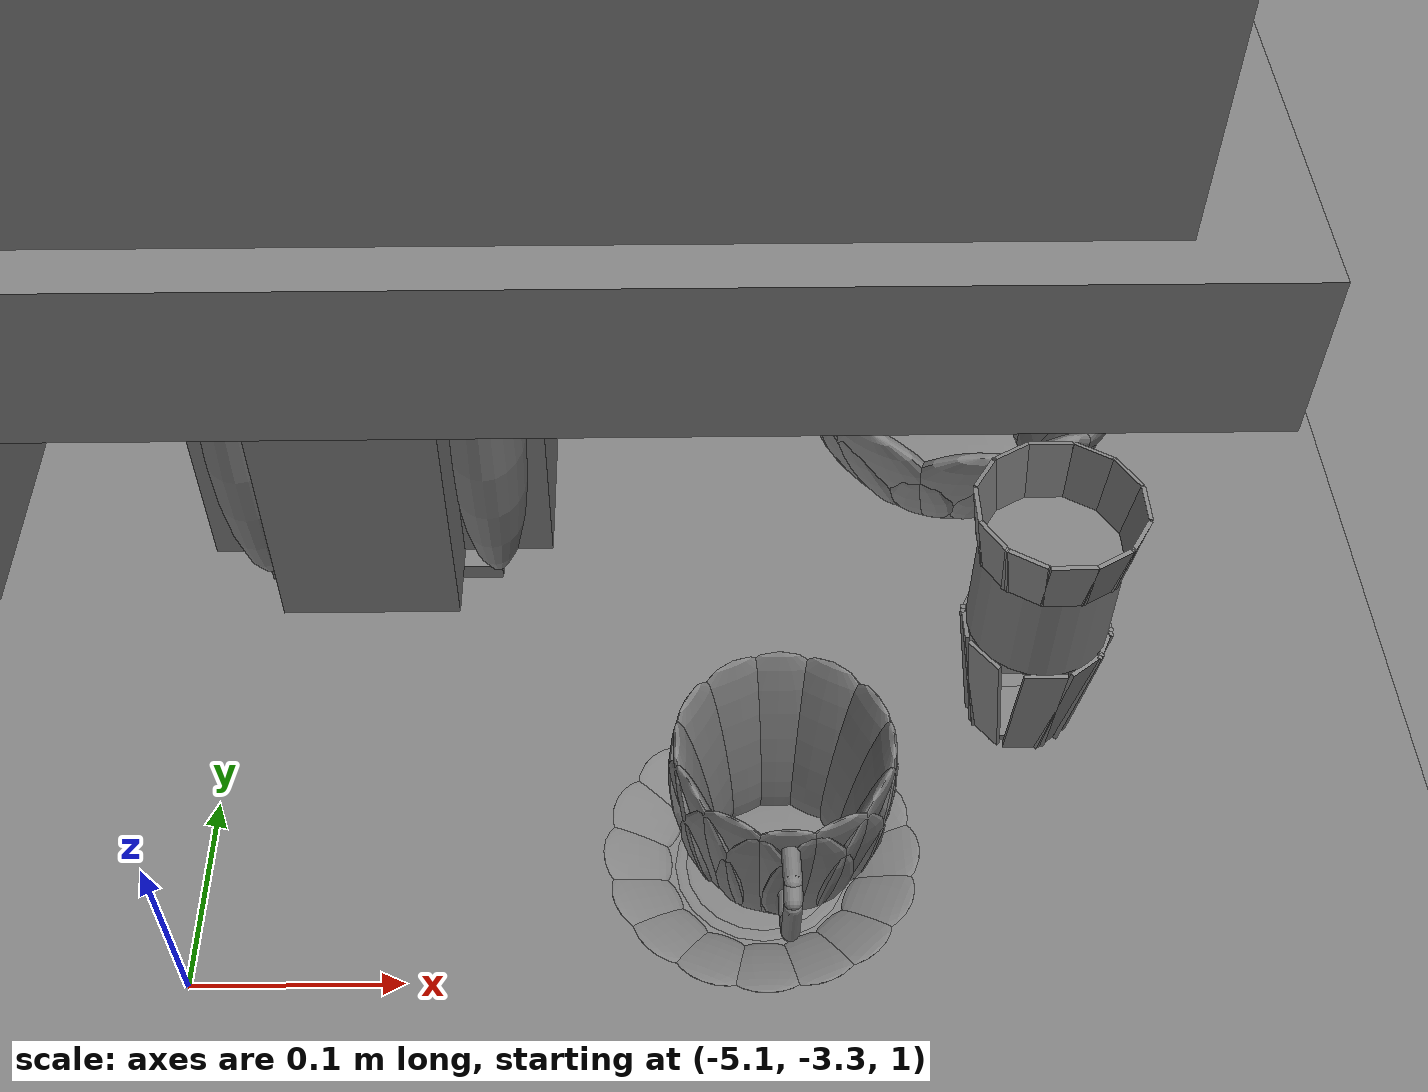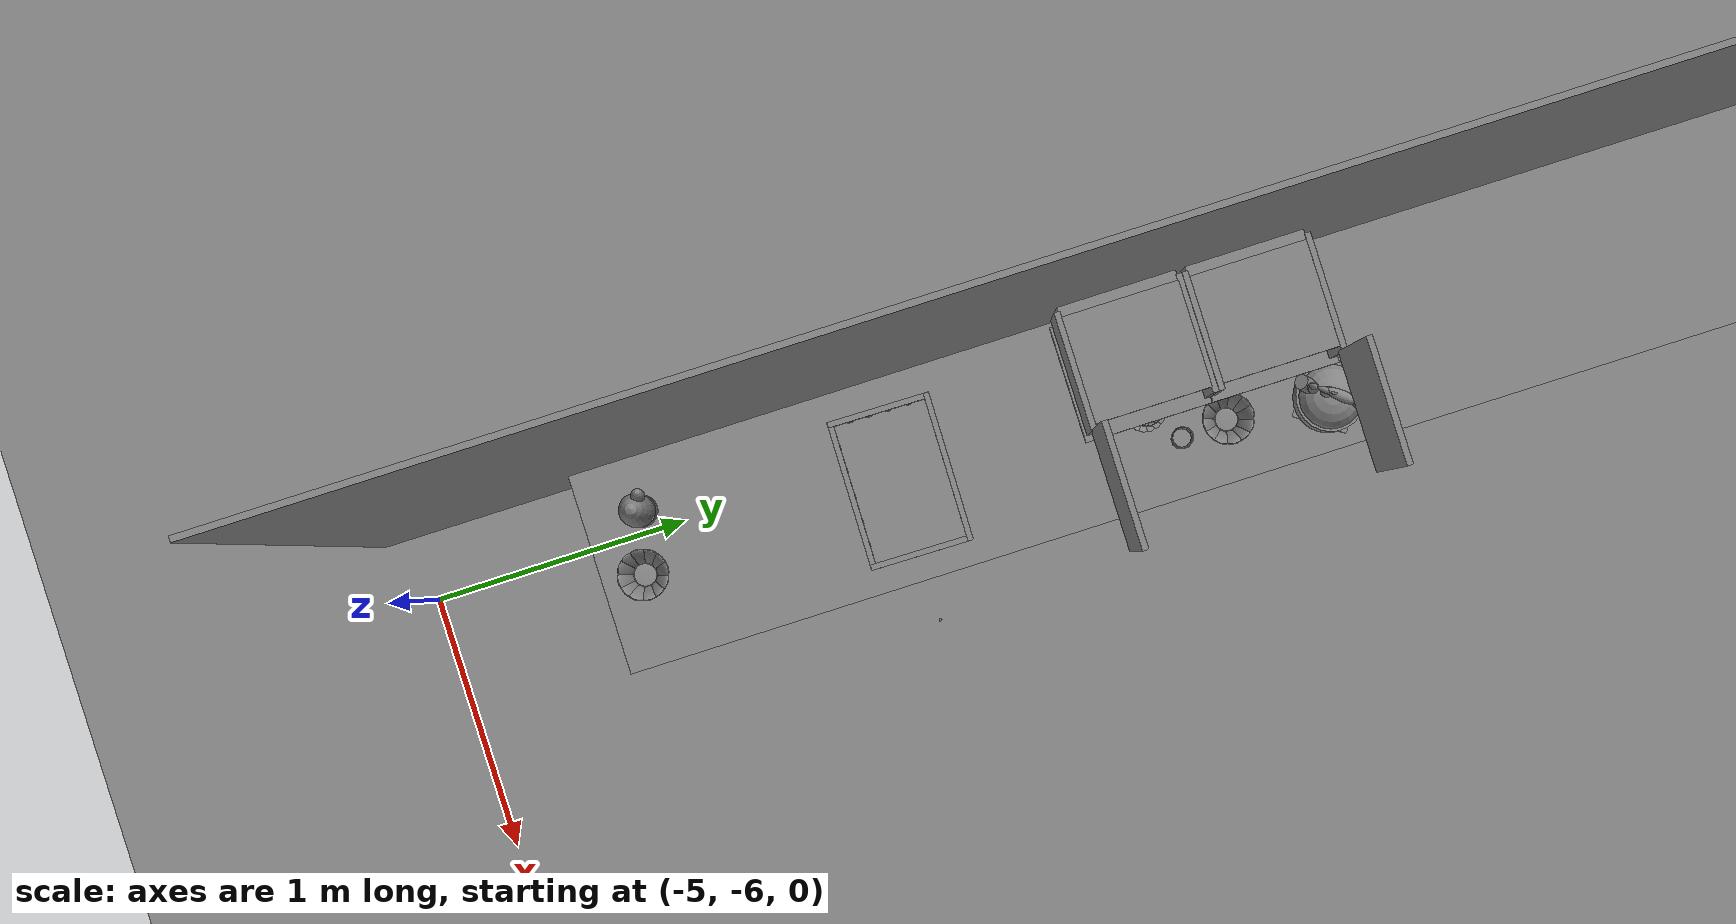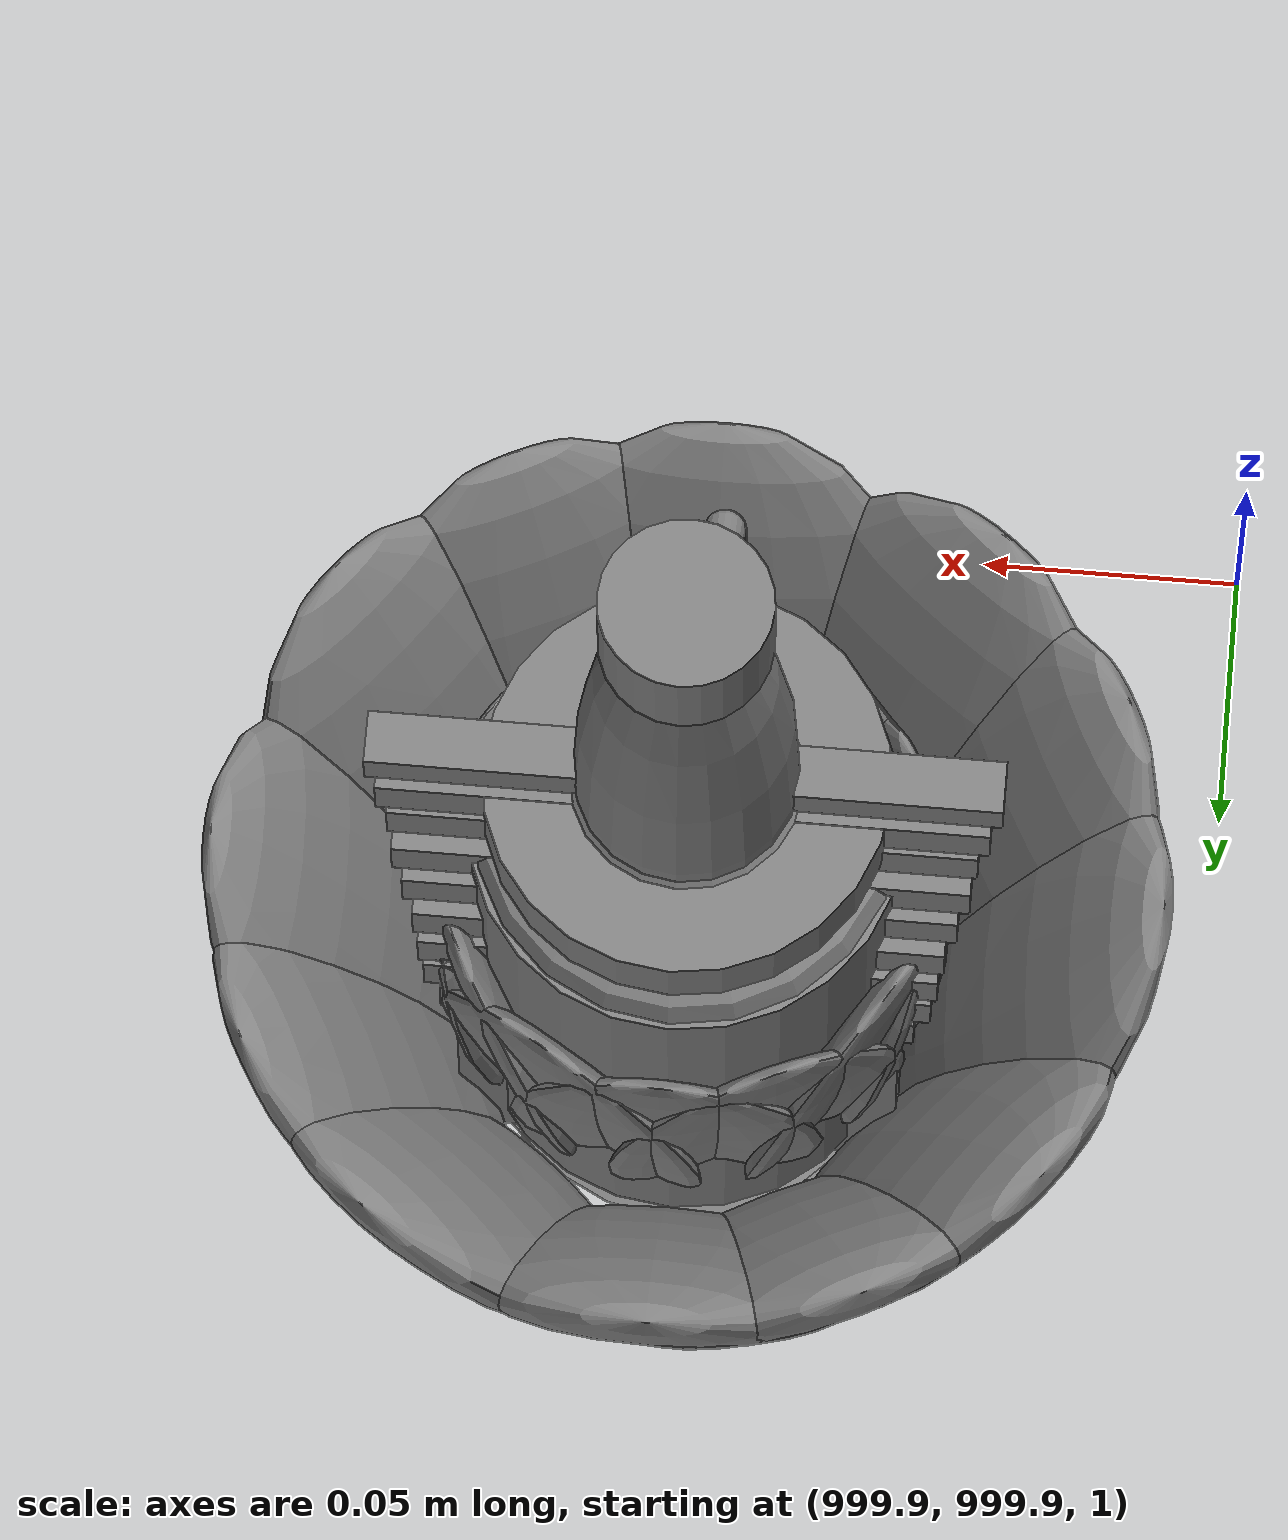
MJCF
<mujoco>
    <option gravity="0.000000000 0.000000000 -9.810000420" timestep="0.0049999999" integrator="implicitfast" density="9.8000002" viscosity="1.8000001e-05" noslip_iterations="10" iterations="100" sdf_iterations="50">
        <flag multiccd="disable"/>
    </option>
    <size memory="1000M"/>
    <compiler coordinate="local"/>
    <worldbody>
        <light cutoff="30" pos="0 1 1" dir="0 -1 -2"/>
        <light cutoff="30" pos="0 -1 1" dir="0 1 -2"/>
        <body pos="-5.046103477 -5.051773071 1.001502514" euler="0.000000000 0.000000000 0.000000000" name="Interactive Objcets_huapen">
            <geom contype="1" conaffinity="1" density="1000" type="ellipsoid" material="" rgba="0.500000000 0.500000000 0.500000000 1.000000000" solimp="0.899999976 0.949999988 0.001000000" friction="1.000000000 0.005000000 0.000100000" solref="0.020000000 1.000000000" margin="0" condim="3" group="0" pos="0.008062840 0.004346371 0.205056787" quat="1.000000000 0.000000000 0.000000000 0.000000000" size="0.059999999 0.059999999 0.180000007" name="Interactive Objcets_huapen_hua_DFE318B9_0E91_48DE_8F3F_F72CDA6A394D"/>
            <geom contype="1" conaffinity="1" density="1000" type="box" material="" rgba="0.500000000 0.500000000 0.500000000 1.000000000" solimp="0.899999976 0.949999988 0.001000000" friction="1.000000000 0.005000000 0.000100000" solref="0.020000000 1.000000000" margin="0" condim="3" group="0" pos="0.008062840 0.003952503 0.020566106" quat="1.000000000 0.000000000 0.000000000 0.000000000" size="0.035000000 0.035000000 0.020000000" name="Interactive Objcets_huapen_hua_9A37343D_4CA3_45E3_88CA_227999F01A8F"/>
            <geom contype="1" conaffinity="1" density="1000" type="cylinder" material="" rgba="0.500000000 0.500000000 0.500000000 1.000000000" solimp="0.899999976 0.949999988 0.001000000" friction="1.000000000 0.005000000 0.000100000" solref="0.020000000 1.000000000" margin="0" condim="3" group="0" pos="0.008062840 0.003952026 0.080107450" quat="1.000000000 0.000000000 0.000000000 0.000000000" size="0.057999998 0.039999999 1.000000000" name="Interactive Objcets_huapen_hua_A86D5F9D_D11B_4CF8_BADC_B543396E2E2A"/>
            <geom contype="1" conaffinity="1" density="1000" type="ellipsoid" material="" rgba="0.500000000 0.500000000 0.500000000 1.000000000" solimp="0.899999976 0.949999988 0.001000000" friction="1.000000000 0.005000000 0.000100000" solref="0.020000000 1.000000000" margin="0" condim="3" group="0" pos="-0.029900074 0.033599377 0.321917295" quat="0.992658079 -0.083605267 -0.087364964 0.002748166" size="0.025000000 0.025000000 0.059999999" name="Interactive Objcets_huapen_hua_89E6E5C7_FDC0_47F9_AB69_C4BC73C2A3AD"/>
            <freejoint name="Interactive Objcets_huapen"/>
        </body>
        <body pos="-4.383717060 -4.440104008 1.730694771" euler="-48.381683350 -34.927688599 82.803428650" mocap="true" name="spotlight2_SpotLight"/>
        <body pos="1000.000000000 1000.000000000 1.000000000" euler="0.000000000 0.000000000 0.000000000" name="openloong_gripper_2f85_fix_base_usda_jar_01">
            <geom contype="1" conaffinity="1" density="1000" type="box" material="" rgba="0.500000000 0.500000000 0.500000000 1.000000000" solimp="0.899999976 0.949999988 0.001000000" friction="1.000000000 0.005000000 0.000100000" solref="0.020000000 1.000000000" margin="0" condim="3" group="0" pos="0.000000000 0.000000000 0.006158113" quat="1.000000000 0.000000000 0.000000000 0.000000000" size="0.020000000 0.020000000 0.005000000" name="openloong_gripper_2f85_fix_base_usda_geom_FC166617_86E5_4D34_893A_3A8603174BBC"/>
            <geom contype="1" conaffinity="1" density="1000" type="cylinder" material="" rgba="0.500000000 0.500000000 0.500000000 1.000000000" solimp="0.899999976 0.949999988 0.001000000" friction="1.000000000 0.005000000 0.000100000" solref="0.020000000 1.000000000" margin="0" condim="3" group="0" pos="0.000000000 0.000000000 0.062744498" quat="1.000000000 0.000000000 0.000000000 0.000000000" size="0.041000001 0.052999999 1.000000000" name="openloong_gripper_2f85_fix_base_usda_geom_90EB766A_EEBA_4BAE_A36F_137AEACE2F26"/>
            <geom contype="1" conaffinity="1" density="1000" type="ellipsoid" material="" rgba="0.500000000 0.500000000 0.500000000 1.000000000" solimp="0.899999976 0.949999988 0.001000000" friction="1.000000000 0.005000000 0.000100000" solref="0.020000000 1.000000000" margin="0" condim="3" group="0" pos="0.000000000 0.000000000 0.122252703" quat="1.000000000 0.000000000 0.000000000 0.000000000" size="0.035999998 0.035999998 0.010000000" name="openloong_gripper_2f85_fix_base_usda_geom_00DAA1B1_965A_44F5_84BE_6EEE1797386B"/>
            <geom contype="1" conaffinity="1" density="1000" type="cylinder" material="" rgba="0.500000000 0.500000000 0.500000000 1.000000000" solimp="0.899999976 0.949999988 0.001000000" friction="1.000000000 0.005000000 0.000100000" solref="0.020000000 1.000000000" margin="0" condim="3" group="0" pos="0.000000000 0.000000000 0.015747190" quat="1.000000000 0.000000000 0.000000000 0.000000000" size="0.035000000 0.010000000 1.000000000" name="openloong_gripper_2f85_fix_base_usda_geom_4789AC8C_1E0C_4157_8B4B_24B801AAC757"/>
            <geom contype="1" conaffinity="1" density="1000" type="ellipsoid" material="" rgba="0.500000000 0.500000000 0.500000000 1.000000000" solimp="0.899999976 0.949999988 0.001000000" friction="1.000000000 0.005000000 0.000100000" solref="0.020000000 1.000000000" margin="0" condim="3" group="0" pos="0.000000000 0.000000000 0.115815401" quat="1.000000000 0.000000000 0.000000000 0.000000000" size="0.039999999 0.039999999 0.010000000" name="openloong_gripper_2f85_fix_base_usda_geom_E6E853BD_446C_429A_9393_838B2DBF6CFB"/>
            <geom contype="1" conaffinity="1" density="1000" type="cylinder" material="" rgba="0.500000000 0.500000000 0.500000000 1.000000000" solimp="0.899999976 0.949999988 0.001000000" friction="1.000000000 0.005000000 0.000100000" solref="0.020000000 1.000000000" margin="0" condim="3" group="0" pos="0.000000000 0.000000000 0.133183479" quat="1.000000000 0.000000000 0.000000000 0.000000000" size="0.037999999 0.006500000 1.000000000" name="openloong_gripper_2f85_fix_base_usda_geom_6B716711_B560_47B6_8EE3_6D37C2154DA9"/>
            <freejoint name="openloong_gripper_2f85_fix_base_usda_jar_01_joint"/>
            <site size="0.005000000 0.005000000 0.005000000" rgba="0.500000000 0.500000000 0.500000000 1.000000000" pos="0.000000000 0.000000000 0.000000000" quat="1.000000000 0.000000000 0.000000000 0.000000000" group="0" type="sphere" name="openloong_gripper_2f85_fix_base_usda_jar_01site"/>
        </body>
        <body pos="1000.000000000 1000.000000000 1.000000000" euler="0.000000000 0.000000000 0.000000000" name="openloong_gripper_2f85_fix_base_usda_bow_yellow_kps">
            <geom contype="1" conaffinity="1" density="1000" type="ellipsoid" material="" rgba="0.500000000 0.500000000 0.500000000 1.000000000" solimp="0.899999976 0.949999988 0.001000000" friction="1.000000000 0.005000000 0.000100000" solref="0.020000000 1.000000000" margin="0" condim="3" group="0" pos="-0.052185059 0.040283203 0.044118762" quat="0.919264615 -0.076883033 -0.225593656 -0.313287765" size="0.010000000 0.039999999 0.052000001" name="openloong_gripper_2f85_fix_base_usda_geom_218553D3_8B46_4213_913C_7CB3C3EDDAB0"/>
            <geom contype="1" conaffinity="1" density="1000" type="ellipsoid" material="" rgba="0.500000000 0.500000000 0.500000000 1.000000000" solimp="0.899999976 0.949999988 0.001000000" friction="1.000000000 0.005000000 0.000100000" solref="0.020000000 1.000000000" margin="0" condim="3" group="0" pos="-0.000061035 0.065979004 0.044118762" quat="0.687598765 -0.168314874 -0.168741167 -0.685860336" size="0.010000000 0.039999999 0.052000001" name="openloong_gripper_2f85_fix_base_usda_geom_9BE76B07_5D87_4C2E_8093_4659BF426FC0"/>
            <geom contype="1" conaffinity="1" density="1000" type="box" material="" rgba="0.500000000 0.500000000 0.500000000 1.000000000" solimp="0.899999976 0.949999988 0.001000000" friction="1.000000000 0.005000000 0.000100000" solref="0.020000000 1.000000000" margin="0" condim="3" group="0" pos="0.000061035 0.000000000 -0.002001643" quat="1.000000000 0.000000000 0.000000000 0.000000000" size="0.029999999 0.029999999 0.002000000" name="openloong_gripper_2f85_fix_base_usda_geom_38516964_FB7B_4271_9678_5770063A381E"/>
            <geom contype="1" conaffinity="1" density="1000" type="ellipsoid" material="" rgba="0.500000000 0.500000000 0.500000000 1.000000000" solimp="0.899999976 0.949999988 0.001000000" friction="1.000000000 0.005000000 0.000100000" solref="0.020000000 1.000000000" margin="0" condim="3" group="0" pos="0.029418945 -0.059082031 0.044118762" quat="0.825555861 0.125530601 0.202597082 -0.511521280" size="0.010000000 0.039999999 0.052000001" name="openloong_gripper_2f85_fix_base_usda_geom_A09855A6_4476_4C52_BEEE_EA84F3C07C96"/>
            <geom contype="1" conaffinity="1" density="1000" type="ellipsoid" material="" rgba="0.500000000 0.500000000 0.500000000 1.000000000" solimp="0.899999976 0.949999988 0.001000000" friction="1.000000000 0.005000000 0.000100000" solref="0.020000000 1.000000000" margin="0" condim="3" group="0" pos="0.000244141 -0.065979004 0.044118762" quat="0.687598765 0.168314651 0.168741375 -0.685860336" size="0.010000000 0.039999999 0.052000001" name="openloong_gripper_2f85_fix_base_usda_geom_8B838EDD_60A2_4448_83B6_861B0D0323D3"/>
            <geom contype="1" conaffinity="1" density="1000" type="ellipsoid" material="" rgba="0.500000000 0.500000000 0.500000000 1.000000000" solimp="0.899999976 0.949999988 0.001000000" friction="1.000000000 0.005000000 0.000100000" solref="0.020000000 1.000000000" margin="0" condim="3" group="0" pos="0.000061035 0.000000000 0.000446677" quat="1.000000000 0.000000000 0.000000000 0.000000000" size="0.039999999 0.039999999 0.002000000" name="openloong_gripper_2f85_fix_base_usda_geom_CA88A8C9_CF0A_48CD_8A2A_801781ECF625"/>
            <geom contype="1" conaffinity="1" density="1000" type="ellipsoid" material="" rgba="0.500000000 0.500000000 0.500000000 1.000000000" solimp="0.899999976 0.949999988 0.001000000" friction="1.000000000 0.005000000 0.000100000" solref="0.020000000 1.000000000" margin="0" condim="3" group="0" pos="0.059082031 0.029541016 0.044118762" quat="0.223252773 -0.231952220 -0.054787423 -0.945174456" size="0.010000000 0.039999999 0.052000001" name="openloong_gripper_2f85_fix_base_usda_geom_F71C78AB_82B6_4157_AC6E_30B61851C46E"/>
            <geom contype="1" conaffinity="1" density="1000" type="ellipsoid" material="" rgba="0.500000000 0.500000000 0.500000000 1.000000000" solimp="0.899999976 0.949999988 0.001000000" friction="1.000000000 0.005000000 0.000100000" solref="0.020000000 1.000000000" margin="0" condim="3" group="0" pos="0.000061035 0.000000000 0.007335305" quat="1.000000000 0.000000000 0.000000000 0.000000000" size="0.039999999 0.039999999 0.002000000" name="openloong_gripper_2f85_fix_base_usda_geom_9D299F10_5A7E_4A43_AF6E_2A01D24BDA21"/>
            <geom contype="1" conaffinity="1" density="1000" type="ellipsoid" material="" rgba="0.500000000 0.500000000 0.500000000 1.000000000" solimp="0.899999976 0.949999988 0.001000000" friction="1.000000000 0.005000000 0.000100000" solref="0.020000000 1.000000000" margin="0" condim="3" group="0" pos="-0.029296875 0.059082031 0.044118762" quat="0.825555861 -0.125530809 -0.202596918 -0.511521280" size="0.010000000 0.039999999 0.052000001" name="openloong_gripper_2f85_fix_base_usda_geom_A0B32E0B_60FA_41DE_8C38_6227602ABC52"/>
            <geom contype="1" conaffinity="1" density="1000" type="ellipsoid" material="" rgba="0.500000000 0.500000000 0.500000000 1.000000000" solimp="0.899999976 0.949999988 0.001000000" friction="1.000000000 0.005000000 0.000100000" solref="0.020000000 1.000000000" margin="0" condim="3" group="0" pos="0.040222168 0.052368164 0.044118762" quat="0.429593176 -0.213750049 -0.105424821 -0.871002972" size="0.010000000 0.039999999 0.052000001" name="openloong_gripper_2f85_fix_base_usda_geom_F28E10AD_E703_4CC7_BAFF_90EDB58A1026"/>
            <geom contype="1" conaffinity="1" density="1000" type="ellipsoid" material="" rgba="0.500000000 0.500000000 0.500000000 1.000000000" solimp="0.899999976 0.949999988 0.001000000" friction="1.000000000 0.005000000 0.000100000" solref="0.020000000 1.000000000" margin="0" condim="3" group="0" pos="0.066040039 0.000000000 0.044118762" quat="0.971183062 -0.000000156 0.238334835 0.000000030" size="0.010000000 0.039999999 0.052000001" name="openloong_gripper_2f85_fix_base_usda_geom_B46CCB0F_C5B7_480A_8C47_FBD8536D3C0F"/>
            <geom contype="1" conaffinity="1" density="1000" type="ellipsoid" material="" rgba="0.500000000 0.500000000 0.500000000 1.000000000" solimp="0.899999976 0.949999988 0.001000000" friction="1.000000000 0.005000000 0.000100000" solref="0.020000000 1.000000000" margin="0" condim="3" group="0" pos="0.052307129 -0.040283203 0.044118762" quat="0.919264674 0.076882750 0.225593731 -0.313287705" size="0.010000000 0.039999999 0.052000001" name="openloong_gripper_2f85_fix_base_usda_geom_FE516CB8_F7B2_4B24_9BD2_BBB56651B5DA"/>
            <geom contype="1" conaffinity="1" density="1000" type="ellipsoid" material="" rgba="0.500000000 0.500000000 0.500000000 1.000000000" solimp="0.899999976 0.949999988 0.001000000" friction="1.000000000 0.005000000 0.000100000" solref="0.020000000 1.000000000" margin="0" condim="3" group="0" pos="-0.065917969 0.000000000 0.044118762" quat="0.971183062 -0.000000142 -0.238334835 0.000000030" size="0.010000000 0.039999999 0.052000001" name="openloong_gripper_2f85_fix_base_usda_geom_D112794D_3670_49A4_BE5C_882E788B973E"/>
            <geom contype="1" conaffinity="1" density="1000" type="ellipsoid" material="" rgba="0.500000000 0.500000000 0.500000000 1.000000000" solimp="0.899999976 0.949999988 0.001000000" friction="1.000000000 0.005000000 0.000100000" solref="0.020000000 1.000000000" margin="0" condim="3" group="0" pos="-0.058898926 -0.029541016 0.044118762" quat="0.223252758 0.231952101 0.054787733 -0.945174575" size="0.010000000 0.039999999 0.052000001" name="openloong_gripper_2f85_fix_base_usda_geom_CE91F223_2D4F_42F9_891F_217F7E73AF4D"/>
            <geom contype="1" conaffinity="1" density="1000" type="ellipsoid" material="" rgba="0.500000000 0.500000000 0.500000000 1.000000000" solimp="0.899999976 0.949999988 0.001000000" friction="1.000000000 0.005000000 0.000100000" solref="0.020000000 1.000000000" margin="0" condim="3" group="0" pos="-0.040100098 -0.052368164 0.044118762" quat="0.429593235 0.213749886 0.105425082 -0.871003032" size="0.010000000 0.039999999 0.052000001" name="openloong_gripper_2f85_fix_base_usda_geom_A4402C30_E68C_4FB6_8132_84BD998C13DD"/>
            <freejoint name="openloong_gripper_2f85_fix_base_usda_bow_yellow_kps_joint"/>
            <site size="0.005000000 0.005000000 0.005000000" rgba="0.500000000 0.500000000 0.500000000 1.000000000" pos="0.000000000 0.000000000 0.000000000" quat="0.999961913 0.008726534 0.000000000 0.000000000" group="0" type="sphere" name="openloong_gripper_2f85_fix_base_usda_bow_yellow_kps"/>
        </body>
        <body pos="1000.000000000 1000.000000000 1.000000000" euler="0.000000000 0.000000000 0.000000000" name="openloong_gripper_2f85_fix_base_usda_coffeecup_white_kps">
            <geom contype="1" conaffinity="1" density="1000" type="capsule" material="" rgba="0.500000000 0.500000000 0.500000000 1.000000000" solimp="0.899999976 0.949999988 0.001000000" friction="1.000000000 0.005000000 0.000100000" solref="0.020000000 1.000000000" margin="0" condim="3" group="0" pos="-0.000854492 -0.065795898 0.050029993" quat="0.343559504 -0.613204718 0.626912475 0.336047262" size="0.004000000 0.005000000 1.000000000" name="openloong_gripper_2f85_fix_base_usda_geom_B093D1FD_1E7E_46D0_B4DD_F7E3F6F81597"/>
            <geom contype="1" conaffinity="1" density="1000" type="ellipsoid" material="" rgba="0.500000000 0.500000000 0.500000000 1.000000000" solimp="0.899999976 0.949999988 0.001000000" friction="1.000000000 0.005000000 0.000100000" solref="0.020000000 1.000000000" margin="0" condim="3" group="0" pos="-0.000793457 -0.038452148 0.048040152" quat="0.711656272 0.066323131 -0.067805752 0.696095467" size="0.005000000 0.029999999 0.048999999" name="openloong_gripper_2f85_fix_base_usda_geom_E623171F_E3E5_445A_87D4_A74DB486E3EB"/>
            <geom contype="1" conaffinity="1" density="1000" type="ellipsoid" material="" rgba="0.500000000 0.500000000 0.500000000 1.000000000" solimp="0.899999976 0.949999988 0.001000000" friction="1.000000000 0.005000000 0.000100000" solref="0.020000000 1.000000000" margin="0" condim="3" group="0" pos="0.037719727 -0.001892090 0.048040152" quat="0.995387912 0.001371633 0.094835162 -0.014391154" size="0.005000000 0.029999999 0.048999999" name="openloong_gripper_2f85_fix_base_usda_geom_E2758BE3_1268_462B_8D04_67D30B65324C"/>
            <geom contype="1" conaffinity="1" density="1000" type="ellipsoid" material="" rgba="0.500000000 0.500000000 0.500000000 1.000000000" solimp="0.899999976 0.949999988 0.001000000" friction="1.000000000 0.005000000 0.000100000" solref="0.020000000 1.000000000" margin="0" condim="3" group="0" pos="0.033996582 0.015502930 0.048040152" quat="0.970659733 -0.021051638 0.092478797 0.220962167" size="0.005000000 0.029999999 0.048999999" name="openloong_gripper_2f85_fix_base_usda_geom_35C484A7_CD2E_4D8C_88DF_2C83DA4B0044"/>
            <geom contype="1" conaffinity="1" density="1000" type="box" material="" rgba="0.500000000 0.500000000 0.500000000 1.000000000" solimp="0.899999976 0.949999988 0.001000000" friction="1.000000000 0.005000000 0.000100000" solref="0.020000000 1.000000000" margin="0" condim="3" group="0" pos="0.000793457 -0.000183105 0.000156164" quat="0.714879215 0.000000000 0.000000000 0.699247897" size="0.020000000 0.020000000 0.002000000" name="openloong_gripper_2f85_fix_base_usda_geom_5F2F033C_50E9_45B8_8F0E_A5AAACCFC65E"/>
            <geom contype="1" conaffinity="1" density="1000" type="ellipsoid" material="" rgba="0.500000000 0.500000000 0.500000000 1.000000000" solimp="0.899999976 0.949999988 0.001000000" friction="1.000000000 0.005000000 0.000100000" solref="0.020000000 1.000000000" margin="0" condim="3" group="0" pos="-0.019409180 -0.033081055 0.048040152" quat="0.866879702 0.046630561 -0.082595348 0.489411235" size="0.005000000 0.029999999 0.048999999" name="openloong_gripper_2f85_fix_base_usda_geom_499A4363_335C_464B_B19F_453CD94C97CC"/>
            <geom contype="1" conaffinity="1" density="1000" type="ellipsoid" material="" rgba="0.500000000 0.500000000 0.500000000 1.000000000" solimp="0.899999976 0.949999988 0.001000000" friction="1.000000000 0.005000000 0.000100000" solref="0.020000000 1.000000000" margin="0" condim="3" group="0" pos="-0.016052246 0.033264160 0.048040152" quat="0.840792537 -0.050782297 -0.080109790 -0.532983541" size="0.005000000 0.029999999 0.048999999" name="openloong_gripper_2f85_fix_base_usda_geom_A5F0B010_0197_4AF5_9A70_5DDC86573346"/>
            <geom contype="1" conaffinity="1" density="1000" type="capsule" material="" rgba="0.500000000 0.500000000 0.500000000 1.000000000" solimp="0.899999976 0.949999988 0.001000000" friction="1.000000000 0.005000000 0.000100000" solref="0.020000000 1.000000000" margin="0" condim="3" group="0" pos="-0.000549316 -0.053527832 0.046825886" quat="0.505496025 -0.494442940 0.505495846 0.494442940" size="0.004000000 0.005000000 1.000000000" name="openloong_gripper_2f85_fix_base_usda_geom_71FDC20B_A504_4EB1_8D30_7F443CBB8717"/>
            <geom contype="1" conaffinity="1" density="1000" type="ellipsoid" material="" rgba="0.500000000 0.500000000 0.500000000 1.000000000" solimp="0.899999976 0.949999988 0.001000000" friction="1.000000000 0.005000000 0.000100000" solref="0.020000000 1.000000000" margin="0" condim="3" group="0" pos="-0.032104492 0.018920898 0.048040152" quat="0.958129764 -0.025742561 -0.091288343 -0.270168930" size="0.005000000 0.029999999 0.048999999" name="openloong_gripper_2f85_fix_base_usda_geom_07EE5B98_6D76_4680_B8F6_CF751D2CFA73"/>
            <geom contype="1" conaffinity="1" density="1000" type="ellipsoid" material="" rgba="0.500000000 0.500000000 0.500000000 1.000000000" solimp="0.899999976 0.949999988 0.001000000" friction="1.000000000 0.005000000 0.000100000" solref="0.020000000 1.000000000" margin="0" condim="3" group="0" pos="-0.037597656 0.000305176 0.048040152" quat="0.995387554 -0.001371440 -0.094839431 -0.014389008" size="0.005000000 0.029999999 0.048999999" name="openloong_gripper_2f85_fix_base_usda_geom_C86C5C23_F619_40F1_88FC_3A636F3BE284"/>
            <geom contype="1" conaffinity="1" density="1000" type="capsule" material="" rgba="0.500000000 0.500000000 0.500000000 1.000000000" solimp="0.899999976 0.949999988 0.001000000" friction="1.000000000 0.005000000 0.000100000" solref="0.020000000 1.000000000" margin="0" condim="3" group="0" pos="-0.000366211 -0.043762207 0.044118762" quat="0.260488123 -0.651174724 0.665731549 0.254792154" size="0.004000000 0.003000000 1.000000000" name="openloong_gripper_2f85_fix_base_usda_geom_EE69CB01_7DBB_460B_AF15_6AEE49980DE5"/>
            <geom contype="1" conaffinity="1" density="1000" type="capsule" material="" rgba="0.500000000 0.500000000 0.500000000 1.000000000" solimp="0.899999976 0.949999988 0.001000000" friction="1.000000000 0.005000000 0.000100000" solref="0.020000000 1.000000000" margin="0" condim="3" group="0" pos="-0.000915527 -0.068542480 0.082936406" quat="0.624995589 -0.339446366 0.347034454 0.611329615" size="0.004000000 0.004000000 1.000000000" name="openloong_gripper_2f85_fix_base_usda_geom_EED8F589_3CB6_4774_A1F1_7446E91CA649"/>
            <geom contype="1" conaffinity="1" density="1000" type="ellipsoid" material="" rgba="0.500000000 0.500000000 0.500000000 1.000000000" solimp="0.899999976 0.949999988 0.001000000" friction="1.000000000 0.005000000 0.000100000" solref="0.020000000 1.000000000" margin="0" condim="3" group="0" pos="0.016113281 -0.034851074 0.048040152" quat="0.840793252 0.050779939 0.080106191 -0.532983422" size="0.005000000 0.029999999 0.048999999" name="openloong_gripper_2f85_fix_base_usda_geom_6C0E8B70_1D4A_4412_BAA9_81ABB5E9B454"/>
            <geom contype="1" conaffinity="1" density="1000" type="ellipsoid" material="" rgba="0.500000000 0.500000000 0.500000000 1.000000000" solimp="0.899999976 0.949999988 0.001000000" friction="1.000000000 0.005000000 0.000100000" solref="0.020000000 1.000000000" margin="0" condim="3" group="0" pos="0.000854492 0.036865234 0.048040152" quat="0.711656570 -0.066320375 0.067802906 0.696095705" size="0.005000000 0.029999999 0.048999999" name="openloong_gripper_2f85_fix_base_usda_geom_F2327686_261A_4782_921C_B24E79F82CD5"/>
            <geom contype="1" conaffinity="1" density="1000" type="ellipsoid" material="" rgba="0.500000000 0.500000000 0.500000000 1.000000000" solimp="0.899999976 0.949999988 0.001000000" friction="1.000000000 0.005000000 0.000100000" solref="0.020000000 1.000000000" margin="0" condim="3" group="0" pos="-0.033935547 -0.017089844 0.048040152" quat="0.970659137 0.021052625 -0.092483103 0.220962465" size="0.005000000 0.029999999 0.048999999" name="openloong_gripper_2f85_fix_base_usda_geom_B9289D00_A3B5_4369_BA89_C23DB03D4ACF"/>
            <geom contype="1" conaffinity="1" density="1000" type="ellipsoid" material="" rgba="0.500000000 0.500000000 0.500000000 1.000000000" solimp="0.899999976 0.949999988 0.001000000" friction="1.000000000 0.005000000 0.000100000" solref="0.020000000 1.000000000" margin="0" condim="3" group="0" pos="0.019531250 0.031494141 0.048040152" quat="0.866880119 -0.046628602 0.082591817 0.489411235" size="0.005000000 0.029999999 0.048999999" name="openloong_gripper_2f85_fix_base_usda_geom_7B909AD4_85D9_43F3_A95C_8149589C46B2"/>
            <geom contype="1" conaffinity="1" density="1000" type="ellipsoid" material="" rgba="0.500000000 0.500000000 0.500000000 1.000000000" solimp="0.899999976 0.949999988 0.001000000" friction="1.000000000 0.005000000 0.000100000" solref="0.020000000 1.000000000" margin="0" condim="3" group="0" pos="0.032165527 -0.020507812 0.048040152" quat="0.958128154 0.025740955 0.091285400 -0.270175666" size="0.005000000 0.029999999 0.048999999" name="openloong_gripper_2f85_fix_base_usda_geom_E801C338_B616_4125_B512_92D3FBF15204"/>
            <geom contype="1" conaffinity="1" density="1000" type="capsule" material="" rgba="0.500000000 0.500000000 0.500000000 1.000000000" solimp="0.899999976 0.949999988 0.001000000" friction="1.000000000 0.005000000 0.000100000" solref="0.020000000 1.000000000" margin="0" condim="3" group="0" pos="-0.000610352 -0.056823730 0.083572865" quat="0.452654332 -0.541215360 0.553313971 0.442756712" size="0.004000000 0.009000000 1.000000000" name="openloong_gripper_2f85_fix_base_usda_geom_5BE1712B_0D04_4AAD_8FE7_7E6E3FA8E685"/>
            <geom contype="1" conaffinity="1" density="1000" type="ellipsoid" material="" rgba="0.500000000 0.500000000 0.500000000 1.000000000" solimp="0.899999976 0.949999988 0.001000000" friction="1.000000000 0.005000000 0.000100000" solref="0.020000000 1.000000000" margin="0" condim="3" group="0" pos="0.000061035 -0.000183105 0.001848221" quat="0.714879215 0.000000000 0.000000000 0.699247897" size="0.029999999 0.029999999 0.001000000" name="openloong_gripper_2f85_fix_base_usda_geom_67206D55_C751_4FC5_A06D_C660B24FC74A"/>
            <geom contype="1" conaffinity="1" density="1000" type="capsule" material="" rgba="0.500000000 0.500000000 0.500000000 1.000000000" solimp="0.899999976 0.949999988 0.001000000" friction="1.000000000 0.005000000 0.000100000" solref="0.020000000 1.000000000" margin="0" condim="3" group="0" pos="-0.000976562 -0.071838379 0.066101432" quat="0.031849027 -0.698553741 0.714169443 0.031152546" size="0.004000000 0.012000000 1.000000000" name="openloong_gripper_2f85_fix_base_usda_geom_C55B132E_A2D9_43B9_99C2_9D41E026A251"/>
            <freejoint name="openloong_gripper_2f85_fix_base_usda_coffeecup_white_kps_joint"/>
            <site size="0.005000000 0.005000000 0.005000000" rgba="0.500000000 0.500000000 0.500000000 1.000000000" pos="0.000000000 0.000000000 0.000000000" quat="0.999961913 0.008726534 0.000000000 0.000000000" group="0" type="sphere" name="openloong_gripper_2f85_fix_base_usda_coffeecup_white_kps"/>
        </body>
        <body pos="1000.000000000 1000.000000000 1.000000000" euler="0.000000000 0.000000000 0.000000000" name="openloong_gripper_2f85_fix_base_usda_salt">
            <geom contype="1" conaffinity="1" density="1000" type="box" material="" rgba="0.500000000 0.500000000 0.500000000 1.000000000" solimp="0.899999976 0.949999988 0.001000000" friction="1.000000000 0.005000000 0.000100000" solref="0.020000000 1.000000000" margin="0" condim="3" group="0" pos="0.000305176 0.000000000 0.084862232" quat="1.000000000 0.000000000 0.000000000 0.000000000" size="0.048999999 0.018999999 0.005000000" name="openloong_gripper_2f85_fix_base_usda_geom_F505A07C_028D_4F99_A269_7ED051781F40"/>
            <geom contype="1" conaffinity="1" density="1000" type="box" material="" rgba="0.500000000 0.500000000 0.500000000 1.000000000" solimp="0.899999976 0.949999988 0.001000000" friction="1.000000000 0.005000000 0.000100000" solref="0.020000000 1.000000000" margin="0" condim="3" group="0" pos="0.000305176 0.000000000 0.104564309" quat="1.000000000 0.000000000 0.000000000 0.000000000" size="0.052000001 0.014000000 0.005000000" name="openloong_gripper_2f85_fix_base_usda_geom_4C3C3CDC_99AE_48EA_ACE8_03016993E534"/>
            <geom contype="1" conaffinity="1" density="1000" type="box" material="" rgba="0.500000000 0.500000000 0.500000000 1.000000000" solimp="0.899999976 0.949999988 0.001000000" friction="1.000000000 0.005000000 0.000100000" solref="0.020000000 1.000000000" margin="0" condim="3" group="0" pos="0.000305176 0.000000000 0.114487171" quat="1.000000000 0.000000000 0.000000000 0.000000000" size="0.054000001 0.011500000 0.005000000" name="openloong_gripper_2f85_fix_base_usda_geom_AA6A1E63_2D73_4211_9444_602F348CF11C"/>
            <geom contype="1" conaffinity="1" density="1000" type="box" material="" rgba="0.500000000 0.500000000 0.500000000 1.000000000" solimp="0.899999976 0.949999988 0.001000000" friction="1.000000000 0.005000000 0.000100000" solref="0.020000000 1.000000000" margin="0" condim="3" group="0" pos="0.000305176 0.000000000 0.075103164" quat="1.000000000 0.000000000 0.000000000 0.000000000" size="0.048000000 0.020000000 0.005000000" name="openloong_gripper_2f85_fix_base_usda_geom_96943878_6EF5_4878_9C88_B69F20DCA540"/>
            <geom contype="1" conaffinity="1" density="1000" type="box" material="" rgba="0.500000000 0.500000000 0.500000000 1.000000000" solimp="0.899999976 0.949999988 0.001000000" friction="1.000000000 0.005000000 0.000100000" solref="0.020000000 1.000000000" margin="0" condim="3" group="0" pos="0.000305176 0.000000000 0.134892464" quat="1.000000000 0.000000000 0.000000000 0.000000000" size="0.057000000 0.007000000 0.005000000" name="openloong_gripper_2f85_fix_base_usda_geom_392FC09A_309D_43F3_89A4_414A8277BEB1"/>
            <geom contype="1" conaffinity="1" density="1000" type="box" material="" rgba="0.500000000 0.500000000 0.500000000 1.000000000" solimp="0.899999976 0.949999988 0.001000000" friction="1.000000000 0.005000000 0.000100000" solref="0.020000000 1.000000000" margin="0" condim="3" group="0" pos="0.000305176 0.000000000 0.094920278" quat="1.000000000 0.000000000 0.000000000 0.000000000" size="0.050000001 0.017000001 0.005000000" name="openloong_gripper_2f85_fix_base_usda_geom_652BF1E0_A3C0_4C59_BB0F_F7320C24A429"/>
            <geom contype="1" conaffinity="1" density="1000" type="box" material="" rgba="0.500000000 0.500000000 0.500000000 1.000000000" solimp="0.899999976 0.949999988 0.001000000" friction="1.000000000 0.005000000 0.000100000" solref="0.020000000 1.000000000" margin="0" condim="3" group="0" pos="0.000305176 0.000000000 0.065204859" quat="1.000000000 0.000000000 0.000000000 0.000000000" size="0.045000002 0.021000000 0.005000000" name="openloong_gripper_2f85_fix_base_usda_geom_C9FA93CE_3555_47AA_B2DC_346A780B1EE0"/>
            <geom contype="1" conaffinity="1" density="1000" type="box" material="" rgba="0.500000000 0.500000000 0.500000000 1.000000000" solimp="0.899999976 0.949999988 0.001000000" friction="1.000000000 0.005000000 0.000100000" solref="0.020000000 1.000000000" margin="0" condim="3" group="0" pos="0.000305176 0.000000000 0.144135714" quat="1.000000000 0.000000000 0.000000000 0.000000000" size="0.059000000 0.005000000 0.004000000" name="openloong_gripper_2f85_fix_base_usda_geom_E080DC15_ECB0_432B_9A33_116E4E6117A3"/>
            <geom contype="1" conaffinity="1" density="1000" type="box" material="" rgba="0.500000000 0.500000000 0.500000000 1.000000000" solimp="0.899999976 0.949999988 0.001000000" friction="1.000000000 0.005000000 0.000100000" solref="0.020000000 1.000000000" margin="0" condim="3" group="0" pos="0.000000000 0.000000000 0.031593561" quat="1.000000000 0.000000000 0.000000000 0.000000000" size="0.041999999 0.024000000 0.029999999" name="openloong_gripper_2f85_fix_base_usda_geom_82D4B38A_29B2_429E_B061_06735FBC5E3D"/>
            <geom contype="1" conaffinity="1" density="1000" type="box" material="" rgba="0.500000000 0.500000000 0.500000000 1.000000000" solimp="0.899999976 0.949999988 0.001000000" friction="1.000000000 0.005000000 0.000100000" solref="0.020000000 1.000000000" margin="0" condim="3" group="0" pos="0.000305176 0.000000000 0.124608755" quat="1.000000000 0.000000000 0.000000000 0.000000000" size="0.055000000 0.008000000 0.005000000" name="openloong_gripper_2f85_fix_base_usda_geom_00A5D669_E7BB_4801_9A99_7D184BF2EFE9"/>
            <freejoint name="openloong_gripper_2f85_fix_base_usda_salt_joint"/>
            <site size="0.005000000 0.005000000 0.005000000" rgba="0.500000000 0.500000000 0.500000000 1.000000000" pos="0.000000000 0.000000000 0.000000000" quat="1.000000000 0.000000000 0.000000000 0.000000000" group="0" type="sphere" name="openloong_gripper_2f85_fix_base_usda_saltsite"/>
        </body>
        <body pos="1000.000000000 1000.000000000 1.000000000" euler="0.000000000 0.000000000 0.000000000" name="openloong_gripper_2f85_fix_base_usda_bottle_red">
            <geom contype="1" conaffinity="1" density="1000" type="ellipsoid" material="" rgba="0.500000000 0.500000000 0.500000000 1.000000000" solimp="0.899999976 0.949999988 0.001000000" friction="1.000000000 0.005000000 0.000100000" solref="0.020000000 1.000000000" margin="0" condim="3" group="0" pos="0.000000000 0.000000000 0.144284487" quat="1.000000000 0.000000000 0.000000000 0.000000000" size="0.021000000 0.021000000 0.079999998" name="openloong_gripper_2f85_fix_base_usda_geom_3893F1AB_5288_4531_836A_4B3D8C11F5FC"/>
            <geom contype="1" conaffinity="1" density="1000" type="cylinder" material="" rgba="0.500000000 0.500000000 0.500000000 1.000000000" solimp="0.899999976 0.949999988 0.001000000" friction="1.000000000 0.005000000 0.000100000" solref="0.020000000 1.000000000" margin="0" condim="3" group="0" pos="0.000000000 0.000000000 0.220618963" quat="1.000000000 0.000000000 0.000000000 0.000000000" size="0.016000001 0.010000000 1.000000000" name="openloong_gripper_2f85_fix_base_usda_geom_03A3405F_43EF_442A_ACD6_5DB4C6404C86"/>
            <geom contype="1" conaffinity="1" density="1000" type="ellipsoid" material="" rgba="0.500000000 0.500000000 0.500000000 1.000000000" solimp="0.899999976 0.949999988 0.001000000" friction="1.000000000 0.005000000 0.000100000" solref="0.020000000 1.000000000" margin="0" condim="3" group="0" pos="0.000000000 0.000000000 0.118945479" quat="1.000000000 0.000000000 0.000000000 0.000000000" size="0.030999999 0.030999999 0.029999999" name="openloong_gripper_2f85_fix_base_usda_geom_39F0606F_8F70_41E5_A72E_9C6E63123C7E"/>
            <geom contype="1" conaffinity="1" density="1000" type="box" material="" rgba="0.500000000 0.500000000 0.500000000 1.000000000" solimp="0.899999976 0.949999988 0.001000000" friction="1.000000000 0.005000000 0.000100000" solref="0.020000000 1.000000000" margin="0" condim="3" group="0" pos="0.000000000 0.000000000 0.002189159" quat="1.000000000 0.000000000 0.000000000 0.000000000" size="0.020000000 0.020000000 0.003000000" name="openloong_gripper_2f85_fix_base_usda_geom_58BC5F5D_BBE4_467C_9B51_FA9DCEF2B3E1"/>
            <geom contype="1" conaffinity="1" density="1000" type="cylinder" material="" rgba="0.500000000 0.500000000 0.500000000 1.000000000" solimp="0.899999976 0.949999988 0.001000000" friction="1.000000000 0.005000000 0.000100000" solref="0.020000000 1.000000000" margin="0" condim="3" group="0" pos="0.000000000 -0.000366211 0.060884237" quat="1.000000000 0.000000000 0.000000000 0.000000000" size="0.030999999 0.057999998 1.000000000" name="openloong_gripper_2f85_fix_base_usda_geom_9095B079_6AC6_4439_A66B_EAD401CE4356"/>
            <freejoint name="openloong_gripper_2f85_fix_base_usda_bottle_red_joint"/>
            <site size="0.005000000 0.005000000 0.005000000" rgba="0.500000000 0.500000000 0.500000000 1.000000000" pos="0.000000000 0.000000000 0.000000000" quat="0.999961913 0.008726535 0.000000000 0.000000000" group="0" type="sphere" name="openloong_gripper_2f85_fix_base_usda_bottle_redsite"/>
        </body>
        <body pos="-4.443062782 -4.056121826 1.906381249" euler="-72.064880371 -10.025133133 99.981704712" mocap="true" name="spotlight6_SpotLight"/>
        <body pos="-4.480019093 -4.384319305 1.914078116" euler="-93.568916321 -41.566860199 -33.404781342" mocap="true" name="spotlight1_SpotLight"/>
        <body pos="0.000000000 0.000000000 0.000000000" euler="0.000000000 0.000000000 0.000000000" name="Static Objcets_Static Objcets">
            <geom contype="1" conaffinity="1" density="1000" type="box" material="" rgba="0.500000000 0.500000000 0.500000000 1.000000000" solimp="0.899999976 0.949999988 0.001000000" friction="1.000000000 0.005000000 0.000100000" solref="0.020000000 1.000000000" margin="0" condim="3" group="0" pos="-4.999745846 -3.087441683 1.763863802" quat="0.707107067 0.707106471 0.000000000 0.000000000" size="0.200000003 0.159999996 0.010000000" name="Static Objcets_geom_1EED0F31_5242_44E9_B9FC_2571C5BC768C"/>
            <geom contype="1" conaffinity="1" density="1000" type="box" material="" rgba="0.500000000 0.500000000 0.500000000 1.000000000" solimp="0.899999976 0.949999988 0.001000000" friction="1.000000000 0.005000000 0.000100000" solref="0.020000000 1.000000000" margin="0" condim="3" group="0" pos="-5.189302921 -3.293644905 1.760152459" quat="0.707107067 0.707106471 0.000000000 0.000000000" size="0.025000000 0.159999996 0.200000003" name="Static Objcets_geom_2C899DFA_91B5_46CB_908F_39AD0296F336"/>
            <geom contype="1" conaffinity="1" density="1000" type="box" material="" rgba="0.500000000 0.500000000 0.500000000 1.000000000" solimp="0.899999976 0.949999988 0.001000000" friction="1.000000000 0.005000000 0.000100000" solref="0.020000000 1.000000000" margin="0" condim="3" group="0" pos="-4.979488373 -3.297635794 1.591412544" quat="0.707106829 0.707106709 0.000000000 0.000000000" size="0.200000003 0.015000000 0.219999999" name="Static Objcets_geom_758D78F2_39F9_44F8_9BD8_F7A0251D4A44"/>
            <geom contype="1" conaffinity="1" density="1000" type="box" material="" rgba="0.500000000 0.500000000 0.500000000 1.000000000" solimp="0.899999976 0.949999988 0.001000000" friction="1.000000000 0.005000000 0.000100000" solref="0.020000000 1.000000000" margin="0" condim="3" group="0" pos="-4.999745846 -3.497932911 1.764780521" quat="0.707107067 0.707106471 0.000000000 0.000000000" size="0.200000003 0.159999996 0.010000000" name="Static Objcets_geom_82CE4075_1BB7_4E67_92A1_62B29F6C2387"/>
            <geom contype="1" conaffinity="1" density="1000" type="box" material="" rgba="0.500000000 0.500000000 0.500000000 1.000000000" solimp="0.899999976 0.949999988 0.001000000" friction="1.000000000 0.005000000 0.000100000" solref="0.020000000 1.000000000" margin="0" condim="3" group="0" pos="-5.000125408 -3.294431210 1.913951039" quat="0.707107067 0.707106471 0.000000000 0.000000000" size="0.180000007 0.010000000 0.200000003" name="Static Objcets_geom_23D05BE7_7807_4EAD_BD49_05F62A578B0C"/>
            <geom contype="1" conaffinity="1" density="1000" type="box" material="" rgba="0.500000000 0.500000000 0.500000000 1.000000000" solimp="0.899999976 0.949999988 0.001000000" friction="1.000000000 0.005000000 0.000100000" solref="0.020000000 1.000000000" margin="0" condim="3" group="0" pos="-4.999745846 -3.066934109 1.765979409" quat="0.707107067 0.707106471 0.000000000 0.000000000" size="0.200000003 0.159999996 0.010000000" name="Static Objcets_geom_6ECB6B62_84B1_4D98_ACBD_18833C798978"/>
            <geom contype="1" conaffinity="1" density="1000" type="box" material="" rgba="0.500000000 0.500000000 0.500000000 1.000000000" solimp="0.899999976 0.949999988 0.001000000" friction="1.000000000 0.005000000 0.000100000" solref="0.020000000 1.000000000" margin="0" condim="3" group="0" pos="-5.189302921 -2.861564636 1.760152102" quat="0.707107067 0.707106471 0.000000000 0.000000000" size="0.025000000 0.159999996 0.200000003" name="Static Objcets_geom_C9075748_8C4B_48D5_9E5B_2AC78F565013"/>
            <geom contype="1" conaffinity="1" density="1000" type="box" material="" rgba="0.500000000 0.500000000 0.500000000 1.000000000" solimp="0.899999976 0.949999988 0.001000000" friction="1.000000000 0.005000000 0.000100000" solref="0.020000000 1.000000000" margin="0" condim="3" group="0" pos="-5.000125408 -2.861802340 1.913950682" quat="0.707107067 0.707106471 0.000000000 0.000000000" size="0.180000007 0.010000000 0.200000003" name="Static Objcets_geom_701F4177_C050_437D_A919_DDA9D055AE14"/>
            <geom contype="1" conaffinity="1" density="1000" type="box" material="" rgba="0.500000000 0.500000000 0.500000000 1.000000000" solimp="0.899999976 0.949999988 0.001000000" friction="1.000000000 0.005000000 0.000100000" solref="0.020000000 1.000000000" margin="0" condim="3" group="0" pos="-4.979488373 -2.855390549 1.591412187" quat="0.707106709 0.707106769 0.000000000 0.000000000" size="0.200000003 0.015000000 0.219999999" name="Static Objcets_geom_D59C72A1_0A00_4376_94CF_30FB78112471"/>
            <geom contype="1" conaffinity="1" density="1000" type="box" material="" rgba="0.500000000 0.500000000 0.500000000 1.000000000" solimp="0.899999976 0.949999988 0.001000000" friction="1.000000000 0.005000000 0.000100000" solref="0.020000000 1.000000000" margin="0" condim="3" group="0" pos="-4.999745846 -2.653569937 1.764779806" quat="0.707107067 0.707106471 0.000000000 0.000000000" size="0.200000003 0.159999996 0.010000000" name="Static Objcets_geom_5776C5A5_6BD6_4FA4_B172_FEFE293B5326"/>
            <geom contype="1" conaffinity="1" density="1000" type="box" material="" rgba="0.500000000 0.500000000 0.500000000 1.000000000" solimp="0.899999976 0.949999988 0.001000000" friction="1.000000000 0.005000000 0.000100000" solref="0.020000000 1.000000000" margin="0" condim="3" group="0" pos="-0.720102787 0.222944975 -1.102830648" quat="0.000000954 1.000000000 0.000000000 0.000000000" size="8.000000000 8.000000000 0.010000000" name="Static Objcets_geom_377E2EAA_F1A4_4892_AD57_2672DB4F91AF"/>
            <geom contype="1" conaffinity="1" density="1000" type="box" material="" rgba="0.500000000 0.500000000 0.500000000 1.000000000" solimp="0.899999976 0.949999988 0.001000000" friction="1.000000000 0.005000000 0.000100000" solref="0.020000000 1.000000000" margin="0" condim="3" group="0" pos="-4.873187065 -2.461376429 0.977675021" quat="0.707107067 0.707106471 0.000000000 0.000000000" size="0.370000005 0.029999999 2.799999952" name="Static Objcets_geom_38B5EC2E_AA86_40C8_A15C_28500689C37C"/>
            <geom contype="1" conaffinity="1" density="1000" type="box" material="" rgba="0.500000000 0.500000000 0.500000000 1.000000000" solimp="0.899999976 0.949999988 0.001000000" friction="1.000000000 0.005000000 0.000100000" solref="0.020000000 1.000000000" margin="0" condim="3" group="0" pos="-5.244853973 -2.375543594 1.820221663" quat="0.707107008 0.707106531 0.000000000 0.000000000" size="0.010000000 1.500000000 3.700000048" name="Static Objcets_geom_DC47FF1B_0B67_491C_B884_9C78B0938B42"/>
        </body>
        <body pos="-4.827295780 -3.287638187 1.074643731" euler="0.000000000 0.000000000 89.999992371" name="Interactive Objcets_coffeecup_01">
            <geom contype="1" conaffinity="1" density="1000" type="ellipsoid" material="" rgba="0.500000000 0.500000000 0.500000000 1.000000000" solimp="0.899999976 0.949999988 0.001000000" friction="1.000000000 0.005000000 0.000100000" solref="0.020000000 1.000000000" margin="0" condim="3" group="0" pos="0.068445444 0.017385960 0.002976775" quat="0.228377223 -0.092319682 -0.021759447 -0.968941331" size="0.005000000 0.029999999 0.048999999" name="Interactive Objcets_geom_249C8D87_13C0_4D20_8AB4_98CACBDC4332"/>
            <geom contype="1" conaffinity="1" density="1000" type="capsule" material="" rgba="0.500000000 0.500000000 0.500000000 1.000000000" solimp="0.899999976 0.949999988 0.001000000" friction="1.000000000 0.005000000 0.000100000" solref="0.020000000 1.000000000" margin="0" condim="3" group="0" pos="-0.008219719 0.000000000 -0.000944734" quat="0.364379913 0.000000063 0.931250274 -0.000000063" size="0.004000000 0.003000000 1.000000000" name="Interactive Objcets_geom_0B4B5956_567B_48AB_8C65_0A671471B618"/>
            <geom contype="1" conaffinity="1" density="1000" type="ellipsoid" material="" rgba="0.500000000 0.500000000 0.500000000 1.000000000" solimp="0.899999976 0.949999988 0.001000000" friction="1.000000000 0.005000000 0.000100000" solref="0.020000000 1.000000000" margin="0" condim="3" group="0" pos="0.001010895 -0.016271591 0.002976775" quat="0.228377163 0.092315644 0.021758538 -0.968941689" size="0.005000000 0.029999999 0.048999999" name="Interactive Objcets_geom_67C6B4BD_ADCE_4372_B7C4_85221456FE5E"/>
            <geom contype="1" conaffinity="1" density="1000" type="ellipsoid" material="" rgba="0.500000000 0.500000000 0.500000000 1.000000000" solimp="0.899999976 0.949999988 0.001000000" friction="1.000000000 0.005000000 0.000100000" solref="0.020000000 1.000000000" margin="0" condim="3" group="0" pos="0.034471050 -0.037125111 0.002976775" quat="0.701517045 0.067293778 0.066836871 -0.706313014" size="0.005000000 0.029999999 0.048999999" name="Interactive Objcets_geom_39452C15_AE50_45BF_A601_939AF150C44E"/>
            <geom contype="1" conaffinity="1" density="1000" type="ellipsoid" material="" rgba="0.500000000 0.500000000 0.500000000 1.000000000" solimp="0.899999976 0.949999988 0.001000000" friction="1.000000000 0.005000000 0.000100000" solref="0.020000000 1.000000000" margin="0" condim="3" group="0" pos="0.035336256 0.000558376 -0.045152068" quat="0.999999881 0.000000000 0.000000000 0.000000000" size="0.029999999 0.029999999 0.001000000" name="Interactive Objcets_geom_E2D08F0B_350C_4800_8AFF_0B05C610B4AF"/>
            <geom contype="1" conaffinity="1" density="1000" type="capsule" material="" rgba="0.500000000 0.500000000 0.500000000 1.000000000" solimp="0.899999976 0.949999988 0.001000000" friction="1.000000000 0.005000000 0.000100000" solref="0.020000000 1.000000000" margin="0" condim="3" group="0" pos="-0.033022881 0.000000000 0.037873149" quat="0.874267220 0.000000042 0.485444903 -0.000000084" size="0.004000000 0.004000000 1.000000000" name="Interactive Objcets_geom_F5972254_F15D_4D5D_AEA8_0E127940465E"/>
            <geom contype="1" conaffinity="1" density="1000" type="capsule" material="" rgba="0.500000000 0.500000000 0.500000000 1.000000000" solimp="0.899999976 0.949999988 0.001000000" friction="1.000000000 0.005000000 0.000100000" solref="0.020000000 1.000000000" margin="0" condim="3" group="0" pos="-0.018014431 0.000000000 0.001762271" quat="0.707106769 -0.000000004 0.707106709 -0.000000088" size="0.004000000 0.005000000 1.000000000" name="Interactive Objcets_geom_ADF6DAD2_9819_4EEA_AA8C_193B25C48DC6"/>
            <geom contype="1" conaffinity="1" density="1000" type="capsule" material="" rgba="0.500000000 0.500000000 0.500000000 1.000000000" solimp="0.899999976 0.949999988 0.001000000" friction="1.000000000 0.005000000 0.000100000" solref="0.020000000 1.000000000" margin="0" condim="3" group="0" pos="-0.021276474 0.000000000 0.038509369" quat="0.633189917 0.000000000 0.773996413 0.000000000" size="0.004000000 0.009000000 1.000000000" name="Interactive Objcets_geom_C8E85790_ECF4_4DC6_92E7_5655B37CB307"/>
            <geom contype="1" conaffinity="1" density="1000" type="ellipsoid" material="" rgba="0.500000000 0.500000000 0.500000000 1.000000000" solimp="0.899999976 0.949999988 0.001000000" friction="1.000000000 0.005000000 0.000100000" solref="0.020000000 1.000000000" margin="0" condim="3" group="0" pos="0.002039194 0.019308567 0.002976775" quat="0.961933970 -0.024419386 -0.091652036 -0.256293654" size="0.005000000 0.029999999 0.048999999" name="Interactive Objcets_geom_E737ECE8_3D30_4383_B438_158AF09E590E"/>
            <geom contype="1" conaffinity="1" density="1000" type="ellipsoid" material="" rgba="0.500000000 0.500000000 0.500000000 1.000000000" solimp="0.899999976 0.949999988 0.001000000" friction="1.000000000 0.005000000 0.000100000" solref="0.020000000 1.000000000" margin="0" condim="3" group="0" pos="0.034984604 0.038240910 0.002976775" quat="0.701516926 -0.067296736 -0.066839755 -0.706312656" size="0.005000000 0.029999999 0.048999999" name="Interactive Objcets_geom_0F9CF92E_B40F_4FC2_AED4_B3F0DD5D58DC"/>
            <geom contype="1" conaffinity="1" density="1000" type="ellipsoid" material="" rgba="0.500000000 0.500000000 0.500000000 1.000000000" solimp="0.899999976 0.949999988 0.001000000" friction="1.000000000 0.005000000 0.000100000" solref="0.020000000 1.000000000" margin="0" condim="3" group="0" pos="-0.002956629 0.000558376 0.002976775" quat="0.995491505 0.000000004 -0.094849378 -0.000000089" size="0.005000000 0.029999999 0.048999999" name="Interactive Objcets_geom_64243AD3_596E_4FBD_B2F2_0415F3D220E5"/>
            <geom contype="1" conaffinity="1" density="1000" type="ellipsoid" material="" rgba="0.500000000 0.500000000 0.500000000 1.000000000" solimp="0.899999976 0.949999988 0.001000000" friction="1.000000000 0.005000000 0.000100000" solref="0.020000000 1.000000000" margin="0" condim="3" group="0" pos="0.067416430 -0.018191338 0.002976775" quat="0.961934388 0.024418317 0.091648072 -0.256293803" size="0.005000000 0.029999999 0.048999999" name="Interactive Objcets_geom_05199748_B9FE_4EBD_A53F_EA3886FA16F9"/>
            <geom contype="1" conaffinity="1" density="1000" type="ellipsoid" material="" rgba="0.500000000 0.500000000 0.500000000 1.000000000" solimp="0.899999976 0.949999988 0.001000000" friction="1.000000000 0.005000000 0.000100000" solref="0.020000000 1.000000000" margin="0" condim="3" group="0" pos="0.051787138 -0.033043861 0.002976775" quat="0.848411202 0.049616337 0.080832161 -0.520771146" size="0.005000000 0.029999999 0.048999999" name="Interactive Objcets_geom_B0EA7033_09D5_45BC_ACCB_80C7E8F31804"/>
            <geom contype="1" conaffinity="1" density="1000" type="ellipsoid" material="" rgba="0.500000000 0.500000000 0.500000000 1.000000000" solimp="0.899999976 0.949999988 0.001000000" friction="1.000000000 0.005000000 0.000100000" solref="0.020000000 1.000000000" margin="0" condim="3" group="0" pos="0.017669693 0.034160614 0.002976775" quat="0.848410904 -0.049618516 -0.080835648 -0.520770907" size="0.005000000 0.029999999 0.048999999" name="Interactive Objcets_geom_07695541_F8B4_4DB8_9175_34B24AA2A491"/>
            <geom contype="1" conaffinity="1" density="1000" type="capsule" material="" rgba="0.500000000 0.500000000 0.500000000 1.000000000" solimp="0.899999976 0.949999988 0.001000000" friction="1.000000000 0.005000000 0.000100000" solref="0.020000000 1.000000000" margin="0" condim="3" group="0" pos="-0.030251026 0.000000000 0.004966617" quat="0.480583906 -0.000000000 0.876948774 -0.000000126" size="0.004000000 0.005000000 1.000000000" name="Interactive Objcets_geom_0FABAA40_15C4_428F_B2DD_712B6B5463B6"/>
            <geom contype="1" conaffinity="1" density="1000" type="capsule" material="" rgba="0.500000000 0.500000000 0.500000000 1.000000000" solimp="0.899999976 0.949999988 0.001000000" friction="1.000000000 0.005000000 0.000100000" solref="0.020000000 1.000000000" margin="0" condim="3" group="0" pos="-0.036300898 0.000000000 0.021037936" quat="0.044551343 -0.000000000 0.999007046 -0.000000126" size="0.004000000 0.012000000 1.000000000" name="Interactive Objcets_geom_642E52FB_BFC2_48B4_AEF5_C9D1922F5EB7"/>
            <geom contype="1" conaffinity="1" density="1000" type="ellipsoid" material="" rgba="0.500000000 0.500000000 0.500000000 1.000000000" solimp="0.899999976 0.949999988 0.001000000" friction="1.000000000 0.005000000 0.000100000" solref="0.020000000 1.000000000" margin="0" condim="3" group="0" pos="0.053700209 0.033117294 0.002976775" quat="0.496025741 -0.082236379 -0.047260769 -0.863111615" size="0.005000000 0.029999999 0.048999999" name="Interactive Objcets_geom_8E23C1C6_5C31_4063_9006_7427DA946795"/>
            <geom contype="1" conaffinity="1" density="1000" type="ellipsoid" material="" rgba="0.500000000 0.500000000 0.500000000 1.000000000" solimp="0.899999976 0.949999988 0.001000000" friction="1.000000000 0.005000000 0.000100000" solref="0.020000000 1.000000000" margin="0" condim="3" group="0" pos="0.035336256 0.000558376 -0.043215394" quat="0.999999881 0.000000000 0.000000000 0.000000000" size="0.029999999 0.029999999 0.001000000" name="Interactive Objcets_geom_A29551BD_4408_49C4_9C2A_DB33CCD6D832"/>
            <geom contype="1" conaffinity="1" density="1000" type="ellipsoid" material="" rgba="0.500000000 0.500000000 0.500000000 1.000000000" solimp="0.899999976 0.949999988 0.001000000" friction="1.000000000 0.005000000 0.000100000" solref="0.020000000 1.000000000" margin="0" condim="3" group="0" pos="0.015755907 -0.032001972 0.002976775" quat="0.496025920 0.082232773 0.047258731 -0.863112032" size="0.005000000 0.029999999 0.048999999" name="Interactive Objcets_geom_0A9BA60D_CB8A_4DC6_9EE9_47914CF52D61"/>
            <geom contype="1" conaffinity="1" density="1000" type="ellipsoid" material="" rgba="0.500000000 0.500000000 0.500000000 1.000000000" solimp="0.899999976 0.949999988 0.001000000" friction="1.000000000 0.005000000 0.000100000" solref="0.020000000 1.000000000" margin="0" condim="3" group="0" pos="0.072411790 0.000558376 0.002976775" quat="0.995491922 -0.000000019 0.094845265 -0.000000089" size="0.005000000 0.029999999 0.048999999" name="Interactive Objcets_geom_93445CBB_FDED_4303_B4E4_0A73D1B27F12"/>
            <freejoint name="Interactive Objcets_coffeecup_01"/>
        </body>
        <body pos="-4.705342293 -3.169416904 1.103703976" euler="0.000000000 0.000000000 0.000000000" name="Interactive Objcets_cup_02">
            <geom contype="1" conaffinity="1" density="1000" type="box" material="" rgba="0.500000000 0.500000000 0.500000000 1.000000000" solimp="0.899999976 0.949999988 0.001000000" friction="1.000000000 0.005000000 0.000100000" solref="0.020000000 1.000000000" margin="0" condim="3" group="0" pos="-0.034549713 0.000000000 0.062637210" quat="0.704941988 0.055288255 -0.055288251 -0.704942048" size="0.010000000 0.001000000 0.015000000" name="Interactive Objcets_geom_42E7AC93_6D58_489F_9DE9_8711F74588D1"/>
            <geom contype="1" conaffinity="1" density="1000" type="box" material="" rgba="0.500000000 0.500000000 0.500000000 1.000000000" solimp="0.899999976 0.949999988 0.001000000" friction="1.000000000 0.005000000 0.000100000" solref="0.020000000 1.000000000" margin="0" condim="3" group="0" pos="0.022285938 0.016949892 -0.037281752" quat="0.893179297 -0.070051625 0.034732576 -0.442851186" size="0.010000000 0.001000000 0.035000000" name="Interactive Objcets_geom_E97181D6_B414_4D49_915A_645220393485"/>
            <geom contype="1" conaffinity="1" density="1000" type="box" material="" rgba="0.500000000 0.500000000 0.500000000 1.000000000" solimp="0.899999976 0.949999988 0.001000000" friction="1.000000000 0.005000000 0.000100000" solref="0.020000000 1.000000000" margin="0" condim="3" group="0" pos="-0.018181324 -0.029377937 0.062637210" quat="0.958910167 0.075206861 -0.021389510 -0.272722572" size="0.010000000 0.001000000 0.015000000" name="Interactive Objcets_geom_F18EB10E_FAC3_439B_A860_D28947AFF003"/>
            <geom contype="1" conaffinity="1" density="1000" type="box" material="" rgba="0.500000000 0.500000000 0.500000000 1.000000000" solimp="0.899999976 0.949999988 0.001000000" friction="1.000000000 0.005000000 0.000100000" solref="0.020000000 1.000000000" margin="0" condim="3" group="0" pos="0.000000000 -0.027877331 -0.037281752" quat="0.996938646 0.078187965 0.000000000 0.000000000" size="0.010000000 0.001000000 0.035000000" name="Interactive Objcets_geom_17FD7FFE_775C_480F_925D_413BC0D56B3F"/>
            <geom contype="1" conaffinity="1" density="1000" type="cylinder" material="" rgba="0.500000000 0.500000000 0.500000000 1.000000000" solimp="0.899999976 0.949999988 0.001000000" friction="1.000000000 0.005000000 0.000100000" solref="0.020000000 1.000000000" margin="0" condim="3" group="0" pos="0.000000000 0.000000000 0.022491097" quat="1.000000000 0.000000030 0.000000000 0.000000000" size="0.033000000 0.025000000 1.000000000" name="Interactive Objcets_geom_DD8393FA_3322_4569_912C_CA96FCCF4FF2"/>
            <geom contype="1" conaffinity="1" density="1000" type="box" material="" rgba="0.500000000 0.500000000 0.500000000 1.000000000" solimp="0.899999976 0.949999988 0.001000000" friction="1.000000000 0.005000000 0.000100000" solref="0.020000000 1.000000000" margin="0" condim="3" group="0" pos="0.000000000 0.034549713 0.062637210" quat="0.996938646 -0.078187965 0.000000000 0.000000000" size="0.010000000 0.001000000 0.015000000" name="Interactive Objcets_geom_17610EBF_BBC5_474C_924C_ED972ACF5637"/>
            <geom contype="1" conaffinity="1" density="1000" type="box" material="" rgba="0.500000000 0.500000000 0.500000000 1.000000000" solimp="0.899999976 0.949999988 0.001000000" friction="1.000000000 0.005000000 0.000100000" solref="0.020000000 1.000000000" margin="0" condim="3" group="0" pos="0.034549713 0.000000000 0.062637210" quat="0.704941988 -0.055288255 0.055288251 -0.704942048" size="0.010000000 0.001000000 0.015000000" name="Interactive Objcets_geom_757B3C56_AD22_47E1_A3B0_5D98BEA256C9"/>
            <geom contype="1" conaffinity="1" density="1000" type="box" material="" rgba="0.500000000 0.500000000 0.500000000 1.000000000" solimp="0.899999976 0.949999988 0.001000000" friction="1.000000000 0.005000000 0.000100000" solref="0.020000000 1.000000000" margin="0" condim="3" group="0" pos="-0.025214195 0.011891127 -0.037281752" quat="0.841975451 -0.066034243 -0.041866414 0.533820212" size="0.010000000 0.001000000 0.035000000" name="Interactive Objcets_geom_735F1C6F_D2DD_49A3_AA71_4B63D2E7D778"/>
            <geom contype="1" conaffinity="1" density="1000" type="box" material="" rgba="0.500000000 0.500000000 0.500000000 1.000000000" solimp="0.899999976 0.949999988 0.001000000" friction="1.000000000 0.005000000 0.000100000" solref="0.020000000 1.000000000" margin="0" condim="3" group="0" pos="0.025214195 -0.011892319 -0.037281752" quat="0.841975451 0.066034243 0.041866414 0.533820212" size="0.010000000 0.001000000 0.035000000" name="Interactive Objcets_geom_F93D9A45_6526_4A77_90C7_391366768680"/>
            <geom contype="1" conaffinity="1" density="1000" type="box" material="" rgba="0.500000000 0.500000000 0.500000000 1.000000000" solimp="0.899999976 0.949999988 0.001000000" friction="1.000000000 0.005000000 0.000100000" solref="0.020000000 1.000000000" margin="0" condim="3" group="0" pos="0.018182278 0.029379368 0.062637210" quat="0.958910167 -0.075206861 0.021389510 -0.272722572" size="0.010000000 0.001000000 0.015000000" name="Interactive Objcets_geom_5AF69C04_C6C3_4027_A56C_612EF86F1B5D"/>
            <geom contype="1" conaffinity="1" density="1000" type="box" material="" rgba="0.500000000 0.500000000 0.500000000 1.000000000" solimp="0.899999976 0.949999988 0.001000000" friction="1.000000000 0.005000000 0.000100000" solref="0.020000000 1.000000000" margin="0" condim="3" group="0" pos="0.029378891 -0.018181801 0.062637210" quat="0.870895982 0.068302706 0.038053915 0.485208035" size="0.010000000 0.001000000 0.015000000" name="Interactive Objcets_geom_BDBEE558_51D1_4499_B7F1_DC5ACF515C73"/>
            <geom contype="1" conaffinity="1" density="1000" type="box" material="" rgba="0.500000000 0.500000000 0.500000000 1.000000000" solimp="0.899999976 0.949999988 0.001000000" friction="1.000000000 0.005000000 0.000100000" solref="0.020000000 1.000000000" margin="0" condim="3" group="0" pos="0.017436981 -0.029826880 0.062637210" quat="0.962265730 0.075468659 0.020441191 0.260636479" size="0.010000000 0.001000000 0.015000000" name="Interactive Objcets_geom_260128B1_50B2_4D03_A0F4_44E863A5EE00"/>
            <geom contype="1" conaffinity="1" density="1000" type="box" material="" rgba="0.500000000 0.500000000 0.500000000 1.000000000" solimp="0.899999976 0.949999988 0.001000000" friction="1.000000000 0.005000000 0.000100000" solref="0.020000000 1.000000000" margin="0" condim="3" group="0" pos="-0.016875744 0.022189617 -0.037281752" quat="0.944716334 -0.074092269 -0.024973858 0.318430305" size="0.010000000 0.001000000 0.035000000" name="Interactive Objcets_geom_8DB51C45_1315_4DB6_994D_712A6770DD9D"/>
            <geom contype="1" conaffinity="1" density="1000" type="box" material="" rgba="0.500000000 0.500000000 0.500000000 1.000000000" solimp="0.899999976 0.949999988 0.001000000" friction="1.000000000 0.005000000 0.000100000" solref="0.020000000 1.000000000" margin="0" condim="3" group="0" pos="0.000000000 -0.034549713 0.062637210" quat="0.996938646 0.078187965 0.000000000 0.000000000" size="0.010000000 0.001000000 0.015000000" name="Interactive Objcets_geom_25A111C2_4547_49B4_B4C7_C56266B1D867"/>
            <geom contype="1" conaffinity="1" density="1000" type="box" material="" rgba="0.500000000 0.500000000 0.500000000 1.000000000" solimp="0.899999976 0.949999988 0.001000000" friction="1.000000000 0.005000000 0.000100000" solref="0.020000000 1.000000000" margin="0" condim="3" group="0" pos="0.016875744 -0.022189379 -0.037281752" quat="0.944716334 0.074092269 0.024973858 0.318430305" size="0.010000000 0.001000000 0.035000000" name="Interactive Objcets_geom_DA6FC9C3_013B_4FF7_80D5_324B5FC22640"/>
            <geom contype="1" conaffinity="1" density="1000" type="box" material="" rgba="0.500000000 0.500000000 0.500000000 1.000000000" solimp="0.899999976 0.949999988 0.001000000" friction="1.000000000 0.005000000 0.000100000" solref="0.020000000 1.000000000" margin="0" condim="3" group="0" pos="0.000000000 0.000000000 -0.075536966" quat="1.000000000 0.000000000 0.000000000 0.000000000" size="0.015000000 0.015000000 0.002000000" name="Interactive Objcets_geom_A4A9D513_558B_4274_A065_68250A4EE8C6"/>
            <geom contype="1" conaffinity="1" density="1000" type="box" material="" rgba="0.500000000 0.500000000 0.500000000 1.000000000" solimp="0.899999976 0.949999988 0.001000000" friction="1.000000000 0.005000000 0.000100000" solref="0.020000000 1.000000000" margin="0" condim="3" group="0" pos="0.000000000 0.027877331 -0.037281752" quat="0.996938646 -0.078187965 0.000000000 0.000000000" size="0.010000000 0.001000000 0.035000000" name="Interactive Objcets_geom_5D100BAC_96C9_48FE_A4A9_4C11B1C833B7"/>
            <geom contype="1" conaffinity="1" density="1000" type="box" material="" rgba="0.500000000 0.500000000 0.500000000 1.000000000" solimp="0.899999976 0.949999988 0.001000000" friction="1.000000000 0.005000000 0.000100000" solref="0.020000000 1.000000000" margin="0" condim="3" group="0" pos="0.011943817 0.025323629 -0.037281752" quat="0.972834349 -0.076298930 0.017089661 -0.217898533" size="0.010000000 0.001000000 0.035000000" name="Interactive Objcets_geom_1676850C_B56E_4B8B_B137_85ADC330CD3C"/>
            <geom contype="1" conaffinity="1" density="1000" type="box" material="" rgba="0.500000000 0.500000000 0.500000000 1.000000000" solimp="0.899999976 0.949999988 0.001000000" friction="1.000000000 0.005000000 0.000100000" solref="0.020000000 1.000000000" margin="0" condim="3" group="0" pos="-0.022286415 -0.016949654 -0.037281752" quat="0.893179297 0.070051625 -0.034732576 -0.442851186" size="0.010000000 0.001000000 0.035000000" name="Interactive Objcets_geom_BA6462FA_E373_44A3_B197_51BBD779EAEE"/>
            <geom contype="1" conaffinity="1" density="1000" type="box" material="" rgba="0.500000000 0.500000000 0.500000000 1.000000000" solimp="0.899999976 0.949999988 0.001000000" friction="1.000000000 0.005000000 0.000100000" solref="0.020000000 1.000000000" margin="0" condim="3" group="0" pos="-0.029377937 0.018182278 0.062637210" quat="0.870895982 -0.068302706 -0.038053915 0.485208035" size="0.010000000 0.001000000 0.015000000" name="Interactive Objcets_geom_0C75B510_0211_4BF8_B334_0690D2535BE2"/>
            <geom contype="1" conaffinity="1" density="1000" type="box" material="" rgba="0.500000000 0.500000000 0.500000000 1.000000000" solimp="0.899999976 0.949999988 0.001000000" friction="1.000000000 0.005000000 0.000100000" solref="0.020000000 1.000000000" margin="0" condim="3" group="0" pos="0.029827118 0.017437220 0.062637210" quat="0.864722252 -0.067819774 0.038910985 -0.496126890" size="0.010000000 0.001000000 0.015000000" name="Interactive Objcets_geom_4FD0329F_F157_43D7_A7F3_106382382CAC"/>
            <geom contype="1" conaffinity="1" density="1000" type="box" material="" rgba="0.500000000 0.500000000 0.500000000 1.000000000" solimp="0.899999976 0.949999988 0.001000000" friction="1.000000000 0.005000000 0.000100000" solref="0.020000000 1.000000000" margin="0" condim="3" group="0" pos="-0.027999878 0.000000000 -0.037281752" quat="0.704941988 0.055288255 -0.055288251 -0.704942048" size="0.010000000 0.001000000 0.035000000" name="Interactive Objcets_geom_F639C95E_3429_49BF_BE6B_AD3281457FCB"/>
            <geom contype="1" conaffinity="1" density="1000" type="box" material="" rgba="0.500000000 0.500000000 0.500000000 1.000000000" solimp="0.899999976 0.949999988 0.001000000" friction="1.000000000 0.005000000 0.000100000" solref="0.020000000 1.000000000" margin="0" condim="3" group="0" pos="0.027999878 0.000000000 -0.037281752" quat="0.704941988 -0.055288255 0.055288251 -0.704942048" size="0.010000000 0.001000000 0.035000000" name="Interactive Objcets_geom_70238550_782C_44C4_9F23_01676CF6A338"/>
            <geom contype="1" conaffinity="1" density="1000" type="box" material="" rgba="0.500000000 0.500000000 0.500000000 1.000000000" solimp="0.899999976 0.949999988 0.001000000" friction="1.000000000 0.005000000 0.000100000" solref="0.020000000 1.000000000" margin="0" condim="3" group="0" pos="-0.017436504 0.029826880 0.062637210" quat="0.962265730 -0.075468659 -0.020441191 0.260636479" size="0.010000000 0.001000000 0.015000000" name="Interactive Objcets_geom_B631891C_FB50_457A_BF15_93F3E5644BA4"/>
            <geom contype="1" conaffinity="1" density="1000" type="box" material="" rgba="0.500000000 0.500000000 0.500000000 1.000000000" solimp="0.899999976 0.949999988 0.001000000" friction="1.000000000 0.005000000 0.000100000" solref="0.020000000 1.000000000" margin="0" condim="3" group="0" pos="-0.029826641 -0.017436504 0.062637210" quat="0.864722252 0.067819774 -0.038910985 -0.496126890" size="0.010000000 0.001000000 0.015000000" name="Interactive Objcets_geom_A6124C6A_1310_48F1_85DD_A4DE773A8113"/>
            <freejoint name="Interactive Objcets_cup_02"/>
        </body>
        <body pos="-4.685121059 -2.618872881 1.139834642" euler="-89.999885559 -75.046211243 -179.999633789" name="Interactive Objcets_shuihu">
            <geom contype="1" conaffinity="1" density="1000" type="ellipsoid" material="" rgba="0.500000000 0.500000000 0.500000000 1.000000000" solimp="0.899999976 0.949999988 0.001000000" friction="1.000000000 0.005000000 0.000100000" solref="0.020000000 1.000000000" margin="0" condim="3" group="0" pos="-0.012925148 0.115441918 -0.008463383" quat="0.573223114 -0.617213011 0.363985062 0.397464871" size="0.020000000 0.059999999 0.017999999" name="Interactive Objcets_geom_0331DEA0_8DFB_432C_A3CF_3A8E4A3F6A4A"/>
            <geom contype="1" conaffinity="1" density="1000" type="cylinder" material="" rgba="0.500000000 0.500000000 0.500000000 1.000000000" solimp="0.899999976 0.949999988 0.001000000" friction="1.000000000 0.005000000 0.000100000" solref="0.020000000 1.000000000" margin="0" condim="3" group="0" pos="0.097564876 0.019223809 0.042538166" quat="0.757945418 -0.330064029 0.507527351 0.242883876" size="0.027000001 0.032499999 1.000000000" name="Interactive Objcets_geom_E427EEE9_1F3C_4A90_98FC_C030ABA61BD5"/>
            <geom contype="1" conaffinity="1" density="1000" type="ellipsoid" material="" rgba="0.500000000 0.500000000 0.500000000 1.000000000" solimp="0.899999976 0.949999988 0.001000000" friction="1.000000000 0.005000000 0.000100000" solref="0.020000000 1.000000000" margin="0" condim="3" group="0" pos="0.076839805 0.041928887 0.028444767" quat="0.777403057 0.260122687 0.543099582 -0.181723833" size="0.020000000 0.029999999 0.015000000" name="Interactive Objcets_geom_F7DAC2EB_CB78_43E2_B628_77A187854C4A"/>
            <geom contype="1" conaffinity="1" density="1000" type="cylinder" material="" rgba="0.500000000 0.500000000 0.500000000 1.000000000" solimp="0.899999976 0.949999988 0.001000000" friction="1.000000000 0.005000000 0.000100000" solref="0.020000000 1.000000000" margin="0" condim="3" group="0" pos="0.006719470 -0.083229184 -0.000185013" quat="0.579664290 -0.579662681 0.404957741 0.404956520" size="0.123000003 0.050000001 1.000000000" name="Interactive Objcets_geom_89AEBFE8_9397_4A00_B0CD_56C71F82CC40"/>
            <geom contype="1" conaffinity="1" density="1000" type="ellipsoid" material="" rgba="0.500000000 0.500000000 0.500000000 1.000000000" solimp="0.899999976 0.949999988 0.001000000" friction="1.000000000 0.005000000 0.000100000" solref="0.020000000 1.000000000" margin="0" condim="3" group="0" pos="0.079775751 0.074323297 0.032407284" quat="0.807211578 -0.212389767 0.536951303 0.122406662" size="0.011000000 0.029999999 0.010000000" name="Interactive Objcets_geom_0478A36B_FE3E_414E_BAAA_579FB7874909"/>
            <geom contype="1" conaffinity="1" density="1000" type="cylinder" material="" rgba="0.500000000 0.500000000 0.500000000 1.000000000" solimp="0.899999976 0.949999988 0.001000000" friction="1.000000000 0.005000000 0.000100000" solref="0.020000000 1.000000000" margin="0" condim="3" group="0" pos="-0.109747589 0.061178923 -0.054180622" quat="0.791120291 -0.252390862 0.522301614 0.193980843" size="0.017000001 0.015000000 1.000000000" name="Interactive Objcets_geom_25F7FB7E_0349_49AA_8108_C55B330A8F99"/>
            <geom contype="1" conaffinity="1" density="1000" type="ellipsoid" material="" rgba="0.500000000 0.500000000 0.500000000 1.000000000" solimp="0.899999976 0.949999988 0.001000000" friction="1.000000000 0.005000000 0.000100000" solref="0.020000000 1.000000000" margin="0" condim="3" group="0" pos="0.036164403 0.116219044 0.012343884" quat="0.691036344 -0.468154669 0.465933800 0.293608427" size="0.011000000 0.039999999 0.010000000" name="Interactive Objcets_geom_FD1331B2_69F1_4651_B8BA_350C6B898610"/>
            <geom contype="1" conaffinity="1" density="1000" type="box" material="" rgba="0.500000000 0.500000000 0.500000000 1.000000000" solimp="0.899999976 0.949999988 0.001000000" friction="1.000000000 0.005000000 0.000100000" solref="0.020000000 1.000000000" margin="0" condim="3" group="0" pos="0.006720424 -0.132364750 -0.000183582" quat="0.579664230 -0.579662681 0.404957652 0.404956520" size="0.100000001 0.100000001 0.005000000" name="Interactive Objcets_geom_C91CC6E5_3B3D_4453_8F13_4DA0F5F64DA5"/>
            <geom contype="1" conaffinity="1" density="1000" type="ellipsoid" material="" rgba="0.500000000 0.500000000 0.500000000 1.000000000" solimp="0.899999976 0.949999988 0.001000000" friction="1.000000000 0.005000000 0.000100000" solref="0.020000000 1.000000000" margin="0" condim="3" group="0" pos="0.006307602 -0.038442492 -0.000561237" quat="0.579664290 -0.579662681 0.404957741 0.404956520" size="0.115000002 0.115000002 0.079999998" name="Interactive Objcets_geom_34923689_EC95_4385_9B87_87E4A74A1F80"/>
            <geom contype="1" conaffinity="1" density="1000" type="ellipsoid" material="" rgba="0.500000000 0.500000000 0.500000000 1.000000000" solimp="0.899999976 0.949999988 0.001000000" friction="1.000000000 0.005000000 0.000100000" solref="0.020000000 1.000000000" margin="0" condim="3" group="0" pos="-0.081469536 0.090929627 -0.040654182" quat="0.423473954 -0.728255510 0.250199795 0.477193654" size="0.020000000 0.059999999 0.017999999" name="Interactive Objcets_geom_44EB050D_13F3_4116_A843_D15BA37E00C2"/>
            <geom contype="1" conaffinity="1" density="1000" type="ellipsoid" material="" rgba="0.500000000 0.500000000 0.500000000 1.000000000" solimp="0.899999976 0.949999988 0.001000000" friction="1.000000000 0.005000000 0.000100000" solref="0.020000000 1.000000000" margin="0" condim="3" group="0" pos="0.031587839 0.066336274 0.011863232" quat="0.813834965 -0.098448642 0.568551302 0.068776846" size="0.020000000 0.059999999 0.015000000" name="Interactive Objcets_geom_6AE78E77_3009_427F_854B_22D05E1CBFCF"/>
            <freejoint name="Interactive Objcets_shuihu"/>
        </body>
        <body pos="-4.821335316 -5.105734825 1.007418752" euler="0.000000000 0.000000000 89.999946594" name="Interactive Objcets_bow_04">
            <geom contype="1" conaffinity="1" density="1000" type="ellipsoid" material="" rgba="0.500000000 0.500000000 0.500000000 1.000000000" solimp="0.899999976 0.949999988 0.001000000" friction="1.000000000 0.005000000 0.000100000" solref="0.020000000 1.000000000" margin="0" condim="3" group="0" pos="0.000082970 0.000000000 0.000446677" quat="1.000000000 0.000000000 0.000000000 0.000000000" size="0.039999999 0.039999999 0.002000000" name="Interactive Objcets_geom_7301B1A7_BB5B_4B3C_ACEF_6C47D0C3A0D0"/>
            <geom contype="1" conaffinity="1" density="1000" type="ellipsoid" material="" rgba="0.500000000 0.500000000 0.500000000 1.000000000" solimp="0.899999976 0.949999988 0.001000000" friction="1.000000000 0.005000000 0.000100000" solref="0.020000000 1.000000000" margin="0" condim="3" group="0" pos="-0.040080309 -0.052354813 0.044118762" quat="0.429593146 0.213749856 0.105425127 -0.871003032" size="0.010000000 0.039999999 0.052000001" name="Interactive Objcets_geom_79542AAE_CC03_4CBF_B2C1_BEECD507E40E"/>
            <geom contype="1" conaffinity="1" density="1000" type="ellipsoid" material="" rgba="0.500000000 0.500000000 0.500000000 1.000000000" solimp="0.899999976 0.949999988 0.001000000" friction="1.000000000 0.005000000 0.000100000" solref="0.020000000 1.000000000" margin="0" condim="3" group="0" pos="0.000082970 0.000000000 0.003118873" quat="1.000000000 0.000000000 0.000000000 0.000000000" size="0.039999999 0.039999999 0.002000000" name="Interactive Objcets_geom_49216AB7_7DEC_4304_B289_24CBA7BC20FD"/>
            <geom contype="1" conaffinity="1" density="1000" type="ellipsoid" material="" rgba="0.500000000 0.500000000 0.500000000 1.000000000" solimp="0.899999976 0.949999988 0.001000000" friction="1.000000000 0.005000000 0.000100000" solref="0.020000000 1.000000000" margin="0" condim="3" group="0" pos="0.059080124 0.029511929 0.044118762" quat="0.223252952 -0.231952190 -0.054787360 -0.945174456" size="0.010000000 0.039999999 0.052000001" name="Interactive Objcets_geom_A30B9A0B_D8BB_4809_B7BA_63F3D505343A"/>
            <geom contype="1" conaffinity="1" density="1000" type="ellipsoid" material="" rgba="0.500000000 0.500000000 0.500000000 1.000000000" solimp="0.899999976 0.949999988 0.001000000" friction="1.000000000 0.005000000 0.000100000" solref="0.020000000 1.000000000" margin="0" condim="3" group="0" pos="-0.065898657 -0.000007629 0.044118762" quat="0.971183062 -0.000000142 -0.238334835 0.000000030" size="0.010000000 0.039999999 0.052000001" name="Interactive Objcets_geom_8F08AE45_ABFF_41B7_9C37_6C3377202FE8"/>
            <geom contype="1" conaffinity="1" density="1000" type="ellipsoid" material="" rgba="0.500000000 0.500000000 0.500000000 1.000000000" solimp="0.899999976 0.949999988 0.001000000" friction="1.000000000 0.005000000 0.000100000" solref="0.020000000 1.000000000" margin="0" condim="3" group="0" pos="0.052321672 -0.040297985 0.044118762" quat="0.919264674 0.076882720 0.225593746 -0.313287675" size="0.010000000 0.039999999 0.052000001" name="Interactive Objcets_geom_94FD0379_A8C6_4CBF_9A7F_09600BE70574"/>
            <geom contype="1" conaffinity="1" density="1000" type="ellipsoid" material="" rgba="0.500000000 0.500000000 0.500000000 1.000000000" solimp="0.899999976 0.949999988 0.001000000" friction="1.000000000 0.005000000 0.000100000" solref="0.020000000 1.000000000" margin="0" condim="3" group="0" pos="-0.029293537 0.059069157 0.044118762" quat="0.825556040 -0.125530839 -0.202596709 -0.511521041" size="0.010000000 0.039999999 0.052000001" name="Interactive Objcets_geom_F6ADED69_BBE5_4F9F_B13B_FB90348FB7E3"/>
            <geom contype="1" conaffinity="1" density="1000" type="ellipsoid" material="" rgba="0.500000000 0.500000000 0.500000000 1.000000000" solimp="0.899999976 0.949999988 0.001000000" friction="1.000000000 0.005000000 0.000100000" solref="0.020000000 1.000000000" margin="0" condim="3" group="0" pos="0.040234327 0.052339077 0.044118762" quat="0.429593533 -0.213750005 -0.105424747 -0.871002972" size="0.010000000 0.039999999 0.052000001" name="Interactive Objcets_geom_2DCFAEB2_8A76_4273_9961_46ED78257F55"/>
            <geom contype="1" conaffinity="1" density="1000" type="ellipsoid" material="" rgba="0.500000000 0.500000000 0.500000000 1.000000000" solimp="0.899999976 0.949999988 0.001000000" friction="1.000000000 0.005000000 0.000100000" solref="0.020000000 1.000000000" margin="0" condim="3" group="0" pos="0.066051960 -0.000007629 0.044118762" quat="0.971183062 -0.000000156 0.238334835 0.000000030" size="0.010000000 0.039999999 0.052000001" name="Interactive Objcets_geom_FD653DDF_039A_496C_BE63_6C3B9DFA7278"/>
            <geom contype="1" conaffinity="1" density="1000" type="ellipsoid" material="" rgba="0.500000000 0.500000000 0.500000000 1.000000000" solimp="0.899999976 0.949999988 0.001000000" friction="1.000000000 0.005000000 0.000100000" solref="0.020000000 1.000000000" margin="0" condim="3" group="0" pos="0.000243664 -0.065983295 0.044118762" quat="0.687598884 0.168314576 0.168741226 -0.685860336" size="0.010000000 0.039999999 0.052000001" name="Interactive Objcets_geom_69ABBE0C_2B0A_4851_9D35_6CCF33EB7189"/>
            <geom contype="1" conaffinity="1" density="1000" type="ellipsoid" material="" rgba="0.500000000 0.500000000 0.500000000 1.000000000" solimp="0.899999976 0.949999988 0.001000000" friction="1.000000000 0.005000000 0.000100000" solref="0.020000000 1.000000000" margin="0" condim="3" group="0" pos="-0.058925867 -0.029528618 0.044118762" quat="0.223252863 0.231952116 0.054787725 -0.945174456" size="0.010000000 0.039999999 0.052000001" name="Interactive Objcets_geom_2E54173C_050C_4FBA_B6F2_0C24D3AA2496"/>
            <geom contype="1" conaffinity="1" density="1000" type="ellipsoid" material="" rgba="0.500000000 0.500000000 0.500000000 1.000000000" solimp="0.899999976 0.949999988 0.001000000" friction="1.000000000 0.005000000 0.000100000" solref="0.020000000 1.000000000" margin="0" condim="3" group="0" pos="-0.052167892 0.040281773 0.044118762" quat="0.919264615 -0.076883025 -0.225593626 -0.313287735" size="0.010000000 0.039999999 0.052000001" name="Interactive Objcets_geom_3B56F676_BFF8_4982_97F7_1D0561D3BAB6"/>
            <geom contype="1" conaffinity="1" density="1000" type="ellipsoid" material="" rgba="0.500000000 0.500000000 0.500000000 1.000000000" solimp="0.899999976 0.949999988 0.001000000" friction="1.000000000 0.005000000 0.000100000" solref="0.020000000 1.000000000" margin="0" condim="3" group="0" pos="0.029448032 -0.059085369 0.044118762" quat="0.825555801 0.125530601 0.202597082 -0.511521280" size="0.010000000 0.039999999 0.052000001" name="Interactive Objcets_geom_52537252_5FE1_4D5A_9FE1_D12C4466AF07"/>
            <geom contype="1" conaffinity="1" density="1000" type="ellipsoid" material="" rgba="0.500000000 0.500000000 0.500000000 1.000000000" solimp="0.899999976 0.949999988 0.001000000" friction="1.000000000 0.005000000 0.000100000" solref="0.020000000 1.000000000" margin="0" condim="3" group="0" pos="-0.000090122 0.065967083 0.044118762" quat="0.687598825 -0.168314755 -0.168741047 -0.685860395" size="0.010000000 0.039999999 0.052000001" name="Interactive Objcets_geom_B2D59599_CEBD_44CC_81B1_738151F3A179"/>
            <freejoint name="Interactive Objcets_bow_04"/>
        </body>
        <body pos="-4.721817970 -2.990536690 1.027358174" euler="0.000000000 0.000000000 89.999946594" name="Interactive Objcets_bow_02">
            <geom contype="1" conaffinity="1" density="1000" type="ellipsoid" material="" rgba="0.500000000 0.500000000 0.500000000 1.000000000" solimp="0.899999976 0.949999988 0.001000000" friction="1.000000000 0.005000000 0.000100000" solref="0.020000000 1.000000000" margin="0" condim="3" group="0" pos="-0.029293532 0.059069633 0.044118762" quat="0.825555801 -0.125530809 -0.202596903 -0.511521280" size="0.010000000 0.039999999 0.052000001" name="Interactive Objcets_geom_6EF4FDE5_CDF5_4F18_A30C_E7C906A970EC"/>
            <geom contype="1" conaffinity="1" density="1000" type="ellipsoid" material="" rgba="0.500000000 0.500000000 0.500000000 1.000000000" solimp="0.899999976 0.949999988 0.001000000" friction="1.000000000 0.005000000 0.000100000" solref="0.020000000 1.000000000" margin="0" condim="3" group="0" pos="0.029448029 -0.059084892 0.044118762" quat="0.825555801 0.125530601 0.202597082 -0.511521280" size="0.010000000 0.039999999 0.052000001" name="Interactive Objcets_geom_BC4182AE_1019_4E05_B8D5_7674ADA76083"/>
            <geom contype="1" conaffinity="1" density="1000" type="ellipsoid" material="" rgba="0.500000000 0.500000000 0.500000000 1.000000000" solimp="0.899999976 0.949999988 0.001000000" friction="1.000000000 0.005000000 0.000100000" solref="0.020000000 1.000000000" margin="0" condim="3" group="0" pos="0.052321676 -0.040297508 0.044118762" quat="0.919264674 0.076882742 0.225593731 -0.313287675" size="0.010000000 0.039999999 0.052000001" name="Interactive Objcets_geom_7F0C9627_95C8_4530_B829_7805112ECF54"/>
            <geom contype="1" conaffinity="1" density="1000" type="ellipsoid" material="" rgba="0.500000000 0.500000000 0.500000000 1.000000000" solimp="0.899999976 0.949999988 0.001000000" friction="1.000000000 0.005000000 0.000100000" solref="0.020000000 1.000000000" margin="0" condim="3" group="0" pos="0.040234569 0.052338600 0.044118762" quat="0.429593176 -0.213750035 -0.105424814 -0.871002913" size="0.010000000 0.039999999 0.052000001" name="Interactive Objcets_geom_E3280BD0_9299_4131_9B66_FA437F3BC71B"/>
            <geom contype="1" conaffinity="1" density="1000" type="ellipsoid" material="" rgba="0.500000000 0.500000000 0.500000000 1.000000000" solimp="0.899999976 0.949999988 0.001000000" friction="1.000000000 0.005000000 0.000100000" solref="0.020000000 1.000000000" margin="0" condim="3" group="0" pos="0.000082973 0.000000000 0.000446677" quat="1.000000000 0.000000000 0.000000000 0.000000000" size="0.039999999 0.039999999 0.002000000" name="Interactive Objcets_geom_E56BA3E7_95F2_4AFD_8B3C_A94378E416EF"/>
            <geom contype="1" conaffinity="1" density="1000" type="ellipsoid" material="" rgba="0.500000000 0.500000000 0.500000000 1.000000000" solimp="0.899999976 0.949999988 0.001000000" friction="1.000000000 0.005000000 0.000100000" solref="0.020000000 1.000000000" margin="0" condim="3" group="0" pos="-0.040080305 -0.052354336 0.044118762" quat="0.429593205 0.213749886 0.105425082 -0.871003032" size="0.010000000 0.039999999 0.052000001" name="Interactive Objcets_geom_B6724C3B_1231_4DF7_848A_E651C09244FB"/>
            <geom contype="1" conaffinity="1" density="1000" type="ellipsoid" material="" rgba="0.500000000 0.500000000 0.500000000 1.000000000" solimp="0.899999976 0.949999988 0.001000000" friction="1.000000000 0.005000000 0.000100000" solref="0.020000000 1.000000000" margin="0" condim="3" group="0" pos="-0.065898418 -0.000007629 0.044118762" quat="0.971183062 -0.000000142 -0.238334835 0.000000030" size="0.010000000 0.039999999 0.052000001" name="Interactive Objcets_geom_42101D8F_D1E2_40C9_8CD7_C49878B93CBF"/>
            <geom contype="1" conaffinity="1" density="1000" type="ellipsoid" material="" rgba="0.500000000 0.500000000 0.500000000 1.000000000" solimp="0.899999976 0.949999988 0.001000000" friction="1.000000000 0.005000000 0.000100000" solref="0.020000000 1.000000000" margin="0" condim="3" group="0" pos="-0.000090118 0.065967560 0.044118762" quat="0.687598705 -0.168314859 -0.168741152 -0.685860336" size="0.010000000 0.039999999 0.052000001" name="Interactive Objcets_geom_C31BE60E_E040_4605_ABD7_5C69FFEB6363"/>
            <geom contype="1" conaffinity="1" density="1000" type="ellipsoid" material="" rgba="0.500000000 0.500000000 0.500000000 1.000000000" solimp="0.899999976 0.949999988 0.001000000" friction="1.000000000 0.005000000 0.000100000" solref="0.020000000 1.000000000" margin="0" condim="3" group="0" pos="-0.058925860 -0.029528141 0.044118762" quat="0.223252773 0.231952101 0.054787740 -0.945174515" size="0.010000000 0.039999999 0.052000001" name="Interactive Objcets_geom_CF2A0A2C_DBD9_49DF_A301_57F32B6922BD"/>
            <geom contype="1" conaffinity="1" density="1000" type="ellipsoid" material="" rgba="0.500000000 0.500000000 0.500000000 1.000000000" solimp="0.899999976 0.949999988 0.001000000" friction="1.000000000 0.005000000 0.000100000" solref="0.020000000 1.000000000" margin="0" condim="3" group="0" pos="-0.052167647 0.040282249 0.044118762" quat="0.919264615 -0.076883025 -0.225593641 -0.313287735" size="0.010000000 0.039999999 0.052000001" name="Interactive Objcets_geom_D2C5980F_EA7A_48DB_9953_467085E9B29A"/>
            <geom contype="1" conaffinity="1" density="1000" type="ellipsoid" material="" rgba="0.500000000 0.500000000 0.500000000 1.000000000" solimp="0.899999976 0.949999988 0.001000000" friction="1.000000000 0.005000000 0.000100000" solref="0.020000000 1.000000000" margin="0" condim="3" group="0" pos="0.059080135 0.029512405 0.044118762" quat="0.223252743 -0.231952220 -0.054787420 -0.945174456" size="0.010000000 0.039999999 0.052000001" name="Interactive Objcets_geom_328B15A6_E8E3_4D7B_9690_500F55B0B967"/>
            <geom contype="1" conaffinity="1" density="1000" type="ellipsoid" material="" rgba="0.500000000 0.500000000 0.500000000 1.000000000" solimp="0.899999976 0.949999988 0.001000000" friction="1.000000000 0.005000000 0.000100000" solref="0.020000000 1.000000000" margin="0" condim="3" group="0" pos="0.000082973 0.000000000 0.005656481" quat="1.000000000 0.000000000 0.000000000 0.000000000" size="0.039999999 0.039999999 0.002000000" name="Interactive Objcets_geom_7A75ECE9_3AEC_44EE_BE5E_6EA7D59F31A3"/>
            <geom contype="1" conaffinity="1" density="1000" type="ellipsoid" material="" rgba="0.500000000 0.500000000 0.500000000 1.000000000" solimp="0.899999976 0.949999988 0.001000000" friction="1.000000000 0.005000000 0.000100000" solref="0.020000000 1.000000000" margin="0" condim="3" group="0" pos="0.000243668 -0.065982819 0.044118762" quat="0.687598705 0.168314636 0.168741375 -0.685860336" size="0.010000000 0.039999999 0.052000001" name="Interactive Objcets_geom_503099D4_6364_4250_94D1_9D0D913F09EC"/>
            <geom contype="1" conaffinity="1" density="1000" type="ellipsoid" material="" rgba="0.500000000 0.500000000 0.500000000 1.000000000" solimp="0.899999976 0.949999988 0.001000000" friction="1.000000000 0.005000000 0.000100000" solref="0.020000000 1.000000000" margin="0" condim="3" group="0" pos="0.066052437 -0.000007629 0.044118762" quat="0.971183062 -0.000000156 0.238334835 0.000000030" size="0.010000000 0.039999999 0.052000001" name="Interactive Objcets_geom_CCA45F5A_7CC7_4379_BAD4_2D4849A8B58A"/>
            <freejoint name="Interactive Objcets_bow_02"/>
        </body>
        <body pos="-4.802892208 -3.488179445 1.876015186" euler="89.999992371 -89.999946594 0.000000000" name="Interactive Objcets_guimen_01">
            <geom contype="1" conaffinity="1" density="1000" type="box" material="" rgba="0.500000000 0.500000000 0.500000000 1.000000000" solimp="0.899999976 0.949999988 0.001000000" friction="1.000000000 0.005000000 0.000100000" solref="0.020000000 1.000000000" margin="0" condim="3" group="0" pos="0.006727934 0.314709902 -0.203009605" quat="1.000000000 0.000000119 -0.000000119 0.000000000" size="0.010000000 0.317999989 0.204999998" name="Interactive Objcets_geom_DCEBE8F9_3C2C_466F_9BD7_07983E513134"/>
            <joint armature="0" stiffness="0" damping="1" axis="0.000000 1.000000 0.000000" type="hinge" name="Interactive Objcets_guimen_01"/>
        </body>
        <body pos="-4.835184574 -3.254794121 1.033557892" euler="0.000000000 0.000000000 0.000000000" name="Interactive Objcets_cupplate_01">
            <geom contype="1" conaffinity="1" density="1000" type="ellipsoid" material="" rgba="0.500000000 0.500000000 0.500000000 1.000000000" solimp="0.899999976 0.949999988 0.001000000" friction="1.000000000 0.005000000 0.000100000" solref="0.020000000 1.000000000" margin="0" condim="3" group="0" pos="0.022432804 0.052464008 0.000154614" quat="0.455865860 -0.467545629 -0.308059722 -0.691871881" size="0.002000000 0.020000000 0.017000001" name="Interactive Objcets_geom_2EDC0E11_5549_44EE_A109_4DE013F23040"/>
            <geom contype="1" conaffinity="1" density="1000" type="ellipsoid" material="" rgba="0.500000000 0.500000000 0.500000000 1.000000000" solimp="0.899999976 0.949999988 0.001000000" friction="1.000000000 0.005000000 0.000100000" solref="0.020000000 1.000000000" margin="0" condim="3" group="0" pos="-0.041719437 -0.039082766 0.000000000" quat="0.304989874 0.520597219 0.206102297 -0.770377457" size="0.002000000 0.020000000 0.017000001" name="Interactive Objcets_geom_A03F5E6E_9145_4660_A70C_A56330290DC6"/>
            <geom contype="1" conaffinity="1" density="1000" type="ellipsoid" material="" rgba="0.500000000 0.500000000 0.500000000 1.000000000" solimp="0.899999976 0.949999988 0.001000000" friction="1.000000000 0.005000000 0.000100000" solref="0.020000000 1.000000000" margin="0" condim="3" group="0" pos="0.000000000 0.000000000 -0.007192612" quat="1.000000000 0.000000000 0.000000000 0.000000000" size="0.039999999 0.039999999 0.001000000" name="Interactive Objcets_geom_F2C2F0DA_AA57_427E_84FE_609E9E27CC53"/>
            <geom contype="1" conaffinity="1" density="1000" type="ellipsoid" material="" rgba="0.500000000 0.500000000 0.500000000 1.000000000" solimp="0.899999976 0.949999988 0.001000000" friction="1.000000000 0.005000000 0.000100000" solref="0.020000000 1.000000000" margin="0" condim="3" group="0" pos="-0.057191849 0.000000477 0.000154614" quat="0.828553081 0.000000000 -0.559910476 0.000000000" size="0.002000000 0.020000000 0.017000001" name="Interactive Objcets_geom_1B853A86_FF10_4BFC_A9E3_05A0B6694797"/>
            <geom contype="1" conaffinity="1" density="1000" type="ellipsoid" material="" rgba="0.500000000 0.500000000 0.500000000 1.000000000" solimp="0.899999976 0.949999988 0.001000000" friction="1.000000000 0.005000000 0.000100000" solref="0.020000000 1.000000000" margin="0" condim="3" group="0" pos="-0.052522659 0.022613287 0.000154614" quat="0.811438143 -0.113215551 -0.548344791 -0.167535841" size="0.002000000 0.020000000 0.017000001" name="Interactive Objcets_geom_16DBC3AE_3140_4666_861A_F0913DBB3DF5"/>
            <geom contype="1" conaffinity="1" density="1000" type="ellipsoid" material="" rgba="0.500000000 0.500000000 0.500000000 1.000000000" solimp="0.899999976 0.949999988 0.001000000" friction="1.000000000 0.005000000 0.000100000" solref="0.020000000 1.000000000" margin="0" condim="3" group="0" pos="0.057000160 0.000000477 0.000000000" quat="0.828553081 0.000000000 0.559910476 0.000000000" size="0.002000000 0.020000000 0.017000001" name="Interactive Objcets_geom_E202EFB3_E980_478F_A20C_DF40D8F8147C"/>
            <geom contype="1" conaffinity="1" density="1000" type="ellipsoid" material="" rgba="0.500000000 0.500000000 0.500000000 1.000000000" solimp="0.899999976 0.949999988 0.001000000" friction="1.000000000 0.005000000 0.000100000" solref="0.020000000 1.000000000" margin="0" condim="3" group="0" pos="-0.000003815 -0.057095528 0.000000000" quat="0.586347640 0.395597160 0.396235406 -0.585402966" size="0.002000000 0.020000000 0.017000001" name="Interactive Objcets_geom_7F0888D4_399B_4E3D_8BB3_15059D734774"/>
            <geom contype="1" conaffinity="1" density="1000" type="ellipsoid" material="" rgba="0.500000000 0.500000000 0.500000000 1.000000000" solimp="0.899999976 0.949999988 0.001000000" friction="1.000000000 0.005000000 0.000100000" solref="0.020000000 1.000000000" margin="0" condim="3" group="0" pos="0.052457333 0.022318602 0.000154614" quat="0.165263638 -0.548659503 -0.111679509 -0.811904132" size="0.002000000 0.020000000 0.017000001" name="Interactive Objcets_geom_2D184FBE_5946_4C1F_A572_FA4C0A674F2A"/>
            <geom contype="1" conaffinity="1" density="1000" type="ellipsoid" material="" rgba="0.500000000 0.500000000 0.500000000 1.000000000" solimp="0.899999976 0.949999988 0.001000000" friction="1.000000000 0.005000000 0.000100000" solref="0.020000000 1.000000000" margin="0" condim="3" group="0" pos="-0.000187874 0.057096481 0.000154614" quat="0.586347640 -0.395597160 -0.396235406 -0.585402966" size="0.002000000 0.020000000 0.017000001" name="Interactive Objcets_geom_695FB7D9_D46E_4D63_8670_CF98832F6CF6"/>
            <geom contype="1" conaffinity="1" density="1000" type="ellipsoid" material="" rgba="0.500000000 0.500000000 0.500000000 1.000000000" solimp="0.899999976 0.949999988 0.001000000" friction="1.000000000 0.005000000 0.000100000" solref="0.020000000 1.000000000" margin="0" condim="3" group="0" pos="0.041527748 0.039082766 0.000154614" quat="0.304989874 -0.520597219 -0.206102297 -0.770377457" size="0.002000000 0.020000000 0.017000001" name="Interactive Objcets_geom_43869E48_23CC_462C_9A60_87D665B71611"/>
            <geom contype="1" conaffinity="1" density="1000" type="ellipsoid" material="" rgba="0.500000000 0.500000000 0.500000000 1.000000000" solimp="0.899999976 0.949999988 0.001000000" friction="1.000000000 0.005000000 0.000100000" solref="0.020000000 1.000000000" margin="0" condim="3" group="0" pos="0.022139072 -0.052588940 0.000000119" quat="0.690592766 0.309367865 0.466681093 -0.457801163" size="0.002000000 0.020000000 0.017000001" name="Interactive Objcets_geom_11FEE2C0_699E_4455_B8A0_D324F5D06EFB"/>
            <geom contype="1" conaffinity="1" density="1000" type="ellipsoid" material="" rgba="0.500000000 0.500000000 0.500000000 1.000000000" solimp="0.899999976 0.949999988 0.001000000" friction="1.000000000 0.005000000 0.000100000" solref="0.020000000 1.000000000" margin="0" condim="3" group="0" pos="-0.022329807 0.052588463 0.000154614" quat="0.690592766 -0.309367865 -0.466681093 -0.457801163" size="0.002000000 0.020000000 0.017000001" name="Interactive Objcets_geom_929BCC28_D21D_406D_AB5C_208B215365A9"/>
            <geom contype="1" conaffinity="1" density="1000" type="ellipsoid" material="" rgba="0.500000000 0.500000000 0.500000000 1.000000000" solimp="0.899999976 0.949999988 0.001000000" friction="1.000000000 0.005000000 0.000100000" solref="0.020000000 1.000000000" margin="0" condim="3" group="0" pos="-0.022624493 -0.052463770 0.000000000" quat="0.455865860 0.467545629 0.308059722 -0.691871881" size="0.002000000 0.020000000 0.017000001" name="Interactive Objcets_geom_A5BF9354_6DF6_41F3_A7AE_A41922CF55BC"/>
            <geom contype="1" conaffinity="1" density="1000" type="ellipsoid" material="" rgba="0.500000000 0.500000000 0.500000000 1.000000000" solimp="0.899999976 0.949999988 0.001000000" friction="1.000000000 0.005000000 0.000100000" solref="0.020000000 1.000000000" margin="0" condim="3" group="0" pos="0.038919926 -0.041685820 0.000000000" quat="0.760133922 0.222795680 0.513674736 -0.329691947" size="0.002000000 0.020000000 0.017000001" name="Interactive Objcets_geom_F569874D_28E8_43E7_9789_BB0D8A0634EF"/>
            <geom contype="1" conaffinity="1" density="1000" type="ellipsoid" material="" rgba="0.500000000 0.500000000 0.500000000 1.000000000" solimp="0.899999976 0.949999988 0.001000000" friction="1.000000000 0.005000000 0.000100000" solref="0.020000000 1.000000000" margin="0" condim="3" group="0" pos="0.052331448 -0.022612572 0.000000000" quat="0.811438143 0.113215551 0.548344791 -0.167535841" size="0.002000000 0.020000000 0.017000001" name="Interactive Objcets_geom_9CEFE519_DE40_4EA1_932F_03814C3210B0"/>
            <geom contype="1" conaffinity="1" density="1000" type="ellipsoid" material="" rgba="0.500000000 0.500000000 0.500000000 1.000000000" solimp="0.899999976 0.949999988 0.001000000" friction="1.000000000 0.005000000 0.000100000" solref="0.020000000 1.000000000" margin="0" condim="3" group="0" pos="-0.052649021 -0.022319317 0.000000119" quat="0.165263638 0.548659503 0.111679509 -0.811904132" size="0.002000000 0.020000000 0.017000001" name="Interactive Objcets_geom_16B18C19_433A_495D_BB7B_011E50695C32"/>
            <geom contype="1" conaffinity="1" density="1000" type="ellipsoid" material="" rgba="0.500000000 0.500000000 0.500000000 1.000000000" solimp="0.899999976 0.949999988 0.001000000" friction="1.000000000 0.005000000 0.000100000" solref="0.020000000 1.000000000" margin="0" condim="3" group="0" pos="0.000000000 0.000000000 -0.006308794" quat="1.000000000 0.000000000 0.000000000 0.000000000" size="0.035000000 0.035000000 0.001000000" name="Interactive Objcets_geom_8D28D23F_148B_46F5_83F4_37E63F8D704B"/>
            <geom contype="1" conaffinity="1" density="1000" type="ellipsoid" material="" rgba="0.500000000 0.500000000 0.500000000 1.000000000" solimp="0.899999976 0.949999988 0.001000000" friction="1.000000000 0.005000000 0.000100000" solref="0.020000000 1.000000000" margin="0" condim="3" group="0" pos="-0.039110661 0.041686535 0.000154614" quat="0.760133922 -0.222795680 -0.513674736 -0.329691947" size="0.002000000 0.020000000 0.017000001" name="Interactive Objcets_geom_01BEB95C_CC02_486C_BA4E_79FFDD965402"/>
            <freejoint name="Interactive Objcets_cupplate_01"/>
        </body>
        <body pos="-4.805274963 -2.665403366 1.876015186" euler="89.999877930 89.999969482 0.000000000" name="Interactive Objcets_guimen_02">
            <geom contype="1" conaffinity="1" density="1000" type="box" material="" rgba="0.500000000 0.500000000 0.500000000 1.000000000" solimp="0.899999976 0.949999988 0.001000000" friction="1.000000000 0.005000000 0.000100000" solref="0.020000000 1.000000000" margin="0" condim="3" group="0" pos="0.006727815 0.314709663 0.203009367" quat="0.999999940 0.000000000 0.000000000 0.000000000" size="0.010000000 0.317999989 0.204999998" name="Interactive Objcets_geom_2E388F28_D6A0_421A_8436_A226287A6168"/>
            <joint armature="0" stiffness="0" damping="1" axis="0.000000 1.000000 0.000000" type="hinge" name="Interactive Objcets_guimen_02"/>
        </body>
        <body pos="-5.020127296 -2.953741550 1.135127425" euler="89.999946594 0.000000000 0.000000000" name="Interactive Objcets_Bread">
            <geom contype="1" conaffinity="1" density="1000" type="box" material="" rgba="0.500000000 0.500000000 0.500000000 1.000000000" solimp="0.899999976 0.949999988 0.001000000" friction="1.000000000 0.005000000 0.000100000" solref="0.020000000 1.000000000" margin="0" condim="3" group="0" pos="0.033925056 -0.123201847 0.086778767" quat="0.707107067 -0.707106471 0.000000021 -0.000000021" size="0.020000000 0.020000000 0.005000000" name="Interactive Objcets_geom_F6A9C5F8_B324_4F26_9038_9E0840ED5B87"/>
            <geom contype="1" conaffinity="1" density="1000" type="ellipsoid" material="" rgba="0.500000000 0.500000000 0.500000000 1.000000000" solimp="0.899999976 0.949999988 0.001000000" friction="1.000000000 0.005000000 0.000100000" solref="0.020000000 1.000000000" margin="0" condim="3" group="0" pos="0.052222252 -0.026057363 0.101459242" quat="0.707107067 -0.707106471 0.000000021 -0.000000021" size="0.020000000 0.029999999 0.094999999" name="Interactive Objcets_geom_A99C8E45_181D_4F6B_B6CA_BC6C28FE641C"/>
            <geom contype="1" conaffinity="1" density="1000" type="ellipsoid" material="" rgba="0.500000000 0.500000000 0.500000000 1.000000000" solimp="0.899999976 0.949999988 0.001000000" friction="1.000000000 0.005000000 0.000100000" solref="0.020000000 1.000000000" margin="0" condim="3" group="0" pos="0.052222252 -0.026057243 -0.106481344" quat="0.707107067 -0.707106471 0.000000021 -0.000000021" size="0.020000000 0.029999999 0.094999999" name="Interactive Objcets_geom_A7683B10_93CF_499F_8D03_EE3709CFF11A"/>
            <geom contype="1" conaffinity="1" density="1000" type="box" material="" rgba="0.500000000 0.500000000 0.500000000 1.000000000" solimp="0.899999976 0.949999988 0.001000000" friction="1.000000000 0.005000000 0.000100000" solref="0.020000000 1.000000000" margin="0" condim="3" group="0" pos="-0.008702755 -0.016588926 0.000174277" quat="0.707107067 -0.707106471 0.000000021 -0.000000021" size="0.090000004 0.100000001 0.094999999" name="Interactive Objcets_geom_5C6BAFA6_F871_46E1_B1C4_E61E3D09A4F2"/>
            <geom contype="1" conaffinity="1" density="1000" type="box" material="" rgba="0.500000000 0.500000000 0.500000000 1.000000000" solimp="0.899999976 0.949999988 0.001000000" friction="1.000000000 0.005000000 0.000100000" solref="0.020000000 1.000000000" margin="0" condim="3" group="0" pos="-0.050020695 -0.123201847 0.086778767" quat="0.707107067 -0.707106471 0.000000021 -0.000000021" size="0.020000000 0.020000000 0.005000000" name="Interactive Objcets_geom_BCEC3E12_7256_4D1C_8046_D10D161D1EA6"/>
            <geom contype="1" conaffinity="1" density="1000" type="box" material="" rgba="0.500000000 0.500000000 0.500000000 1.000000000" solimp="0.899999976 0.949999988 0.001000000" friction="1.000000000 0.005000000 0.000100000" solref="0.020000000 1.000000000" margin="0" condim="3" group="0" pos="0.033925056 -0.123201728 -0.092369899" quat="0.707107067 -0.707106471 0.000000021 -0.000000021" size="0.020000000 0.020000000 0.005000000" name="Interactive Objcets_geom_0B036542_2B49_42E6_88BD_67CC72FED07C"/>
            <geom contype="1" conaffinity="1" density="1000" type="box" material="" rgba="0.500000000 0.500000000 0.500000000 1.000000000" solimp="0.899999976 0.949999988 0.001000000" friction="1.000000000 0.005000000 0.000100000" solref="0.020000000 1.000000000" margin="0" condim="3" group="0" pos="-0.008702755 0.104617000 -0.003706597" quat="0.707107067 -0.707106471 0.000000021 -0.000000021" size="0.039999999 0.119999997 0.030999999" name="Interactive Objcets_geom_AC4AD116_BB9D_4609_BA90_5C5742972E87"/>
            <geom contype="1" conaffinity="1" density="1000" type="box" material="" rgba="0.500000000 0.500000000 0.500000000 1.000000000" solimp="0.899999976 0.949999988 0.001000000" friction="1.000000000 0.005000000 0.000100000" solref="0.020000000 1.000000000" margin="0" condim="3" group="0" pos="-0.008702755 -0.017670155 0.134585604" quat="0.707107067 -0.707106471 0.000000021 -0.000000021" size="0.045000002 0.020000000 0.079999998" name="Interactive Objcets_geom_F448B322_EB57_490F_A33B_DB9DCA2D3319"/>
            <geom contype="1" conaffinity="1" density="1000" type="box" material="" rgba="0.500000000 0.500000000 0.500000000 1.000000000" solimp="0.899999976 0.949999988 0.001000000" friction="1.000000000 0.005000000 0.000100000" solref="0.020000000 1.000000000" margin="0" condim="3" group="0" pos="-0.008702755 -0.017670274 -0.135069147" quat="0.707107067 -0.707106471 0.000000021 -0.000000021" size="0.045000002 0.020000000 0.079999998" name="Interactive Objcets_geom_5120EFA7_CA48_4328_8717_6EA3DCE9B12F"/>
            <geom contype="1" conaffinity="1" density="1000" type="ellipsoid" material="" rgba="0.500000000 0.500000000 0.500000000 1.000000000" solimp="0.899999976 0.949999988 0.001000000" friction="1.000000000 0.005000000 0.000100000" solref="0.020000000 1.000000000" margin="0" condim="3" group="0" pos="-0.069190502 -0.026057363 0.101458766" quat="0.707107067 -0.707106471 0.000000021 -0.000000021" size="0.020000000 0.029999999 0.094999999" name="Interactive Objcets_geom_1193BE4A_089B_47FD_8B3D_55EE85F0A1FC"/>
            <geom contype="1" conaffinity="1" density="1000" type="box" material="" rgba="0.500000000 0.500000000 0.500000000 1.000000000" solimp="0.899999976 0.949999988 0.001000000" friction="1.000000000 0.005000000 0.000100000" solref="0.020000000 1.000000000" margin="0" condim="3" group="0" pos="-0.050020695 -0.123201728 -0.092370376" quat="0.707107067 -0.707106471 0.000000021 -0.000000021" size="0.020000000 0.020000000 0.005000000" name="Interactive Objcets_geom_3578B726_E544_4F34_AA8E_A2A8959753B7"/>
            <geom contype="1" conaffinity="1" density="1000" type="ellipsoid" material="" rgba="0.500000000 0.500000000 0.500000000 1.000000000" solimp="0.899999976 0.949999988 0.001000000" friction="1.000000000 0.005000000 0.000100000" solref="0.020000000 1.000000000" margin="0" condim="3" group="0" pos="-0.067312241 -0.026057482 -0.101716787" quat="0.707107067 -0.707106471 0.000000021 -0.000000021" size="0.020000000 0.029999999 0.094999999" name="Interactive Objcets_geom_640FBC21_A824_4BB7_8AA1_1D84AB4080CE"/>
            <freejoint name="Interactive Objcets_Bread"/>
        </body>
        <body pos="-4.860558510 -4.149443150 1.004824519" euler="0.000000000 0.000000000 -90.691101074" name="openloong_gripper_2f85_fix_base_usda_Basket_Kitchen_01">
            <geom contype="1" conaffinity="1" density="1000" type="box" material="" rgba="0.500000000 0.500000000 0.500000000 1.000000000" solimp="0.899999976 0.949999988 0.001000000" friction="1.000000000 0.005000000 0.000100000" solref="0.020000000 1.000000000" margin="0" condim="3" group="0" pos="-0.175679624 -0.000001907 0.109079957" quat="0.707106948 0.000000000 0.000000000 0.707106292" size="0.268999994 0.010000000 0.010500000" name="openloong_gripper_2f85_fix_base_usda_geom_59CD191B_FD76_4E9E_8CEF_B9A8D8E3D08B"/>
            <geom contype="1" conaffinity="1" density="1000" type="box" material="" rgba="0.500000000 0.500000000 0.500000000 1.000000000" solimp="0.899999976 0.949999988 0.001000000" friction="1.000000000 0.005000000 0.000100000" solref="0.020000000 1.000000000" margin="0" condim="3" group="0" pos="-0.176020086 0.002991676 0.059861541" quat="0.707106948 0.000000000 0.000000000 0.707106292" size="0.009500000 0.009500000 0.039999999" name="openloong_gripper_2f85_fix_base_usda_geom_33537EE2_89F2_4060_A2E8_7A4EE98266E9"/>
            <geom contype="1" conaffinity="1" density="1000" type="box" material="" rgba="0.500000000 0.500000000 0.500000000 1.000000000" solimp="0.899999976 0.949999988 0.001000000" friction="1.000000000 0.005000000 0.000100000" solref="0.020000000 1.000000000" margin="0" condim="3" group="0" pos="0.176000476 0.002991199 0.059860587" quat="0.707106948 0.000000000 0.000000000 0.707106292" size="0.009500000 0.009500000 0.039999999" name="openloong_gripper_2f85_fix_base_usda_geom_37A36A7B_CFEA_4F0B_B183_4DFD6E87BCE3"/>
            <geom contype="1" conaffinity="1" density="1000" type="box" material="" rgba="0.500000000 0.500000000 0.500000000 1.000000000" solimp="0.899999976 0.949999988 0.001000000" friction="1.000000000 0.005000000 0.000100000" solref="0.020000000 1.000000000" margin="0" condim="3" group="0" pos="0.176003337 0.259475470 0.059859991" quat="0.707106948 0.000000000 0.000000000 0.707106292" size="0.009500000 0.009500000 0.039999999" name="openloong_gripper_2f85_fix_base_usda_geom_6F691179_CE8A_459A_9CA3_13D52395E3F2"/>
            <geom contype="1" conaffinity="1" density="1000" type="box" material="" rgba="0.500000000 0.500000000 0.500000000 1.000000000" solimp="0.899999976 0.949999988 0.001000000" friction="1.000000000 0.005000000 0.000100000" solref="0.020000000 1.000000000" margin="0" condim="3" group="0" pos="-0.176020086 -0.088696003 0.059861422" quat="0.707106948 0.000000000 0.000000000 0.707106292" size="0.009500000 0.009500000 0.039999999" name="openloong_gripper_2f85_fix_base_usda_geom_09C34F91_4F8A_456C_8ADE_A9CA3C212AB4"/>
            <geom contype="1" conaffinity="1" density="1000" type="box" material="" rgba="0.500000000 0.500000000 0.500000000 1.000000000" solimp="0.899999976 0.949999988 0.001000000" friction="1.000000000 0.005000000 0.000100000" solref="0.020000000 1.000000000" margin="0" condim="3" group="0" pos="0.000000000 0.259647608 0.109079957" quat="0.707106948 0.000000000 0.000000000 0.707106292" size="0.010000000 0.185000002 0.010500000" name="openloong_gripper_2f85_fix_base_usda_geom_8B8F0232_6025_41F0_ACD5_41A4261BDC7D"/>
            <geom contype="1" conaffinity="1" density="1000" type="box" material="" rgba="0.500000000 0.500000000 0.500000000 1.000000000" solimp="0.899999976 0.949999988 0.001000000" friction="1.000000000 0.005000000 0.000100000" solref="0.020000000 1.000000000" margin="0" condim="3" group="0" pos="0.176001906 -0.259545803 0.059860349" quat="0.707106948 0.000000000 0.000000000 0.707106292" size="0.009500000 0.009500000 0.039999999" name="openloong_gripper_2f85_fix_base_usda_geom_2A1918EC_4B00_4015_B1DA_2597414F49E9"/>
            <geom contype="1" conaffinity="1" density="1000" type="box" material="" rgba="0.500000000 0.500000000 0.500000000 1.000000000" solimp="0.899999976 0.949999988 0.001000000" friction="1.000000000 0.005000000 0.000100000" solref="0.020000000 1.000000000" margin="0" condim="3" group="0" pos="0.036305428 -0.259545326 0.059860587" quat="0.707106948 0.000000000 0.000000000 0.707106292" size="0.009500000 0.009500000 0.039999999" name="openloong_gripper_2f85_fix_base_usda_geom_8631854A_BCE5_4E0D_8CBE_AF87ADBFBDC9"/>
            <geom contype="1" conaffinity="1" density="1000" type="box" material="" rgba="0.500000000 0.500000000 0.500000000 1.000000000" solimp="0.899999976 0.949999988 0.001000000" friction="1.000000000 0.005000000 0.000100000" solref="0.020000000 1.000000000" margin="0" condim="3" group="0" pos="0.000000119 -0.259647369 0.109079957" quat="0.707106948 0.000000000 0.000000000 0.707106292" size="0.010000000 0.185000002 0.010500000" name="openloong_gripper_2f85_fix_base_usda_geom_118C2076_7E20_4253_ABC9_2FFAE8C1F1A8"/>
            <geom contype="1" conaffinity="1" density="1000" type="box" material="" rgba="0.500000000 0.500000000 0.500000000 1.000000000" solimp="0.899999976 0.949999988 0.001000000" friction="1.000000000 0.005000000 0.000100000" solref="0.020000000 1.000000000" margin="0" condim="3" group="0" pos="-0.034950614 -0.259546280 0.059860826" quat="0.707106948 0.000000000 0.000000000 0.707106292" size="0.009500000 0.009500000 0.039999999" name="openloong_gripper_2f85_fix_base_usda_geom_6AAE84D6_1064_492A_AA05_B29800A22964"/>
            <geom contype="1" conaffinity="1" density="1000" type="box" material="" rgba="0.500000000 0.500000000 0.500000000 1.000000000" solimp="0.899999976 0.949999988 0.001000000" friction="1.000000000 0.005000000 0.000100000" solref="0.020000000 1.000000000" margin="0" condim="3" group="0" pos="0.108178139 0.259475708 0.059860229" quat="0.707106948 0.000000000 0.000000000 0.707106292" size="0.009500000 0.009500000 0.039999999" name="openloong_gripper_2f85_fix_base_usda_geom_09AE84FF_3A19_4F61_A2E9_F159FF452505"/>
            <geom contype="1" conaffinity="1" density="1000" type="box" material="" rgba="0.500000000 0.500000000 0.500000000 1.000000000" solimp="0.899999976 0.949999988 0.001000000" friction="1.000000000 0.005000000 0.000100000" solref="0.020000000 1.000000000" margin="0" condim="3" group="0" pos="-0.106845737 0.259474993 0.059860826" quat="0.707106948 0.000000000 0.000000000 0.707106292" size="0.009500000 0.009500000 0.039999999" name="openloong_gripper_2f85_fix_base_usda_geom_892CA195_457D_4014_8B60_5D79862202E4"/>
            <geom contype="1" conaffinity="1" density="1000" type="box" material="" rgba="0.500000000 0.500000000 0.500000000 1.000000000" solimp="0.899999976 0.949999988 0.001000000" friction="1.000000000 0.005000000 0.000100000" solref="0.020000000 1.000000000" margin="0" condim="3" group="0" pos="-0.176020563 0.179505825 0.059861779" quat="0.707106948 0.000000000 0.000000000 0.707106292" size="0.009500000 0.009500000 0.039999999" name="openloong_gripper_2f85_fix_base_usda_geom_8B677754_BE08_4751_BE3A_78D2022E78D5"/>
            <geom contype="1" conaffinity="1" density="1000" type="box" material="" rgba="0.500000000 0.500000000 0.500000000 1.000000000" solimp="0.899999976 0.949999988 0.001000000" friction="1.000000000 0.005000000 0.000100000" solref="0.020000000 1.000000000" margin="0" condim="3" group="0" pos="-0.034949303 0.259475708 0.059860587" quat="0.707106948 0.000000000 0.000000000 0.707106292" size="0.009500000 0.009500000 0.039999999" name="openloong_gripper_2f85_fix_base_usda_geom_36CDA13B_ABAD_40BB_9293_6E6D80958569"/>
            <geom contype="1" conaffinity="1" density="1000" type="box" material="" rgba="0.500000000 0.500000000 0.500000000 1.000000000" solimp="0.899999976 0.949999988 0.001000000" friction="1.000000000 0.005000000 0.000100000" solref="0.020000000 1.000000000" margin="0" condim="3" group="0" pos="0.175792098 -0.000002384 0.109079838" quat="0.707106948 0.000000000 0.000000000 0.707106292" size="0.268999994 0.010000000 0.010500000" name="openloong_gripper_2f85_fix_base_usda_geom_5FAEFDF7_454F_442B_B4A8_AE009FECBDBB"/>
            <geom contype="1" conaffinity="1" density="1000" type="box" material="" rgba="0.500000000 0.500000000 0.500000000 1.000000000" solimp="0.899999976 0.949999988 0.001000000" friction="1.000000000 0.005000000 0.000100000" solref="0.020000000 1.000000000" margin="0" condim="3" group="0" pos="-0.000015259 0.000000000 0.010667920" quat="0.707106948 0.000000000 0.000000000 0.707106292" size="0.268999994 0.186000004 0.010500000" name="openloong_gripper_2f85_fix_base_usda_geom_2D31E152_8503_489F_A23A_810A83F37B57"/>
            <geom contype="1" conaffinity="1" density="1000" type="box" material="" rgba="0.500000000 0.500000000 0.500000000 1.000000000" solimp="0.899999976 0.949999988 0.001000000" friction="1.000000000 0.005000000 0.000100000" solref="0.020000000 1.000000000" margin="0" condim="3" group="0" pos="-0.176020026 0.094224930 0.059861660" quat="0.707106948 0.000000000 0.000000000 0.707106292" size="0.009500000 0.009500000 0.039999999" name="openloong_gripper_2f85_fix_base_usda_geom_735BA5DB_9831_493A_A380_6D7CA4AE63C1"/>
            <geom contype="1" conaffinity="1" density="1000" type="box" material="" rgba="0.500000000 0.500000000 0.500000000 1.000000000" solimp="0.899999976 0.949999988 0.001000000" friction="1.000000000 0.005000000 0.000100000" solref="0.020000000 1.000000000" margin="0" condim="3" group="0" pos="0.108177185 -0.259545326 0.059860349" quat="0.707106948 0.000000000 0.000000000 0.707106292" size="0.009500000 0.009500000 0.039999999" name="openloong_gripper_2f85_fix_base_usda_geom_E09347F9_8880_4381_BDB5_6E46CB515137"/>
            <geom contype="1" conaffinity="1" density="1000" type="box" material="" rgba="0.500000000 0.500000000 0.500000000 1.000000000" solimp="0.899999976 0.949999988 0.001000000" friction="1.000000000 0.005000000 0.000100000" solref="0.020000000 1.000000000" margin="0" condim="3" group="0" pos="-0.176020026 -0.177031994 0.059861183" quat="0.707106948 0.000000000 0.000000000 0.707106292" size="0.009500000 0.009500000 0.039999999" name="openloong_gripper_2f85_fix_base_usda_geom_04A7318A_ED5E_422C_B7C3_622E315BFEB9"/>
            <geom contype="1" conaffinity="1" density="1000" type="box" material="" rgba="0.500000000 0.500000000 0.500000000 1.000000000" solimp="0.899999976 0.949999988 0.001000000" friction="1.000000000 0.005000000 0.000100000" solref="0.020000000 1.000000000" margin="0" condim="3" group="0" pos="-0.176020086 -0.259545803 0.059861183" quat="0.707106948 0.000000000 0.000000000 0.707106292" size="0.009500000 0.009500000 0.039999999" name="openloong_gripper_2f85_fix_base_usda_geom_37DDB2DD_A8E5_4C1E_BAC5_A4BA70108CD8"/>
            <geom contype="1" conaffinity="1" density="1000" type="box" material="" rgba="0.500000000 0.500000000 0.500000000 1.000000000" solimp="0.899999976 0.949999988 0.001000000" friction="1.000000000 0.005000000 0.000100000" solref="0.020000000 1.000000000" margin="0" condim="3" group="0" pos="-0.106846333 -0.259545803 0.059861064" quat="0.707106948 0.000000000 0.000000000 0.707106292" size="0.009500000 0.009500000 0.039999999" name="openloong_gripper_2f85_fix_base_usda_geom_13F03AA0_FDF6_446D_84F8_BF52F5579B22"/>
            <geom contype="1" conaffinity="1" density="1000" type="box" material="" rgba="0.500000000 0.500000000 0.500000000 1.000000000" solimp="0.899999976 0.949999988 0.001000000" friction="1.000000000 0.005000000 0.000100000" solref="0.020000000 1.000000000" margin="0" condim="3" group="0" pos="0.176000595 0.094224453 0.059860826" quat="0.707106948 0.000000000 0.000000000 0.707106292" size="0.009500000 0.009500000 0.039999999" name="openloong_gripper_2f85_fix_base_usda_geom_3B06E7D7_3FEE_4BC8_98E7_4AF46C391C59"/>
            <geom contype="1" conaffinity="1" density="1000" type="box" material="" rgba="0.500000000 0.500000000 0.500000000 1.000000000" solimp="0.899999976 0.949999988 0.001000000" friction="1.000000000 0.005000000 0.000100000" solref="0.020000000 1.000000000" margin="0" condim="3" group="0" pos="0.176001072 -0.088696480 0.059860587" quat="0.707106948 0.000000000 0.000000000 0.707106292" size="0.009500000 0.009500000 0.039999999" name="openloong_gripper_2f85_fix_base_usda_geom_7C8931BF_EBE9_4C98_8D55_131D8BED66EC"/>
            <geom contype="1" conaffinity="1" density="1000" type="box" material="" rgba="0.500000000 0.500000000 0.500000000 1.000000000" solimp="0.899999976 0.949999988 0.001000000" friction="1.000000000 0.005000000 0.000100000" solref="0.020000000 1.000000000" margin="0" condim="3" group="0" pos="0.036306858 0.259475946 0.059860349" quat="0.707106948 0.000000000 0.000000000 0.707106292" size="0.009500000 0.009500000 0.039999999" name="openloong_gripper_2f85_fix_base_usda_geom_D7F6CC05_1130_4721_B8F3_47D1C4167A7C"/>
            <geom contype="1" conaffinity="1" density="1000" type="box" material="" rgba="0.500000000 0.500000000 0.500000000 1.000000000" solimp="0.899999976 0.949999988 0.001000000" friction="1.000000000 0.005000000 0.000100000" solref="0.020000000 1.000000000" margin="0" condim="3" group="0" pos="0.176001430 -0.177032471 0.059860349" quat="0.707106948 0.000000000 0.000000000 0.707106292" size="0.009500000 0.009500000 0.039999999" name="openloong_gripper_2f85_fix_base_usda_geom_D4FF713F_3042_4F39_9713_49B5C949D119"/>
            <geom contype="1" conaffinity="1" density="1000" type="box" material="" rgba="0.500000000 0.500000000 0.500000000 1.000000000" solimp="0.899999976 0.949999988 0.001000000" friction="1.000000000 0.005000000 0.000100000" solref="0.020000000 1.000000000" margin="0" condim="3" group="0" pos="0.175999999 0.179504871 0.059860945" quat="0.707106948 0.000000000 0.000000000 0.707106292" size="0.009500000 0.009500000 0.039999999" name="openloong_gripper_2f85_fix_base_usda_geom_4AFDA2EC_18DE_4B4A_8C85_24EFC4120775"/>
            <geom contype="1" conaffinity="1" density="1000" type="box" material="" rgba="0.500000000 0.500000000 0.500000000 1.000000000" solimp="0.899999976 0.949999988 0.001000000" friction="1.000000000 0.005000000 0.000100000" solref="0.020000000 1.000000000" margin="0" condim="3" group="0" pos="-0.176020026 0.259474516 0.059860945" quat="0.707106948 0.000000000 0.000000000 0.707106292" size="0.009500000 0.009500000 0.039999999" name="openloong_gripper_2f85_fix_base_usda_geom_BB33300C_FB98_4912_A44E_04E15FDD905E"/>
            <freejoint name="openloong_gripper_2f85_fix_base_usda_Basket_Kitchen_01_joint"/>
        </body>
        <body pos="-4.356668472 -4.161190033 -0.097664952" euler="0.000000000 0.000000000 180.000000000" mocap="true" name="openloong_gripper_2f85_fix_base_usda_leftHandMocap"/>
        <body pos="-4.356668472 -4.161190033 -0.097664952" euler="0.000000000 0.000000000 180.000000000" mocap="true" name="openloong_gripper_2f85_fix_base_usda_rightHandMocap"/>
        <body pos="-4.356668472 -4.161190033 1.102335095" euler="0.000000000 0.000000000 180.000000000" name="openloong_gripper_2f85_fix_base_usda_base_link">
            <geom contype="1" conaffinity="1" density="1000" type="mesh" material="" rgba="0.783999979 0.783999979 0.783999979 1.000000000" solimp="0.899999976 0.949999988 0.001000000" friction="1.000000000 0.005000000 0.000100000" solref="0.020000000 1.000000000" margin="0" condim="3" group="3" mesh="base_link" pos="0.000000000 0.000000000 0.000000000" quat="1.000000000 0.000000000 0.000000000 0.000000000" size="1.000000000 1.000000000 1.000000000" name="openloong_gripper_2f85_fix_base_usda__geom_7_089DE248_EA13_44B8_8BB7_02B7B2C6EFCA"/>
            <site size="0.005000000 0.005000000 0.005000000" rgba="0.500000000 0.500000000 0.500000000 1.000000000" pos="0.000000000 0.000000000 0.000000000" quat="1.000000000 0.000000000 0.000000000 0.000000000" group="0" type="sphere" name="openloong_gripper_2f85_fix_base_usda_imu"/>
            <inertial mass="22.447001" pos="-0.005664100 -0.001336700 0.238289997" diaginertia="0.374352545 0.277180195 0.220617250" quat="0.999247074 0.035235517 -0.015086859 0.006023135"/>
            <body pos="0.000000000 0.000000000 0.300000072" euler="0.000000000 0.000000000 0.000000000" name="openloong_gripper_2f85_fix_base_usda_dummy_body">
                <geom contype="1" conaffinity="1" density="1000" type="sphere" material="" rgba="0.783999979 0.783999979 0.783999979 1.000000000" solimp="0.899999976 0.949999988 0.001000000" friction="1.000000000 0.005000000 0.000100000" solref="0.020000000 1.000000000" margin="0" condim="3" group="3" pos="0.000000000 0.000000000 0.000000000" quat="1.000000000 0.000000000 0.000000000 0.000000000" size="0.010000000 0.000000000 0.000000000" name="openloong_gripper_2f85_fix_base_usda__geom_8_8AE43ADC_A694_432B_8852_9C8485AABE82"/>
                <joint armature="0.0099999998" stiffness="0" damping="0.1" axis="0.000000 0.000000 1.000000" type="hinge" name="openloong_gripper_2f85_fix_base_usda_dummy_joint"/>
                <site size="0.010000000 0.005000000 0.005000000" rgba="0.500000000 0.500000000 0.500000000 1.000000000" pos="0.000000000 0.000000000 0.000000000" quat="1.000000000 0.000000000 0.000000000 0.000000000" group="3" type="sphere" name="openloong_gripper_2f85_fix_base_usda_dummy_site"/>
            </body>
            <body pos="0.009000063 0.000000000 0.406399965" euler="0.000000000 0.000000000 0.000000000" name="openloong_gripper_2f85_fix_base_usda_Link_head_yaw">
                <geom contype="1" conaffinity="1" density="1000" type="mesh" material="" rgba="0.783999979 0.783999979 0.783999979 1.000000000" solimp="0.899999976 0.949999988 0.001000000" friction="1.000000000 0.005000000 0.000100000" solref="0.020000000 1.000000000" margin="0" condim="3" group="3" mesh="Link_head_yaw" pos="0.000000000 0.000000000 0.000000000" quat="1.000000000 0.000000000 0.000000000 0.000000000" size="1.000000000 1.000000000 1.000000000" name="openloong_gripper_2f85_fix_base_usda__geom_10_7AE4E196_7AA4_4AAE_9ADE_4C9C227EC0DF"/>
                <inertial mass="0.84249002" pos="0.000000000 -0.002081400 0.044801001" diaginertia="0.000700588 0.000629000 0.000553812" quat="0.706933022 -0.015675601 0.015677100 0.706933022"/>
                <body pos="0.000000000 -0.034600019 0.048499942" euler="0.000000000 0.000000000 0.000000000" name="openloong_gripper_2f85_fix_base_usda_Link_head_pitch">
                    <geom contype="1" conaffinity="1" density="1000" type="mesh" material="" rgba="0.783999979 0.783999979 0.783999979 1.000000000" solimp="0.899999976 0.949999988 0.001000000" friction="1.000000000 0.005000000 0.000100000" solref="0.020000000 1.000000000" margin="0" condim="3" group="3" mesh="Link_head_pitch" pos="0.000000000 0.000000000 0.000000000" quat="1.000000000 0.000000000 0.000000000 0.000000000" size="1.000000000 1.000000000 1.000000000" name="openloong_gripper_2f85_fix_base_usda__geom_12_DDB0BD8E_283F_438E_BAB3_95443D5261E0"/>
                    <inertial mass="1.3943" pos="0.020569000 0.033004001 0.125000000" diaginertia="0.006381400 0.006289940 0.004481460" quat="0.973390222 0.008406822 0.228157058 0.019624906"/>
                    <body pos="0.000000000 0.029999971 0.000000000" euler="0.000000000 0.000000000 0.000000000" name="openloong_gripper_2f85_fix_base_usda_neck_center_body">
                        <site size="0.010000000 0.005000000 0.005000000" rgba="0.500000000 0.500000000 0.500000000 1.000000000" pos="0.000000000 0.000000000 0.000000000" quat="1.000000000 0.000000000 0.000000000 0.000000000" group="3" type="sphere" name="openloong_gripper_2f85_fix_base_usda_neck_center_site"/>
                        <body pos="0.019999981 0.000000000 0.149999976" euler="-0.000002229 39.998176575 -90.000205994" name="openloong_gripper_2f85_fix_base_usda_camera_head">
                            <site size="0.010000000 0.005000000 0.005000000" rgba="0.500000000 0.500000000 0.500000000 1.000000000" pos="0.000000000 0.000000000 0.000000000" quat="1.000000000 0.000000000 0.000000000 0.000000000" group="3" type="sphere" name="openloong_gripper_2f85_fix_base_usda_camera_head_site"/>
                        </body>
                    </body>
                </body>
            </body>
            <body pos="0.003999949 -0.161599994 0.392199993" euler="0.000000000 0.000000000 0.000000000" name="openloong_gripper_2f85_fix_base_usda_Link_arm_r_01">
                <geom contype="1" conaffinity="1" density="1000" type="mesh" material="" rgba="0.783999979 0.783999979 0.783999979 1.000000000" solimp="0.899999976 0.949999988 0.001000000" friction="1.000000000 0.005000000 0.000100000" solref="0.020000000 1.000000000" margin="0" condim="3" group="3" mesh="Link_arm_r_01" pos="0.000000000 0.000000000 0.000000000" quat="1.000000000 0.000000000 0.000000000 0.000000000" size="1.000000000 1.000000000 1.000000000" name="openloong_gripper_2f85_fix_base_usda__geom_14_1DAD19CE_E395_4D85_A3FD_BFF98633B649"/>
                <joint armature="0.0099999998" stiffness="0" damping="1" axis="0.000000 -1.000000 0.000000" limited="true" range="-170.000015259 170.000015259" type="hinge" name="openloong_gripper_2f85_fix_base_usda_J_arm_r_01"/>
                <inertial mass="0.75641" pos="0.004494600 -0.038293999 -0.000001874" diaginertia="0.000842990 0.000803050 0.000587120" quat="-0.000163502 0.707098067 0.000812463 0.707115054"/>
                <body pos="-0.042000055 -0.041000009 0.000000000" euler="0.000000000 0.000000000 0.000000000" name="openloong_gripper_2f85_fix_base_usda_Link_arm_r_02">
                    <geom contype="1" conaffinity="1" density="1000" type="mesh" material="" rgba="0.783999979 0.783999979 0.783999979 1.000000000" solimp="0.899999976 0.949999988 0.001000000" friction="1.000000000 0.005000000 0.000100000" solref="0.020000000 1.000000000" margin="0" condim="3" group="3" mesh="Link_arm_r_02" pos="0.000000000 0.000000000 0.000000000" quat="1.000000000 0.000000000 0.000000000 0.000000000" size="1.000000000 1.000000000 1.000000000" name="openloong_gripper_2f85_fix_base_usda__geom_16_4DE250BD_8351_4697_96AE_22B3274C9C6E"/>
                    <joint armature="0.0099999998" stiffness="0" damping="1" axis="-1.000000 0.000000 0.000000" limited="true" range="-105.000244141 105.000244141" type="hinge" name="openloong_gripper_2f85_fix_base_usda_J_arm_r_02"/>
                    <inertial mass="0.98500001" pos="0.041999999 -0.067430697 0.000000000" diaginertia="0.002262690 0.001730990 0.001154020" quat="0.500000000 0.500000000 -0.500000000 0.500000000"/>
                    <body pos="0.042000055 -0.122600019 0.000000000" euler="0.000000000 0.000000000 0.000000000" name="openloong_gripper_2f85_fix_base_usda_Link_arm_r_03">
                        <geom contype="1" conaffinity="1" density="1000" type="mesh" material="" rgba="0.783999979 0.783999979 0.783999979 1.000000000" solimp="0.899999976 0.949999988 0.001000000" friction="1.000000000 0.005000000 0.000100000" solref="0.020000000 1.000000000" margin="0" condim="3" group="3" mesh="Link_arm_r_03" pos="0.000000000 0.000000000 0.000000000" quat="1.000000000 0.000000000 0.000000000 0.000000000" size="1.000000000 1.000000000 1.000000000" name="openloong_gripper_2f85_fix_base_usda__geom_18_645FA43E_6646_4DB6_85AC_F917BDF43CA0"/>
                        <joint armature="0.0099999998" stiffness="0" damping="1" axis="0.000000 -1.000000 0.000000" limited="true" range="-170.000015259 170.000015259" type="hinge" name="openloong_gripper_2f85_fix_base_usda_J_arm_r_03"/>
                        <inertial mass="0.95899999" pos="-0.001413580 -0.164663002 0.020757901" diaginertia="0.002101340 0.002064590 0.000754802" quat="0.560480952 0.454391927 -0.443732947 0.531497955"/>
                        <body pos="0.035300016 -0.177399993 0.024000049" euler="0.000000000 0.000000000 0.000000000" name="openloong_gripper_2f85_fix_base_usda_Link_arm_r_04">
                            <geom contype="1" conaffinity="1" density="1000" type="mesh" material="" rgba="0.783999979 0.783999979 0.783999979 1.000000000" solimp="0.899999976 0.949999988 0.001000000" friction="1.000000000 0.005000000 0.000100000" solref="0.020000000 1.000000000" margin="0" condim="3" group="3" mesh="Link_arm_r_04" pos="0.000000000 0.000000000 0.000000000" quat="1.000000000 0.000000000 0.000000000 0.000000000" size="1.000000000 1.000000000 1.000000000" name="openloong_gripper_2f85_fix_base_usda__geom_20_A7F0EA02_2F1B_41E7_AA05_C27EB0C3B667"/>
                            <joint armature="0.0099999998" stiffness="0" damping="1" axis="-1.000000 0.000000 0.000000" limited="true" range="0.000000000 170.000015259" type="hinge" name="openloong_gripper_2f85_fix_base_usda_J_arm_r_04"/>
                            <inertial mass="0.60000002" pos="-0.038727000 -0.060766999 -0.021003000" diaginertia="0.001092610 0.000712422 0.000645102" quat="0.327701002 0.632602990 -0.467366993 0.523443997"/>
                            <body pos="-0.035300016 -0.103500009 -0.024000049" euler="0.000000000 0.000000000 0.000000000" name="openloong_gripper_2f85_fix_base_usda_Link_arm_r_05">
                                <geom contype="1" conaffinity="1" density="1000" type="mesh" material="" rgba="0.783999979 0.783999979 0.783999979 1.000000000" solimp="0.899999976 0.949999988 0.001000000" friction="1.000000000 0.005000000 0.000100000" solref="0.020000000 1.000000000" margin="0" condim="3" group="3" mesh="Link_arm_r_05" pos="0.000000000 0.000000000 0.000000000" quat="1.000000000 0.000000000 0.000000000 0.000000000" size="1.000000000 1.000000000 1.000000000" name="openloong_gripper_2f85_fix_base_usda__geom_22_D92581D1_81B3_4DB5_8E38_51A380D9E436"/>
                                <joint armature="0.0099999998" stiffness="0" damping="1" axis="0.000000 -1.000000 0.000000" limited="true" range="-170.000015259 170.000015259" type="hinge" name="openloong_gripper_2f85_fix_base_usda_J_arm_r_05"/>
                                <inertial mass="0.68976003" pos="0.000032712 -0.068658002 -0.000111780" diaginertia="0.002522510 0.002411100 0.000448695" quat="0.707660973 0.706543028 -0.002603360 0.002470550"/>
                                <body pos="-0.026499987 -0.196500003 0.000000000" euler="0.000000000 0.000000000 0.000000000" name="openloong_gripper_2f85_fix_base_usda_Link_arm_r_06">
                                    <geom contype="1" conaffinity="1" density="1000" type="mesh" material="" rgba="0.783999979 0.783999979 0.783999979 1.000000000" solimp="0.899999976 0.949999988 0.001000000" friction="1.000000000 0.005000000 0.000100000" solref="0.020000000 1.000000000" margin="0" condim="3" group="3" mesh="Link_arm_r_06" pos="0.000000000 0.000000000 0.000000000" quat="1.000000000 0.000000000 0.000000000 0.000000000" size="1.000000000 1.000000000 1.000000000" name="openloong_gripper_2f85_fix_base_usda__geom_24_8C94F0D4_F46D_417E_AB79_BC506F84B3A3"/>
                                    <joint armature="0.0099999998" stiffness="0" damping="1" axis="1.000000 0.000000 0.000000" limited="true" range="-105.000244141 105.000244141" type="hinge" name="openloong_gripper_2f85_fix_base_usda_J_arm_r_06"/>
                                    <inertial mass="0.28" pos="0.026078001 -0.000000896 0.001663700" diaginertia="0.000156930 0.000145601 0.000104979" quat="0.707080841 0.001851080 0.001883810 0.707127810"/>
                                    <body pos="0.026499987 0.000000000 0.031800032" euler="0.000000000 0.000000000 0.000000000" name="openloong_gripper_2f85_fix_base_usda_Link_arm_r_07">
                                        <geom contype="1" conaffinity="1" density="1000" type="mesh" material="" rgba="0.783999979 0.783999979 0.783999979 1.000000000" solimp="0.899999976 0.949999988 0.001000000" friction="1.000000000 0.005000000 0.000100000" solref="0.020000000 1.000000000" margin="0" condim="3" group="3" mesh="Link_arm_r_07" pos="0.000000000 0.000000000 0.000000000" quat="1.000000000 0.000000000 0.000000000 0.000000000" size="1.000000000 1.000000000 1.000000000" name="openloong_gripper_2f85_fix_base_usda__geom_26_E0A86B96_AD04_4147_B336_268508996368"/>
                                        <joint armature="0.0099999998" stiffness="0" damping="1" axis="0.000000 0.000000 1.000000" limited="true" range="-60.000133514 60.000133514" type="hinge" name="openloong_gripper_2f85_fix_base_usda_J_arm_r_07"/>
                                        <inertial mass="0.61353999" pos="-0.007859000 -0.158170000 -0.027736001" diaginertia="0.003037610 0.002570910 0.000729379" quat="0.427542925 0.443532884 -0.553093910 0.560867906"/>
                                        <body pos="0.000000000 0.287000000 -0.269999981" euler="150.000350952 0.000000000 0.000000000" name="openloong_gripper_2f85_fix_base_usda_camera_wrist_r">
                                            <site size="0.010000000 0.005000000 0.005000000" rgba="0.500000000 0.500000000 0.500000000 1.000000000" pos="0.000000000 0.000000000 0.000000000" quat="1.000000000 0.000000000 0.000000000 0.000000000" group="3" type="sphere" name="openloong_gripper_2f85_fix_base_usda_camera_wrist_r_site"/>
                                        </body>
                                        <body pos="0.000000000 -0.219999999 -0.032999992" euler="0.000000000 0.000000000 179.999969482" name="openloong_gripper_2f85_fix_base_usda_ee_center_body_r">
                                            <site size="0.010000000 0.005000000 0.005000000" rgba="0.500000000 0.500000000 0.500000000 1.000000000" pos="0.000000000 0.000000000 0.000000000" quat="1.000000000 0.000000000 0.000000000 0.000000000" group="3" type="sphere" name="openloong_gripper_2f85_fix_base_usda_ee_center_site_r"/>
                                        </body>
                                        <body pos="0.000000000 -0.065999985 -0.031000018" euler="89.999984741 0.000000000 180.000000000" name="openloong_gripper_2f85_fix_base_usda_zbr_base_link">
                                            <geom contype="1" conaffinity="1" density="1000" type="mesh" material="" rgba="0.783999979 0.783999979 0.783999979 1.000000000" solimp="0.899999976 0.949999988 0.001000000" friction="1.000000000 0.005000000 0.000100000" solref="0.020000000 1.000000000" margin="0" condim="3" group="3" mesh="base" pos="0.000000238 0.000000000 0.000000000" quat="1.000000000 0.000000000 0.000000000 0.000000000" size="1.000000238 1.000000238 1.000000238" name="openloong_gripper_2f85_fix_base_usda__geom_30_B5B4F555_6AEB_48FE_91EB_4BE3BD07C6B1"/>
                                            <inertial mass="0.77744102" pos="0.000000000 -0.000027039 0.035467502" diaginertia="0.000260285 0.000225381 0.000152708" quat="0.999998808 -0.001528488 0.000000000 0.000000000"/>
                                            <body pos="-0.030600794 0.004750014 0.065704525" euler="-89.999977112 0.000000000 0.000000000" name="openloong_gripper_2f85_fix_base_usda_r_left_driver">
                                                <geom contype="1" conaffinity="1" density="1000" type="mesh" material="" rgba="0.783999979 0.783999979 0.783999979 1.000000000" solimp="0.899999976 0.949999988 0.001000000" friction="1.000000000 0.005000000 0.000100000" solref="0.020000000 1.000000000" margin="0" condim="3" group="3" mesh="driver" pos="0.030601032 0.054904506 -0.004699946" quat="0.707106709 0.707106590 0.000000000 0.000000000" size="1.000000238 1.000000238 1.000000238" name="openloong_gripper_2f85_fix_base_usda__geom_32_6F792475_7A50_4027_BA4C_AC8D33E9F9CE"/>
                                                <joint armature="0.0049999999" stiffness="0" damping="0.1" axis="0.000000 0.000000 1.000000" limited="true" range="0.000000000 51.566200256" type="hinge" name="openloong_gripper_2f85_fix_base_usda_r_left_driver_joint"/>
                                                <inertial mass="0.0089956298" pos="0.000000000 0.017754700 0.001073140" diaginertia="0.000001724 0.000001609 0.000000322" quat="0.681301236 0.732003212 0.000000000 0.000000000"/>
                                                <body pos="-0.031425007 0.004532234 -0.010199907" euler="0.000000000 0.000000000 180.000000000" name="openloong_gripper_2f85_fix_base_usda_r_left_coupler">
                                                    <geom contype="1" conaffinity="1" density="1000" type="mesh" material="" rgba="0.783999979 0.783999979 0.783999979 1.000000000" solimp="0.899999976 0.949999988 0.001000000" friction="1.000000000 0.005000000 0.000100000" solref="0.020000000 1.000000000" margin="0" condim="3" group="3" mesh="coupler" pos="-0.062026039 -0.050372269 0.005499841" quat="0.707106709 -0.707106590 0.000000000 0.000000000" size="1.000000238 1.000000238 1.000000238" name="openloong_gripper_2f85_fix_base_usda__geom_34_2BA41AA8_A085_4F53_A678_0D5645BC8BFD"/>
                                                    <inertial mass="0.0140974" pos="0.000000000 0.003012090 0.023217499" diaginertia="0.000004162 0.000003522 0.000000888" quat="0.705635548 -0.045590367 0.045590367 0.705635548"/>
                                                </body>
                                            </body>
                                            <body pos="-0.012699845 -0.011999848 0.072220027" euler="-89.999977112 0.000000000 0.000000000" name="openloong_gripper_2f85_fix_base_usda_r_left_spring_link">
                                                <geom contype="1" conaffinity="1" density="1000" type="mesh" material="" rgba="0.783999979 0.783999979 0.783999979 1.000000000" solimp="0.899999976 0.949999988 0.001000000" friction="1.000000000 0.005000000 0.000100000" solref="0.020000000 1.000000000" margin="0" condim="3" group="3" mesh="spring_link" pos="0.012700084 0.061420009 0.012049797" quat="0.707106709 0.707106590 0.000000000 0.000000000" size="1.000000238 1.000000238 1.000000238" name="openloong_gripper_2f85_fix_base_usda__geom_36_168263B4_7F1C_4EBF_AF71_485288D0971E"/>
                                                <joint armature="0.001" stiffness="0.050000001" damping="0.00125" axis="0.000000 0.000000 1.000000" limited="true" range="-17.000000000 51.566200256" type="hinge" name="openloong_gripper_2f85_fix_base_usda_r_left_spring_link_joint"/>
                                                <inertial mass="0.0221642" pos="-0.000000009 0.018162400 0.021265799" diaginertia="0.000008969 0.000006717 0.000002639" quat="0.663403213 -0.244737089 0.244737089 0.663403213"/>
                                                <body pos="-0.038208015 -0.042500284 0.002949954" euler="180.000000000 0.000000000 -0.002179886" name="openloong_gripper_2f85_fix_base_usda_r_left_follower">
                                                    <geom contype="1" conaffinity="1" density="1000" type="mesh" material="" rgba="0.783999979 0.783999979 0.783999979 1.000000000" solimp="0.899999976 0.949999988 0.001000000" friction="1.000000000 0.005000000 0.000100000" solref="0.020000000 1.000000000" margin="0" condim="3" group="3" mesh="follower" pos="0.050908100 -0.103919990 -0.009099843" quat="0.707106709 -0.707106590 0.000000000 -0.000000000" size="1.000000238 1.000000238 1.000000238" name="openloong_gripper_2f85_fix_base_usda__geom_39_EE36D02B_6880_4154_92D0_C20659462AFF"/>
                                                    <geom contype="1" conaffinity="1" density="1000" type="mesh" material="" rgba="0.783999979 0.783999979 0.783999979 1.000000000" solimp="0.899999976 0.949999988 0.001000000" friction="1.000000000 0.005000000 0.000100000" solref="0.020000000 1.000000000" margin="0" condim="3" group="3" mesh="tongue" pos="0.050908100 -0.103919990 -0.009099843" quat="0.707106709 -0.707106590 0.000000000 -0.000000000" size="1.000000238 1.000000238 1.000000238" name="openloong_gripper_2f85_fix_base_usda__geom_40_15596215_3126_4F95_995C_B3B183EBF678"/>
                                                    <joint armature="0.001" stiffness="0" damping="0.1" axis="0.000000 0.000000 1.000000" limited="true" range="-49.999961853 51.566200256" type="hinge" name="openloong_gripper_2f85_fix_base_usda_r_left_follower"/>
                                                    <inertial mass="0.0125222" pos="0.000000000 -0.011046000 0.012478600" diaginertia="0.000002674 0.000002456 0.000000602" quat="0.986436546 0.164143041 0.000000000 0.000000000"/>
                                                    <body pos="-0.037789591 -0.103915967 -0.009099843" euler="-89.999961853 0.000000000 -0.000000000" name="openloong_gripper_2f85_fix_base_usda_r_left_pad">
                                                        <geom contype="1" conaffinity="1" density="1000" type="box" material="" rgba="0.449999988 0.449999988 0.449999988 1.000000000" solimp="0.949999988 0.990000010 0.001000000" friction="0.600000024 0.005000000 0.000100000" solref="0.020000000 1.000000000" margin="0" condim="3" group="3" mass="1e-06" pos="0.043258201 0.000000000 0.138750002" quat="0.999999821 0.000000000 0.000000000 0.000000000" size="0.002000001 0.011000003 0.009375002" name="openloong_gripper_2f85_fix_base_usda_r_left_pad2_8F532FEE_6790_4C14_A8C6_00AE1C131D7C"/>
                                                        <geom contype="1" conaffinity="1" density="1000" type="box" material="" rgba="0.550000012 0.550000012 0.550000012 1.000000000" solimp="0.949999988 0.990000010 0.001000000" friction="0.699999988 0.005000000 0.000100000" solref="0.020000000 1.000000000" margin="0" condim="3" group="3" mass="1e-06" pos="0.043258440 0.000000000 0.120000005" quat="0.999999821 0.000000000 0.000000000 0.000000000" size="0.002000001 0.011000003 0.009375002" name="openloong_gripper_2f85_fix_base_usda_r_left_pad1_5CE8CCCF_9084_4505_A033_56E48D01A70A"/>
                                                    </body>
                                                </body>
                                            </body>
                                            <body pos="0.030601032 -0.004749895 0.065704525" euler="89.999984741 0.000000000 180.000000000" name="openloong_gripper_2f85_fix_base_usda_r_right_driver">
                                                <geom contype="1" conaffinity="1" density="1000" type="mesh" material="" rgba="0.783999979 0.783999979 0.783999979 1.000000000" solimp="0.899999976 0.949999988 0.001000000" friction="1.000000000 0.005000000 0.000100000" solref="0.020000000 1.000000000" margin="0" condim="3" group="3" mesh="driver" pos="0.030601032 0.054904506 -0.004699946" quat="0.707106829 0.707106709 0.000000000 0.000000000" size="1.000000238 1.000000238 1.000000238" name="openloong_gripper_2f85_fix_base_usda__geom_42_AC8698CA_C66C_46D9_ACC2_8C1CC4B87D00"/>
                                                <joint armature="0.0049999999" stiffness="0" damping="0.1" axis="0.000000 0.000000 1.000000" limited="true" range="0.000000000 51.566200256" type="hinge" name="openloong_gripper_2f85_fix_base_usda_r_right_driver_joint"/>
                                                <inertial mass="0.0089956298" pos="0.000000000 0.017754700 0.001073140" diaginertia="0.000001724 0.000001609 0.000000322" quat="0.681301236 0.732003212 0.000000000 0.000000000"/>
                                                <body pos="-0.031425007 0.004532234 -0.010200026" euler="0.000000000 0.000000000 180.000000000" name="openloong_gripper_2f85_fix_base_usda_r_right_coupler">
                                                    <geom contype="1" conaffinity="1" density="1000" type="mesh" material="" rgba="0.783999979 0.783999979 0.783999979 1.000000000" solimp="0.899999976 0.949999988 0.001000000" friction="1.000000000 0.005000000 0.000100000" solref="0.020000000 1.000000000" margin="0" condim="3" group="3" mesh="coupler" pos="-0.062026039 -0.050372299 0.005499960" quat="0.707106829 -0.707106709 0.000000000 0.000000000" size="1.000000238 1.000000238 1.000000238" name="openloong_gripper_2f85_fix_base_usda__geom_44_15CB1F28_8C44_4369_B43D_8E7F96A60998"/>
                                                    <inertial mass="0.0140974" pos="0.000000000 0.003012090 0.023217499" diaginertia="0.000004162 0.000003522 0.000000888" quat="0.705635548 -0.045590367 0.045590367 0.705635548"/>
                                                </body>
                                            </body>
                                            <body pos="0.012700084 0.012000087 0.072220027" euler="89.999984741 0.000000000 180.000000000" name="openloong_gripper_2f85_fix_base_usda_r_right_spring_link">
                                                <geom contype="1" conaffinity="1" density="1000" type="mesh" material="" rgba="0.783999979 0.783999979 0.783999979 1.000000000" solimp="0.899999976 0.949999988 0.001000000" friction="1.000000000 0.005000000 0.000100000" solref="0.020000000 1.000000000" margin="0" condim="3" group="3" mesh="spring_link" pos="0.012700084 0.061420009 0.012050035" quat="0.707106829 0.707106709 0.000000000 0.000000000" size="1.000000238 1.000000238 1.000000238" name="openloong_gripper_2f85_fix_base_usda__geom_46_33D8772B_3A0C_45CC_A597_F3509A2718FC"/>
                                                <joint armature="0.001" stiffness="0.050000001" damping="0.00125" axis="0.000000 0.000000 1.000000" limited="true" range="-17.000000000 51.566200256" type="hinge" name="openloong_gripper_2f85_fix_base_usda_r_right_spring_link_joint"/>
                                                <inertial mass="0.0221642" pos="-0.000000009 0.018162400 0.021265799" diaginertia="0.000008969 0.000006717 0.000002639" quat="0.663403213 -0.244737089 0.244737089 0.663403213"/>
                                                <body pos="-0.038208015 -0.042500298 0.002949954" euler="180.000000000 0.000000000 0.000000000" name="openloong_gripper_2f85_fix_base_usda_r_right_follower">
                                                    <geom contype="1" conaffinity="1" density="1000" type="mesh" material="" rgba="0.783999979 0.783999979 0.783999979 1.000000000" solimp="0.899999976 0.949999988 0.001000000" friction="1.000000000 0.005000000 0.000100000" solref="0.020000000 1.000000000" margin="0" condim="3" group="3" mesh="tongue" pos="0.050907861 -0.103920005 -0.009099962" quat="0.707106829 -0.707106709 0.000000000 0.000000000" size="1.000000238 1.000000238 1.000000238" name="openloong_gripper_2f85_fix_base_usda__geom_49_91904BD8_FC36_4FD9_987E_FBE70EB23669"/>
                                                    <geom contype="1" conaffinity="1" density="1000" type="mesh" material="" rgba="0.783999979 0.783999979 0.783999979 1.000000000" solimp="0.899999976 0.949999988 0.001000000" friction="1.000000000 0.005000000 0.000100000" solref="0.020000000 1.000000000" margin="0" condim="3" group="3" mesh="follower" pos="0.050907861 -0.103920005 -0.009099962" quat="0.707106829 -0.707106709 0.000000000 0.000000000" size="1.000000238 1.000000238 1.000000238" name="openloong_gripper_2f85_fix_base_usda__geom_50_F190977B_92AE_4F9D_993E_519EB7E56239"/>
                                                    <joint armature="0.001" stiffness="0" damping="0.1" axis="0.000000 0.000000 1.000000" limited="true" range="-49.999961853 51.566200256" type="hinge" name="openloong_gripper_2f85_fix_base_usda_r_right_follower_joint"/>
                                                    <inertial mass="0.0125222" pos="0.000000000 -0.011046000 0.012478600" diaginertia="0.000002674 0.000002456 0.000000602" quat="0.986436546 0.164143041 0.000000000 0.000000000"/>
                                                    <body pos="-0.037789829 -0.103916012 -0.009099962" euler="-89.999984741 0.000000000 0.000000000" name="openloong_gripper_2f85_fix_base_usda_r_right_pad">
                                                        <geom contype="1" conaffinity="1" density="1000" type="box" material="" rgba="0.449999988 0.449999988 0.449999988 1.000000000" solimp="0.949999988 0.990000010 0.001000000" friction="0.600000024 0.005000000 0.000100000" solref="0.020000000 1.000000000" margin="0" condim="3" group="3" mass="1e-06" pos="0.043257963 0.000000000 0.138750046" quat="1.000000000 0.000000000 0.000000000 0.000000000" size="0.002000001 0.011000003 0.009375002" name="openloong_gripper_2f85_fix_base_usda_r_right_pad2_01B3A215_D7CD_49A7_88D2_E99490A83110"/>
                                                        <geom contype="1" conaffinity="1" density="1000" type="box" material="" rgba="0.550000012 0.550000012 0.550000012 1.000000000" solimp="0.949999988 0.990000010 0.001000000" friction="0.699999988 0.005000000 0.000100000" solref="0.020000000 1.000000000" margin="0" condim="3" group="3" mass="1e-06" pos="0.043257963 0.000000000 0.119999975" quat="1.000000000 0.000000000 0.000000000 0.000000000" size="0.002000001 0.011000003 0.009375002" name="openloong_gripper_2f85_fix_base_usda_r_right_pad1_9A4E694F_BAF6_4351_9C0F_90FC9F5BB116"/>
                                                    </body>
                                                </body>
                                            </body>
                                        </body>
                                    </body>
                                </body>
                            </body>
                        </body>
                    </body>
                </body>
            </body>
            <body pos="0.003999949 0.161599994 0.392199993" euler="0.000000000 0.000000000 0.000000000" name="openloong_gripper_2f85_fix_base_usda_Link_arm_l_01">
                <geom contype="1" conaffinity="1" density="1000" type="mesh" material="" rgba="0.783999979 0.783999979 0.783999979 1.000000000" solimp="0.899999976 0.949999988 0.001000000" friction="1.000000000 0.005000000 0.000100000" solref="0.020000000 1.000000000" margin="0" condim="3" group="3" mesh="Link_arm_l_01" pos="0.000000000 0.000000000 0.000000000" quat="1.000000000 0.000000000 0.000000000 0.000000000" size="1.000000000 1.000000000 1.000000000" name="openloong_gripper_2f85_fix_base_usda__geom_52_DCDEE138_A795_4E91_AD70_62A3C6EC0785"/>
                <joint armature="0.0099999998" stiffness="0" damping="1" axis="0.000000 1.000000 0.000000" limited="true" range="-170.000015259 170.000015259" type="hinge" name="openloong_gripper_2f85_fix_base_usda_J_arm_l_01"/>
                <inertial mass="0.75640601" pos="-0.004494650 0.038294200 -0.000001874" diaginertia="0.000842986 0.000803053 0.000587115" quat="-0.000812496 0.707115054 0.000163424 0.707098067"/>
                <body pos="0.042000055 0.041000009 0.000000000" euler="0.000000000 0.000000000 0.000000000" name="openloong_gripper_2f85_fix_base_usda_Link_arm_l_02">
                    <geom contype="1" conaffinity="1" density="1000" type="mesh" material="" rgba="0.783999979 0.783999979 0.783999979 1.000000000" solimp="0.899999976 0.949999988 0.001000000" friction="1.000000000 0.005000000 0.000100000" solref="0.020000000 1.000000000" margin="0" condim="3" group="3" mesh="Link_arm_l_02" pos="0.000000000 0.000000000 0.000000000" quat="1.000000000 0.000000000 0.000000000 0.000000000" size="1.000000000 1.000000000 1.000000000" name="openloong_gripper_2f85_fix_base_usda__geom_54_71E30CD3_787A_4C9C_AC53_0E3753094221"/>
                    <joint armature="0.0099999998" stiffness="0" damping="1" axis="-1.000000 0.000000 0.000000" limited="true" range="-105.000244141 105.000244141" type="hinge" name="openloong_gripper_2f85_fix_base_usda_J_arm_l_02"/>
                    <inertial mass="0.98500001" pos="-0.041999999 0.067430697 0.000000000" diaginertia="0.002262690 0.001730990 0.001154020" quat="0.500000000 0.500000000 -0.500000000 0.500000000"/>
                    <body pos="-0.042000055 0.122599959 0.000000000" euler="0.000000000 0.000000000 0.000000000" name="openloong_gripper_2f85_fix_base_usda_Link_arm_l_03">
                        <geom contype="1" conaffinity="1" density="1000" type="mesh" material="" rgba="0.783999979 0.783999979 0.783999979 1.000000000" solimp="0.899999976 0.949999988 0.001000000" friction="1.000000000 0.005000000 0.000100000" solref="0.020000000 1.000000000" margin="0" condim="3" group="3" mesh="Link_arm_l_03" pos="0.000000000 0.000000000 0.000000000" quat="1.000000000 0.000000000 0.000000000 0.000000000" size="1.000000000 1.000000000 1.000000000" name="openloong_gripper_2f85_fix_base_usda__geom_56_F3CD3A08_588F_4C4E_A922_F3B2F0E21E36"/>
                        <joint armature="0.0099999998" stiffness="0" damping="1" axis="0.000000 1.000000 0.000000" limited="true" range="-170.000015259 170.000015259" type="hinge" name="openloong_gripper_2f85_fix_base_usda_J_arm_l_03"/>
                        <inertial mass="0.95899999" pos="0.001413580 0.164663002 0.020757901" diaginertia="0.002101340 0.002064590 0.000754802" quat="0.443732947 0.531497955 -0.560480952 0.454391927"/>
                        <body pos="-0.035300016 0.177399993 0.024000049" euler="0.000000000 0.000000000 0.000000000" name="openloong_gripper_2f85_fix_base_usda_Link_arm_l_04">
                            <geom contype="1" conaffinity="1" density="1000" type="mesh" material="" rgba="0.783999979 0.783999979 0.783999979 1.000000000" solimp="0.899999976 0.949999988 0.001000000" friction="1.000000000 0.005000000 0.000100000" solref="0.020000000 1.000000000" margin="0" condim="3" group="3" mesh="Link_arm_l_04" pos="0.000000000 0.000000000 0.000000000" quat="1.000000000 0.000000000 0.000000000 0.000000000" size="1.000000000 1.000000000 1.000000000" name="openloong_gripper_2f85_fix_base_usda__geom_58_642A1ECD_91DF_4006_BCCE_2E2E6ACDB5AF"/>
                            <joint armature="0.0099999998" stiffness="0" damping="1" axis="1.000000 0.000000 0.000000" limited="true" range="0.000000000 170.000015259" type="hinge" name="openloong_gripper_2f85_fix_base_usda_J_arm_l_04"/>
                            <inertial mass="0.60000002" pos="0.038727000 0.060767200 -0.021003200" diaginertia="0.001092570 0.000712419 0.000645098" quat="0.467370987 0.523440003 -0.327692002 0.632607996"/>
                            <body pos="0.035300016 0.103500009 -0.024000049" euler="0.000000000 0.000000000 0.000000000" name="openloong_gripper_2f85_fix_base_usda_Link_arm_l_05">
                                <geom contype="1" conaffinity="1" density="1000" type="mesh" material="" rgba="0.783999979 0.783999979 0.783999979 1.000000000" solimp="0.899999976 0.949999988 0.001000000" friction="1.000000000 0.005000000 0.000100000" solref="0.020000000 1.000000000" margin="0" condim="3" group="3" mesh="Link_arm_l_05" pos="0.000000000 0.000000000 0.000000000" quat="1.000000000 0.000000000 0.000000000 0.000000000" size="1.000000000 1.000000000 1.000000000" name="openloong_gripper_2f85_fix_base_usda__geom_60_909B5BC5_1958_4532_976E_E25FB35E9623"/>
                                <joint armature="0.0099999998" stiffness="0" damping="1" axis="0.000000 1.000000 0.000000" limited="true" range="-170.000015259 170.000015259" type="hinge" name="openloong_gripper_2f85_fix_base_usda_J_arm_l_05"/>
                                <inertial mass="0.68976003" pos="-0.000032712 0.068658002 -0.000111780" diaginertia="0.002522510 0.002411100 0.000448695" quat="0.706543028 0.707660973 0.002470550 -0.002603360"/>
                                <body pos="0.026499987 0.196499944 0.000000000" euler="0.000000000 0.000000000 0.000000000" name="openloong_gripper_2f85_fix_base_usda_Link_arm_l_06">
                                    <geom contype="1" conaffinity="1" density="1000" type="mesh" material="" rgba="0.783999979 0.783999979 0.783999979 1.000000000" solimp="0.899999976 0.949999988 0.001000000" friction="1.000000000 0.005000000 0.000100000" solref="0.020000000 1.000000000" margin="0" condim="3" group="3" mesh="Link_arm_l_06" pos="0.000000000 0.000000000 0.000000000" quat="1.000000000 0.000000000 0.000000000 0.000000000" size="1.000000000 1.000000000 1.000000000" name="openloong_gripper_2f85_fix_base_usda__geom_62_B61E0E64_EBEE_4911_B7B7_E3E08EAE18A3"/>
                                    <joint armature="0.0099999998" stiffness="0" damping="1" axis="-1.000000 0.000000 0.000000" limited="true" range="-105.000244141 105.000244141" type="hinge" name="openloong_gripper_2f85_fix_base_usda_J_arm_l_06"/>
                                    <inertial mass="0.28" pos="-0.026077701 0.000000896 0.001663730" diaginertia="0.000156927 0.000145598 0.000104981" quat="0.707080841 -0.001851280 -0.001884020 0.707127810"/>
                                    <body pos="-0.026499987 0.000000000 0.031800032" euler="0.000000000 0.000000000 0.000000000" name="openloong_gripper_2f85_fix_base_usda_Link_arm_l_07">
                                        <geom contype="1" conaffinity="1" density="1000" type="mesh" material="" rgba="0.783999979 0.783999979 0.783999979 1.000000000" solimp="0.899999976 0.949999988 0.001000000" friction="1.000000000 0.005000000 0.000100000" solref="0.020000000 1.000000000" margin="0" condim="3" group="3" mesh="Link_arm_l_07" pos="0.000000000 0.000000000 0.000000000" quat="1.000000000 0.000000000 0.000000000 0.000000000" size="1.000000000 1.000000000 1.000000000" name="openloong_gripper_2f85_fix_base_usda__geom_64_5625EF16_4FC4_4885_BE2A_B4A80CC24AA0"/>
                                        <joint armature="0.0099999998" stiffness="0" damping="1" axis="0.000000 0.000000 1.000000" limited="true" range="-60.000133514 60.000133514" type="hinge" name="openloong_gripper_2f85_fix_base_usda_J_arm_l_07"/>
                                        <inertial mass="0.61353999" pos="-0.007787200 0.157049999 -0.027733000" diaginertia="0.003037200 0.002570420 0.000729374" quat="0.443562120 0.427539080 -0.560871124 0.553070128"/>
                                        <body pos="0.000000000 -0.286999941 -0.269999981" euler="-150.000350952 -0.000000001 179.976669312" name="openloong_gripper_2f85_fix_base_usda_camera_wrist_l">
                                            <site size="0.010000000 0.005000000 0.005000000" rgba="0.500000000 0.500000000 0.500000000 1.000000000" pos="0.000000000 0.000000000 0.000000000" quat="1.000000000 0.000000000 0.000000000 0.000000000" group="3" type="sphere" name="openloong_gripper_2f85_fix_base_usda_camera_wrist_l_site"/>
                                        </body>
                                        <body pos="0.000000000 0.220000029 -0.032999992" euler="0.000000000 0.000000000 0.000000000" name="openloong_gripper_2f85_fix_base_usda_ee_center_body">
                                            <site size="0.010000000 0.005000000 0.005000000" rgba="0.500000000 0.500000000 0.500000000 1.000000000" pos="0.000000000 0.000000000 0.000000000" quat="1.000000000 0.000000000 0.000000000 0.000000000" group="3" type="sphere" name="openloong_gripper_2f85_fix_base_usda_ee_center_site"/>
                                        </body>
                                        <body pos="0.000000000 0.065999985 -0.031000018" euler="-90.000007629 0.000000000 0.000000000" name="openloong_gripper_2f85_fix_base_usda_zbll_base_link">
                                            <geom contype="1" conaffinity="1" density="1000" type="mesh" material="" rgba="0.783999979 0.783999979 0.783999979 1.000000000" solimp="0.899999976 0.949999988 0.001000000" friction="1.000000000 0.005000000 0.000100000" solref="0.020000000 1.000000000" margin="0" condim="3" group="3" mesh="base" pos="0.000000000 0.000000000 0.000000000" quat="1.000000000 0.000000000 0.000000000 0.000000000" size="1.000000000 1.000000000 1.000000000" name="openloong_gripper_2f85_fix_base_usda__geom_68_AF3E6658_7F1C_4742_9B12_2279A10A45ED"/>
                                            <inertial mass="0.77744102" pos="0.000000000 -0.000027039 0.035467502" diaginertia="0.000260285 0.000225381 0.000152708" quat="0.999998808 -0.001528488 0.000000000 0.000000000"/>
                                            <body pos="-0.030601025 0.004750252 0.065704346" euler="-89.999992371 0.000000000 0.000000000" name="openloong_gripper_2f85_fix_base_usda_l_left_driver">
                                                <geom contype="1" conaffinity="1" density="1000" type="mesh" material="" rgba="0.783999979 0.783999979 0.783999979 1.000000000" solimp="0.899999976 0.949999988 0.001000000" friction="1.000000000 0.005000000 0.000100000" solref="0.020000000 1.000000000" margin="0" condim="3" group="3" mesh="driver" pos="0.030601025 0.054904461 -0.004699945" quat="0.707106829 0.707106709 0.000000000 0.000000000" size="1.000000000 1.000000000 1.000000000" name="openloong_gripper_2f85_fix_base_usda__geom_70_C8373EFC_A935_4670_8284_EF8F42D1E951"/>
                                                <joint armature="0.0049999999" stiffness="0" damping="0.1" axis="0.000000 0.000000 1.000000" limited="true" range="0.000000000 51.566200256" type="hinge" name="openloong_gripper_2f85_fix_base_usda_l_left_driver_joint"/>
                                                <inertial mass="0.0089956298" pos="0.000000000 0.017754700 0.001073140" diaginertia="0.000001724 0.000001609 0.000000322" quat="0.681301236 0.732003212 0.000000000 0.000000000"/>
                                                <body pos="-0.031424999 0.004532337 -0.010200024" euler="0.000000000 0.000000000 180.000000000" name="openloong_gripper_2f85_fix_base_usda_l_left_coupler">
                                                    <geom contype="1" conaffinity="1" density="1000" type="mesh" material="" rgba="0.783999979 0.783999979 0.783999979 1.000000000" solimp="0.899999976 0.949999988 0.001000000" friction="1.000000000 0.005000000 0.000100000" solref="0.020000000 1.000000000" margin="0" condim="3" group="3" mesh="coupler" pos="-0.062026024 -0.050372362 0.005499959" quat="0.707106829 -0.707106709 0.000000000 0.000000000" size="1.000000000 1.000000000 1.000000000" name="openloong_gripper_2f85_fix_base_usda__geom_72_2A95CB7E_925B_45F9_A7D7_3247CE40D211"/>
                                                    <inertial mass="0.0140974" pos="0.000000000 0.003012090 0.023217499" diaginertia="0.000004162 0.000003522 0.000000888" quat="0.705635548 -0.045590367 0.045590367 0.705635548"/>
                                                </body>
                                            </body>
                                            <body pos="-0.012700081 -0.011999846 0.072219849" euler="-89.999992371 0.000000000 0.000000000" name="openloong_gripper_2f85_fix_base_usda_l_left_spring_link">
                                                <geom contype="1" conaffinity="1" density="1000" type="mesh" material="" rgba="0.783999979 0.783999979 0.783999979 1.000000000" solimp="0.899999976 0.949999988 0.001000000" friction="1.000000000 0.005000000 0.000100000" solref="0.020000000 1.000000000" margin="0" condim="3" group="3" mesh="spring_link" pos="0.012700081 0.061419964 0.012050033" quat="0.707106829 0.707106709 0.000000000 0.000000000" size="1.000000000 1.000000000 1.000000000" name="openloong_gripper_2f85_fix_base_usda__geom_74_9E2911E6_AE5E_4678_ACED_E2ED299E0C88"/>
                                                <joint armature="0.001" stiffness="0.050000001" damping="0.00125" axis="0.000000 0.000000 1.000000" limited="true" range="-17.000000000 51.566200256" type="hinge" name="openloong_gripper_2f85_fix_base_usda_l_left_spring_link_joint"/>
                                                <inertial mass="0.0221642" pos="-0.000000009 0.018162400 0.021265799" diaginertia="0.000008969 0.000006717 0.000002639" quat="0.663403213 -0.244737089 0.244737089 0.663403213"/>
                                                <body pos="-0.038208008 -0.042500257 0.002949953" euler="180.000000000 0.000000000 -0.002179887" name="openloong_gripper_2f85_fix_base_usda_l_left_follower">
                                                    <geom contype="1" conaffinity="1" density="1000" type="mesh" material="" rgba="0.783999979 0.783999979 0.783999979 1.000000000" solimp="0.899999976 0.949999988 0.001000000" friction="1.000000000 0.005000000 0.000100000" solref="0.020000000 1.000000000" margin="0" condim="3" group="3" mesh="tongue" pos="0.050907850 -0.103919983 -0.009099960" quat="0.707106829 -0.707106709 0.000000000 -0.000000000" size="1.000000000 1.000000000 1.000000000" name="openloong_gripper_2f85_fix_base_usda__geom_78_A7A4C470_CB0C_498F_992E_2D076806FE24"/>
                                                    <geom contype="1" conaffinity="1" density="1000" type="mesh" material="" rgba="0.783999979 0.783999979 0.783999979 1.000000000" solimp="0.899999976 0.949999988 0.001000000" friction="1.000000000 0.005000000 0.000100000" solref="0.020000000 1.000000000" margin="0" condim="3" group="3" mesh="follower" pos="0.050907850 -0.103919983 -0.009099960" quat="0.707106829 -0.707106709 0.000000000 -0.000000000" size="1.000000000 1.000000000 1.000000000" name="openloong_gripper_2f85_fix_base_usda__geom_77_76FB90AE_FC62_4E41_933D_311BA5A45A15"/>
                                                    <joint armature="0.001" stiffness="0" damping="0.1" axis="0.000000 0.000000 1.000000" limited="true" range="-49.999961853 51.566200256" type="hinge" name="openloong_gripper_2f85_fix_base_usda_l_left_follower"/>
                                                    <inertial mass="0.0125222" pos="0.000000000 -0.011046000 0.012478600" diaginertia="0.000002674 0.000002456 0.000000602" quat="0.986436546 0.164143041 0.000000000 0.000000000"/>
                                                    <body pos="-0.037789822 -0.103915930 -0.009099960" euler="-89.999984741 0.000000000 -0.000000000" name="openloong_gripper_2f85_fix_base_usda_l_left_pad">
                                                        <geom contype="1" conaffinity="1" density="1000" type="box" material="" rgba="0.550000012 0.550000012 0.550000012 1.000000000" solimp="0.949999988 0.990000010 0.001000000" friction="0.699999988 0.005000000 0.000100000" solref="0.020000000 1.000000000" margin="0" condim="3" group="3" mass="1e-06" pos="0.043257713 0.000000000 0.119999647" quat="1.000000000 0.000000000 0.000000000 0.000000000" size="0.002000000 0.011000000 0.009375000" name="openloong_gripper_2f85_fix_base_usda_l_left_pad1_B71FF825_9B70_49B6_8D55_336F56EF8252"/>
                                                        <geom contype="1" conaffinity="1" density="1000" type="box" material="" rgba="0.449999988 0.449999988 0.449999988 1.000000000" solimp="0.949999988 0.990000010 0.001000000" friction="0.600000024 0.005000000 0.000100000" solref="0.020000000 1.000000000" margin="0" condim="3" group="3" mass="1e-06" pos="0.043257713 0.000000000 0.138749838" quat="1.000000000 0.000000000 0.000000000 0.000000000" size="0.002000000 0.011000000 0.009375000" name="openloong_gripper_2f85_fix_base_usda_l_left_pad2_E9744C71_65FE_4460_904A_B5CF66DF3D5E"/>
                                                    </body>
                                                </body>
                                            </body>
                                            <body pos="0.030601025 -0.004749775 0.065704346" euler="89.999992371 0.000000000 180.000000000" name="openloong_gripper_2f85_fix_base_usda_l_right_driver">
                                                <geom contype="1" conaffinity="1" density="1000" type="mesh" material="" rgba="0.783999979 0.783999979 0.783999979 1.000000000" solimp="0.899999976 0.949999988 0.001000000" friction="1.000000000 0.005000000 0.000100000" solref="0.020000000 1.000000000" margin="0" condim="3" group="3" mesh="driver" pos="0.030601025 0.054904222 -0.004699945" quat="0.707106829 0.707106709 0.000000000 0.000000000" size="1.000000000 1.000000000 1.000000000" name="openloong_gripper_2f85_fix_base_usda__geom_80_746B1FF9_5A79_47D1_AF2B_7C0070F839E6"/>
                                                <joint armature="0.0049999999" stiffness="0" damping="0.1" axis="0.000000 0.000000 1.000000" limited="true" range="0.000000000 51.566200256" type="hinge" name="openloong_gripper_2f85_fix_base_usda_l_right_driver_joint"/>
                                                <inertial mass="0.0089956298" pos="0.000000000 0.017754700 0.001073140" diaginertia="0.000001724 0.000001609 0.000000322" quat="0.681301236 0.732003212 0.000000000 0.000000000"/>
                                                <body pos="-0.031424999 0.004532099 -0.010200024" euler="0.000000000 0.000000000 180.000000000" name="openloong_gripper_2f85_fix_base_usda_l_right_coupler">
                                                    <geom contype="1" conaffinity="1" density="1000" type="mesh" material="" rgba="0.783999979 0.783999979 0.783999979 1.000000000" solimp="0.899999976 0.949999988 0.001000000" friction="1.000000000 0.005000000 0.000100000" solref="0.020000000 1.000000000" margin="0" condim="3" group="3" mesh="coupler" pos="-0.062026024 -0.050372362 0.005499959" quat="0.707106829 -0.707106709 0.000000000 0.000000000" size="1.000000000 1.000000000 1.000000000" name="openloong_gripper_2f85_fix_base_usda__geom_82_D82577EE_32E7_415C_A742_2B92E6A32AAA"/>
                                                    <inertial mass="0.0140974" pos="0.000000000 0.003012090 0.023217499" diaginertia="0.000004162 0.000003522 0.000000888" quat="0.705635548 -0.045590367 0.045590367 0.705635548"/>
                                                </body>
                                            </body>
                                            <body pos="0.012700081 0.012000322 0.072219849" euler="89.999992371 0.000000000 180.000000000" name="openloong_gripper_2f85_fix_base_usda_l_right_spring_link">
                                                <geom contype="1" conaffinity="1" density="1000" type="mesh" material="" rgba="0.783999979 0.783999979 0.783999979 1.000000000" solimp="0.899999976 0.949999988 0.001000000" friction="1.000000000 0.005000000 0.000100000" solref="0.020000000 1.000000000" margin="0" condim="3" group="3" mesh="spring_link" pos="0.012700081 0.061419964 0.012050033" quat="0.707106829 0.707106709 0.000000000 0.000000000" size="1.000000000 1.000000000 1.000000000" name="openloong_gripper_2f85_fix_base_usda__geom_84_49804463_9D8E_49DB_8DEA_DAFE85C5A834"/>
                                                <joint armature="0.001" stiffness="0.050000001" damping="0.00125" axis="0.000000 0.000000 1.000000" limited="true" range="-17.000000000 51.566200256" type="hinge" name="openloong_gripper_2f85_fix_base_usda_l_right_spring_link_joint"/>
                                                <inertial mass="0.0221642" pos="-0.000000009 0.018162400 0.021265799" diaginertia="0.000008969 0.000006717 0.000002639" quat="0.663403213 -0.244737089 0.244737089 0.663403213"/>
                                                <body pos="-0.038208008 -0.042500257 0.002949953" euler="180.000000000 0.000000000 0.000000000" name="openloong_gripper_2f85_fix_base_usda_l_right_follower">
                                                    <geom contype="1" conaffinity="1" density="1000" type="mesh" material="" rgba="0.783999979 0.783999979 0.783999979 1.000000000" solimp="0.899999976 0.949999988 0.001000000" friction="1.000000000 0.005000000 0.000100000" solref="0.020000000 1.000000000" margin="0" condim="3" group="3" mesh="follower" pos="0.050907850 -0.103919983 -0.009100080" quat="0.707106829 -0.707106709 0.000000000 0.000000000" size="1.000000000 1.000000000 1.000000000" name="openloong_gripper_2f85_fix_base_usda__geom_88_67C85C3B_DE13_4D11_8F3A_690ED4E32089"/>
                                                    <geom contype="1" conaffinity="1" density="1000" type="mesh" material="" rgba="0.783999979 0.783999979 0.783999979 1.000000000" solimp="0.899999976 0.949999988 0.001000000" friction="1.000000000 0.005000000 0.000100000" solref="0.020000000 1.000000000" margin="0" condim="3" group="3" mesh="tongue" pos="0.050907850 -0.103919983 -0.009100080" quat="0.707106829 -0.707106709 0.000000000 0.000000000" size="1.000000000 1.000000000 1.000000000" name="openloong_gripper_2f85_fix_base_usda__geom_87_10D1A82B_1AF6_4971_A01A_D15B57743FA7"/>
                                                    <joint armature="0.001" stiffness="0" damping="0.1" axis="0.000000 0.000000 1.000000" limited="true" range="-49.999961853 51.566200256" type="hinge" name="openloong_gripper_2f85_fix_base_usda_l_right_follower_joint"/>
                                                    <inertial mass="0.0125222" pos="0.000000000 -0.011046000 0.012478600" diaginertia="0.000002674 0.000002456 0.000000602" quat="0.986436546 0.164143041 0.000000000 0.000000000"/>
                                                    <body pos="-0.037789583 -0.103915930 -0.009100080" euler="-89.999984741 0.000000000 0.000000000" name="openloong_gripper_2f85_fix_base_usda_l_right_pad">
                                                        <geom contype="1" conaffinity="1" density="1000" type="box" material="" rgba="0.449999988 0.449999988 0.449999988 1.000000000" solimp="0.949999988 0.990000010 0.001000000" friction="0.600000024 0.005000000 0.000100000" solref="0.020000000 1.000000000" margin="0" condim="3" group="3" mass="1e-06" pos="0.043258190 0.000000000 0.138750076" quat="1.000000000 0.000000000 0.000000000 0.000000000" size="0.002000000 0.011000000 0.009375000" name="openloong_gripper_2f85_fix_base_usda_l_right_pad2_C6096CD6_B922_4961_8914_C90ADD04B2B1"/>
                                                        <geom contype="1" conaffinity="1" density="1000" type="box" material="" rgba="0.550000012 0.550000012 0.550000012 1.000000000" solimp="0.949999988 0.990000010 0.001000000" friction="0.699999988 0.005000000 0.000100000" solref="0.020000000 1.000000000" margin="0" condim="3" group="3" mass="1e-06" pos="0.043258190 0.000000000 0.119999886" quat="1.000000000 0.000000000 0.000000000 0.000000000" size="0.002000000 0.011000000 0.009375000" name="openloong_gripper_2f85_fix_base_usda_l_right_pad1_5DD36F13_3958_459F_A106_D1117DDBF72C"/>
                                                    </body>
                                                </body>
                                            </body>
                                        </body>
                                    </body>
                                </body>
                            </body>
                        </body>
                    </body>
                </body>
            </body>
            <body pos="0.000000000 -0.065250039 0.000000000" euler="0.000000000 0.000000000 0.000000000" name="openloong_gripper_2f85_fix_base_usda_Link_waist_pitch">
                <geom contype="1" conaffinity="1" density="1000" type="mesh" material="" rgba="0.783999979 0.783999979 0.783999979 1.000000000" solimp="0.899999976 0.949999988 0.001000000" friction="1.000000000 0.005000000 0.000100000" solref="0.020000000 1.000000000" margin="0" condim="3" group="3" mesh="Link_waist_pitch" pos="0.000000000 0.000000000 0.000000000" quat="1.000000000 0.000000000 0.000000000 0.000000000" size="1.000000000 1.000000000 1.000000000" name="openloong_gripper_2f85_fix_base_usda__geom_90_A7F0B9E5_4C53_4DD0_AD0D_545B69AF2168"/>
                <inertial mass="2.6963999" pos="-0.000734960 0.049924999 -0.000029695" diaginertia="0.006190620 0.005201250 0.004737120" quat="0.524125040 0.474713057 -0.522095084 0.476820052"/>
                <body pos="-0.063999891 0.065500021 0.000000000" euler="0.000000000 0.000000000 0.000000000" name="openloong_gripper_2f85_fix_base_usda_Link_waist_roll">
                    <geom contype="1" conaffinity="1" density="1000" type="mesh" material="" rgba="0.783999979 0.783999979 0.783999979 1.000000000" solimp="0.899999976 0.949999988 0.001000000" friction="1.000000000 0.005000000 0.000100000" solref="0.020000000 1.000000000" margin="0" condim="3" group="3" mesh="Link_waist_roll" pos="0.000000000 0.000000000 0.000000000" quat="1.000000000 0.000000000 0.000000000 0.000000000" size="1.000000000 1.000000000 1.000000000" name="openloong_gripper_2f85_fix_base_usda__geom_92_92A7345E_9152_45B8_BC37_3E69F95B70AA"/>
                    <inertial mass="2.9806001" pos="-0.003742400 -0.001000000 -0.016856000" diaginertia="0.018825000 0.017314700 0.005873970" quat="0.576995134 0.408750087 0.408750087 0.576995134"/>
                    <body pos="0.067500114 0.000000000 -0.098000050" euler="0.000000000 0.000000000 0.000000000" name="openloong_gripper_2f85_fix_base_usda_Link_waist_yaw">
                        <geom contype="1" conaffinity="1" density="1000" type="mesh" material="" rgba="0.783999979 0.783999979 0.783999979 1.000000000" solimp="0.899999976 0.949999988 0.001000000" friction="1.000000000 0.005000000 0.000100000" solref="0.020000000 1.000000000" margin="0" condim="3" group="3" mesh="Link_waist_yaw" pos="0.000000000 0.000000000 0.000000000" quat="1.000000000 0.000000000 0.000000000 0.000000000" size="1.000000000 1.000000000 1.000000000" name="openloong_gripper_2f85_fix_base_usda__geom_94_B19B73AB_2EEB_4C16_A21D_3B2DB9496EEC"/>
                        <inertial mass="7.3587999" pos="-0.096171997 -0.001000000 -0.057836000" diaginertia="0.109522998 0.089752100 0.032765999" quat="0.571972013 0.571972013 -0.415749997 0.415749997"/>
                        <body pos="-0.087500095 -0.120000005 -0.069000006" euler="0.000000000 0.000000000 0.000000000" name="openloong_gripper_2f85_fix_base_usda_Link_hip_r_roll">
                            <geom contype="1" conaffinity="1" density="1000" type="mesh" material="" rgba="0.783999979 0.783999979 0.783999979 1.000000000" solimp="0.899999976 0.949999988 0.001000000" friction="1.000000000 0.005000000 0.000100000" solref="0.020000000 1.000000000" margin="0" condim="3" group="3" mesh="Link_hip_r_roll" pos="0.000000000 0.000000000 0.000000000" quat="1.000000000 0.000000000 0.000000000 0.000000000" size="1.000000000 1.000000000 1.000000000" name="openloong_gripper_2f85_fix_base_usda__geom_96_A4A3966A_0F05_45E7_9A88_69985878A283"/>
                            <inertial mass="2.4333999" pos="0.075724997 -0.001061600 0.016590999" diaginertia="0.004506770 0.003996270 0.003606060" quat="0.357336968 0.610613942 0.606069922 0.363510966"/>
                            <body pos="0.082249880 -0.001000047 -0.009999990" euler="0.000000000 0.000000000 0.000000000" name="openloong_gripper_2f85_fix_base_usda_Link_hip_r_yaw">
                                <geom contype="1" conaffinity="1" density="1000" type="mesh" material="" rgba="0.783999979 0.783999979 0.783999979 1.000000000" solimp="0.899999976 0.949999988 0.001000000" friction="1.000000000 0.005000000 0.000100000" solref="0.020000000 1.000000000" margin="0" condim="3" group="3" mesh="Link_hip_r_yaw" pos="0.000000000 0.000000000 0.000000000" quat="1.000000000 0.000000000 0.000000000 0.000000000" size="1.000000000 1.000000000 1.000000000" name="openloong_gripper_2f85_fix_base_usda__geom_98_5F8274E8_BAC4_419F_811B_1C8E457B1884"/>
                                <inertial mass="3.4303" pos="-0.000000031 -0.007135600 -0.100630000" diaginertia="0.008090100 0.007736500 0.006631600" quat="0.706536055 0.028403703 -0.028403703 0.706536055"/>
                                <body pos="0.000000000 0.036749959 -0.105499983" euler="0.000000000 0.000000000 0.000000000" name="openloong_gripper_2f85_fix_base_usda_Link_hip_r_pitch">
                                    <geom contype="1" conaffinity="1" density="1000" type="mesh" material="" rgba="0.783999979 0.783999979 0.783999979 1.000000000" solimp="0.899999976 0.949999988 0.001000000" friction="1.000000000 0.005000000 0.000100000" solref="0.020000000 1.000000000" margin="0" condim="3" group="3" mesh="Link_hip_r_pitch" pos="0.000000000 0.000000000 0.000000000" quat="1.000000000 0.000000000 0.000000000 0.000000000" size="1.000000000 1.000000000 1.000000000" name="openloong_gripper_2f85_fix_base_usda__geom_100_7B9DF70B_C061_4256_827C_7EA15DD1C702"/>
                                    <inertial mass="5.2378001" pos="0.001085600 -0.054970000 -0.145349994" diaginertia="0.043490201 0.037812300 0.015138500" quat="0.999495864 -0.015916798 0.013696698 0.023812896"/>
                                    <body pos="0.000000000 -0.011250019 -0.400000006" euler="0.000000000 0.000000000 0.000000000" name="openloong_gripper_2f85_fix_base_usda_Link_knee_r_pitch">
                                        <geom contype="1" conaffinity="1" density="1000" type="mesh" material="" rgba="0.783999979 0.783999979 0.783999979 1.000000000" solimp="0.899999976 0.949999988 0.001000000" friction="1.000000000 0.005000000 0.000100000" solref="0.020000000 1.000000000" margin="0" condim="3" group="3" mesh="Link_knee_r_pitch" pos="0.000000000 0.000000000 0.000000000" quat="1.000000000 0.000000000 0.000000000 0.000000000" size="1.000000000 1.000000000 1.000000000" name="openloong_gripper_2f85_fix_base_usda__geom_102_BCC87B1D_D230_4F38_BBF6_5913A60C810B"/>
                                        <inertial mass="2.9775" pos="-0.009642500 0.000002934 -0.136010006" diaginertia="0.024215899 0.023851801 0.002284610" quat="0.782037616 -0.003061678 0.016178992 0.623013675"/>
                                        <body pos="0.000000000 0.000000000 -0.386999995" euler="0.000000000 0.000000000 0.000000000" name="openloong_gripper_2f85_fix_base_usda_Link_ankle_r_pitch">
                                            <geom contype="1" conaffinity="1" density="1000" type="mesh" material="" rgba="0.783999979 0.783999979 0.783999979 1.000000000" solimp="0.899999976 0.949999988 0.001000000" friction="1.000000000 0.005000000 0.000100000" solref="0.020000000 1.000000000" margin="0" condim="3" group="3" mesh="Link_ankle_r_pitch" pos="0.000000000 0.000000000 0.000000000" quat="1.000000000 0.000000000 0.000000000 0.000000000" size="1.000000000 1.000000000 1.000000000" name="openloong_gripper_2f85_fix_base_usda__geom_104_E23A5EF5_5C62_4631_9CAE_6D2B2DFDC9E5"/>
                                            <inertial mass="0.10145" pos="-0.000000000 -0.000000127 -0.000000025" diaginertia="0.000027175 0.000026565 0.000006112" quat="0.707106829 0.707106829 0.000000000 0.000000000"/>
                                            <body pos="0.000000000 0.000000000 0.000000000" euler="0.000000000 0.000000000 0.000000000" name="openloong_gripper_2f85_fix_base_usda_Link_ankle_r_roll">
                                                <geom contype="1" conaffinity="1" density="1000" type="box" material="" rgba="1.000000000 0.000000000 0.000000000 0.000000000" solimp="0.899999976 0.949999988 0.001000000" friction="1.000000000 0.005000000 0.000100000" solref="0.020000000 1.000000000" margin="0" condim="3" group="3" pos="0.047504663 0.000082612 -0.026545310" quat="1.000000000 0.000000000 0.000000000 0.000000000" size="0.122500002 0.039999999 0.043499999" name="openloong_gripper_2f85_fix_base_usda__geom_106_B4194C02_D63A_4DBC_801A_E2D9DF946C9A"/>
                                                <site size="0.123000003 0.041000001 0.044000000" rgba="0.000000000 1.000000000 0.000000000 0.000000000" pos="0.047504615 0.000082667 -0.026545310" quat="1.000000000 0.000000000 0.000000000 0.000000000" group="3" type="box" name="openloong_gripper_2f85_fix_base_usda_rf-tc"/>
                                                <inertial mass="0.75229001" pos="0.041078001 -0.000000089 -0.043908998" diaginertia="0.003659370 0.003646500 0.000416828" quat="0.000000000 0.677034914 0.000000000 0.735950947"/>
                                            </body>
                                        </body>
                                    </body>
                                </body>
                            </body>
                        </body>
                        <body pos="-0.087500095 0.120000005 -0.069000006" euler="0.000000000 0.000000000 0.000000000" name="openloong_gripper_2f85_fix_base_usda_Link_hip_l_roll">
                            <geom contype="1" conaffinity="1" density="1000" type="mesh" material="" rgba="0.783999979 0.783999979 0.783999979 1.000000000" solimp="0.899999976 0.949999988 0.001000000" friction="1.000000000 0.005000000 0.000100000" solref="0.020000000 1.000000000" margin="0" condim="3" group="3" mesh="Link_hip_l_roll" pos="0.000000000 0.000000000 0.000000000" quat="1.000000000 0.000000000 0.000000000 0.000000000" size="1.000000000 1.000000000 1.000000000" name="openloong_gripper_2f85_fix_base_usda__geom_108_8C228195_C01C_4036_AF1C_1E3A7D6BDF17"/>
                            <inertial mass="2.4333999" pos="0.075724997 -0.000938430 0.016590999" diaginertia="0.004257030 0.003974770 0.003377790" quat="0.411751240 0.573205352 0.583885372 0.401216239"/>
                            <body pos="0.082249880 -0.001000047 -0.009999990" euler="0.000000000 0.000000000 0.000000000" name="openloong_gripper_2f85_fix_base_usda_Link_hip_l_yaw">
                                <geom contype="1" conaffinity="1" density="1000" type="mesh" material="" rgba="0.783999979 0.783999979 0.783999979 1.000000000" solimp="0.899999976 0.949999988 0.001000000" friction="1.000000000 0.005000000 0.000100000" solref="0.020000000 1.000000000" margin="0" condim="3" group="3" mesh="Link_hip_l_yaw" pos="0.000000000 0.000000000 0.000000000" quat="1.000000000 0.000000000 0.000000000 0.000000000" size="1.000000000 1.000000000 1.000000000" name="openloong_gripper_2f85_fix_base_usda__geom_110_6C47EC8F_A283_4AA2_ADC7_F9F364828DF1"/>
                                <inertial mass="3.4303999" pos="-0.000000032 0.007135800 -0.100630000" diaginertia="0.008090100 0.007736500 0.006631500" quat="0.706536174 -0.028401807 0.028401807 0.706536174"/>
                                <body pos="0.000000000 -0.036749959 -0.105499983" euler="0.000000000 0.000000000 0.000000000" name="openloong_gripper_2f85_fix_base_usda_Link_hip_l_pitch">
                                    <geom contype="1" conaffinity="1" density="1000" type="mesh" material="" rgba="0.783999979 0.783999979 0.783999979 1.000000000" solimp="0.899999976 0.949999988 0.001000000" friction="1.000000000 0.005000000 0.000100000" solref="0.020000000 1.000000000" margin="0" condim="3" group="3" mesh="Link_hip_l_pitch" pos="0.000000000 0.000000000 0.000000000" quat="1.000000000 0.000000000 0.000000000 0.000000000" size="1.000000000 1.000000000 1.000000000" name="openloong_gripper_2f85_fix_base_usda__geom_112_22DD0C4F_F8C1_41D8_A3C9_D4AB336A41E2"/>
                                    <inertial mass="5.2378001" pos="0.001085600 0.054970000 -0.145349994" diaginertia="0.043490201 0.037812300 0.015138500" quat="0.999495745 0.015916597 0.013696796 -0.023821594"/>
                                    <body pos="0.000000000 0.011250019 -0.400000006" euler="0.000000000 0.000000000 0.000000000" name="openloong_gripper_2f85_fix_base_usda_Link_knee_l_pitch">
                                        <geom contype="1" conaffinity="1" density="1000" type="mesh" material="" rgba="0.783999979 0.783999979 0.783999979 1.000000000" solimp="0.899999976 0.949999988 0.001000000" friction="1.000000000 0.005000000 0.000100000" solref="0.020000000 1.000000000" margin="0" condim="3" group="3" mesh="Link_knee_l_pitch" pos="0.000000000 0.000000000 0.000000000" quat="1.000000000 0.000000000 0.000000000 0.000000000" size="1.000000000 1.000000000 1.000000000" name="openloong_gripper_2f85_fix_base_usda__geom_114_85927470_9D9D_49B4_BD13_92FF350F78E3"/>
                                        <inertial mass="2.9775" pos="-0.009642500 -0.000002868 -0.136010006" diaginertia="0.024214899 0.023850800 0.002284610" quat="0.623014212 0.016178306 -0.003060011 0.782037318"/>
                                        <body pos="0.000000000 0.000000000 -0.386999995" euler="0.000000000 0.000000000 0.000000000" name="openloong_gripper_2f85_fix_base_usda_Link_ankle_l_pitch">
                                            <geom contype="1" conaffinity="1" density="1000" type="mesh" material="" rgba="0.783999979 0.783999979 0.783999979 1.000000000" solimp="0.899999976 0.949999988 0.001000000" friction="1.000000000 0.005000000 0.000100000" solref="0.020000000 1.000000000" margin="0" condim="3" group="3" mesh="Link_ankle_l_pitch" pos="0.000000000 0.000000000 0.000000000" quat="1.000000000 0.000000000 0.000000000 0.000000000" size="1.000000000 1.000000000 1.000000000" name="openloong_gripper_2f85_fix_base_usda__geom_116_E565E277_BC8D_49C2_94CB_E70D4A70445A"/>
                                            <inertial mass="0.10145" pos="-0.000000000 0.000000127 0.000000067" diaginertia="0.000027175 0.000026565 0.000006112" quat="0.707106829 0.707106829 0.000000000 0.000000000"/>
                                            <body pos="0.000000000 0.000000000 0.000000000" euler="0.000000000 0.000000000 0.000000000" name="openloong_gripper_2f85_fix_base_usda_Link_ankle_l_roll">
                                                <geom contype="1" conaffinity="1" density="1000" type="box" material="" rgba="1.000000000 0.000000000 0.000000000 0.000000000" solimp="0.899999976 0.949999988 0.001000000" friction="1.000000000 0.005000000 0.000100000" solref="0.020000000 1.000000000" margin="0" condim="3" group="3" pos="0.047499895 0.001220822 -0.027223988" quat="1.000000000 0.000000000 0.000000000 0.000000000" size="0.122500002 0.040199999 0.044199999" name="openloong_gripper_2f85_fix_base_usda__geom_118_661537EC_F15D_405C_9EDB_83AAF5D6A33F"/>
                                                <site size="0.123000003 0.041000001 0.045000002" rgba="0.000000000 1.000000000 0.000000000 0.000000000" pos="0.047499999 0.001220864 -0.027223988" quat="1.000000000 0.000000000 0.000000000 0.000000000" group="3" type="box" name="openloong_gripper_2f85_fix_base_usda_lf-tc"/>
                                                <inertial mass="0.75228798" pos="0.041076999 -0.000000029 -0.043908998" diaginertia="0.003659370 0.003646500 0.000416828" quat="0.000000000 0.677034914 0.000000000 0.735950947"/>
                                            </body>
                                        </body>
                                    </body>
                                </body>
                            </body>
                        </body>
                    </body>
                </body>
            </body>
        </body>
    </worldbody>
    <tendon>
        <fixed name="openloong_gripper_2f85_fix_base_usda_l_split">
            <joint joint="openloong_gripper_2f85_fix_base_usda_l_right_driver_joint" coef="0.48500001"/>
            <joint joint="openloong_gripper_2f85_fix_base_usda_l_left_driver_joint" coef="0.48500001"/>
        </fixed>
        <fixed name="openloong_gripper_2f85_fix_base_usda_r_split">
            <joint joint="openloong_gripper_2f85_fix_base_usda_r_right_driver_joint" coef="0.48500001"/>
            <joint joint="openloong_gripper_2f85_fix_base_usda_r_left_driver_joint" coef="0.48500001"/>
        </fixed>
    </tendon>
    <actuator>
        <position ctrllimited="true" ctrlrange="-2.96706 2.96706" forcelimited="true" forcerange="-80 80" joint="openloong_gripper_2f85_fix_base_usda_J_arm_l_01" kp="200" kv="20" name="openloong_gripper_2f85_fix_base_usda_P_arm_l_01"/>
        <position ctrllimited="true" ctrlrange="-1.8326 1.8326" forcelimited="true" forcerange="-80 80" joint="openloong_gripper_2f85_fix_base_usda_J_arm_l_02" kp="200" kv="20" name="openloong_gripper_2f85_fix_base_usda_P_arm_l_02"/>
        <position ctrllimited="true" ctrlrange="-2.96706 2.96706" forcelimited="true" forcerange="-48 48" joint="openloong_gripper_2f85_fix_base_usda_J_arm_l_03" kp="200" kv="20" name="openloong_gripper_2f85_fix_base_usda_P_arm_l_03"/>
        <position ctrllimited="true" ctrlrange="0 2.96706" forcelimited="true" forcerange="-48 48" joint="openloong_gripper_2f85_fix_base_usda_J_arm_l_04" kp="200" kv="20" name="openloong_gripper_2f85_fix_base_usda_P_arm_l_04"/>
        <position ctrllimited="true" ctrlrange="-2.96706 2.96706" forcelimited="true" forcerange="-12.4 12.4" joint="openloong_gripper_2f85_fix_base_usda_J_arm_l_05" kp="200" kv="20" name="openloong_gripper_2f85_fix_base_usda_P_arm_l_05"/>
        <position ctrllimited="true" ctrlrange="-1.8326 1.8326" forcelimited="true" forcerange="-12.4 12.4" joint="openloong_gripper_2f85_fix_base_usda_J_arm_l_06" kp="200" kv="20" name="openloong_gripper_2f85_fix_base_usda_P_arm_l_06"/>
        <position ctrllimited="true" ctrlrange="-1.0472 1.0472" forcelimited="true" forcerange="-12.4 12.4" joint="openloong_gripper_2f85_fix_base_usda_J_arm_l_07" kp="200" kv="20" name="openloong_gripper_2f85_fix_base_usda_P_arm_l_07"/>
        <motor ctrllimited="true" ctrlrange="-80 80" gear="1" joint="openloong_gripper_2f85_fix_base_usda_J_arm_l_01" name="openloong_gripper_2f85_fix_base_usda_M_arm_l_01"/>
        <motor ctrllimited="true" ctrlrange="-80 80" gear="1" joint="openloong_gripper_2f85_fix_base_usda_J_arm_l_02" name="openloong_gripper_2f85_fix_base_usda_M_arm_l_02"/>
        <motor ctrllimited="true" ctrlrange="-48 48" gear="1" joint="openloong_gripper_2f85_fix_base_usda_J_arm_l_03" name="openloong_gripper_2f85_fix_base_usda_M_arm_l_03"/>
        <motor ctrllimited="true" ctrlrange="-48 48" gear="1" joint="openloong_gripper_2f85_fix_base_usda_J_arm_l_04" name="openloong_gripper_2f85_fix_base_usda_M_arm_l_04"/>
        <motor ctrllimited="true" ctrlrange="-12.4 12.4" gear="1" joint="openloong_gripper_2f85_fix_base_usda_J_arm_l_05" name="openloong_gripper_2f85_fix_base_usda_M_arm_l_05"/>
        <motor ctrllimited="true" ctrlrange="-12.4 12.4" gear="1" joint="openloong_gripper_2f85_fix_base_usda_J_arm_l_06" name="openloong_gripper_2f85_fix_base_usda_M_arm_l_06"/>
        <motor ctrllimited="true" ctrlrange="-12.4 12.4" gear="1" joint="openloong_gripper_2f85_fix_base_usda_J_arm_l_07" name="openloong_gripper_2f85_fix_base_usda_M_arm_l_07"/>
        <position ctrllimited="true" ctrlrange="-2.96706 2.96706" forcelimited="true" forcerange="-80 80" joint="openloong_gripper_2f85_fix_base_usda_J_arm_r_01" kp="200" kv="20" name="openloong_gripper_2f85_fix_base_usda_P_arm_r_01"/>
        <position ctrllimited="true" ctrlrange="-1.8326 1.8326" forcelimited="true" forcerange="-80 80" joint="openloong_gripper_2f85_fix_base_usda_J_arm_r_02" kp="200" kv="20" name="openloong_gripper_2f85_fix_base_usda_P_arm_r_02"/>
        <position ctrllimited="true" ctrlrange="-2.96706 2.96706" forcelimited="true" forcerange="-48 48" joint="openloong_gripper_2f85_fix_base_usda_J_arm_r_03" kp="200" kv="20" name="openloong_gripper_2f85_fix_base_usda_P_arm_r_03"/>
        <position ctrllimited="true" ctrlrange="0 2.96706" forcelimited="true" forcerange="-48 48" joint="openloong_gripper_2f85_fix_base_usda_J_arm_r_04" kp="200" kv="20" name="openloong_gripper_2f85_fix_base_usda_P_arm_r_04"/>
        <position ctrllimited="true" ctrlrange="-2.96706 2.96706" forcelimited="true" forcerange="-12.4 12.4" joint="openloong_gripper_2f85_fix_base_usda_J_arm_r_05" kp="200" kv="20" name="openloong_gripper_2f85_fix_base_usda_P_arm_r_05"/>
        <position ctrllimited="true" ctrlrange="-1.8326 1.8326" forcelimited="true" forcerange="-12.4 12.4" joint="openloong_gripper_2f85_fix_base_usda_J_arm_r_06" kp="200" kv="20" name="openloong_gripper_2f85_fix_base_usda_P_arm_r_06"/>
        <position ctrllimited="true" ctrlrange="-1.0472 1.0472" forcelimited="true" forcerange="-12.4 12.4" joint="openloong_gripper_2f85_fix_base_usda_J_arm_r_07" kp="200" kv="20" name="openloong_gripper_2f85_fix_base_usda_P_arm_r_07"/>
        <motor ctrllimited="true" ctrlrange="-80 80" gear="1" joint="openloong_gripper_2f85_fix_base_usda_J_arm_r_01" name="openloong_gripper_2f85_fix_base_usda_M_arm_r_01"/>
        <motor ctrllimited="true" ctrlrange="-80 80" gear="1" joint="openloong_gripper_2f85_fix_base_usda_J_arm_r_02" name="openloong_gripper_2f85_fix_base_usda_M_arm_r_02"/>
        <motor ctrllimited="true" ctrlrange="-48 48" gear="1" joint="openloong_gripper_2f85_fix_base_usda_J_arm_r_03" name="openloong_gripper_2f85_fix_base_usda_M_arm_r_03"/>
        <motor ctrllimited="true" ctrlrange="-48 48" gear="1" joint="openloong_gripper_2f85_fix_base_usda_J_arm_r_04" name="openloong_gripper_2f85_fix_base_usda_M_arm_r_04"/>
        <motor ctrllimited="true" ctrlrange="-12.4 12.4" gear="1" joint="openloong_gripper_2f85_fix_base_usda_J_arm_r_05" name="openloong_gripper_2f85_fix_base_usda_M_arm_r_05"/>
        <motor ctrllimited="true" ctrlrange="-12.4 12.4" gear="1" joint="openloong_gripper_2f85_fix_base_usda_J_arm_r_06" name="openloong_gripper_2f85_fix_base_usda_M_arm_r_06"/>
        <motor ctrllimited="true" ctrlrange="-12.4 12.4" gear="1" joint="openloong_gripper_2f85_fix_base_usda_J_arm_r_07" name="openloong_gripper_2f85_fix_base_usda_M_arm_r_07"/>
        <general biasprm="0 -100 -10" biastype="affine" ctrlrange="0 255" forcerange="-5 5" gainprm="0.3137255 0 0" name="openloong_gripper_2f85_fix_base_usda_l_fingers_actuator" tendon="openloong_gripper_2f85_fix_base_usda_l_split"/>
        <general biasprm="0 -100 -10" biastype="affine" ctrlrange="0 255" forcerange="-5 5" gainprm="0.3137255 0 0" name="openloong_gripper_2f85_fix_base_usda_r_fingers_actuator" tendon="openloong_gripper_2f85_fix_base_usda_r_split"/>
    </actuator>
    <contact>
        <exclude body1="openloong_gripper_2f85_fix_base_usda_base_link" body2="openloong_gripper_2f85_fix_base_usda_Link_head_pitch"/>
        <exclude body1="openloong_gripper_2f85_fix_base_usda_base_link" body2="openloong_gripper_2f85_fix_base_usda_Link_arm_r_01"/>
        <exclude body1="openloong_gripper_2f85_fix_base_usda_base_link" body2="openloong_gripper_2f85_fix_base_usda_Link_head_yaw"/>
        <exclude body1="openloong_gripper_2f85_fix_base_usda_base_link" body2="openloong_gripper_2f85_fix_base_usda_Link_waist_pitch"/>
        <exclude body1="openloong_gripper_2f85_fix_base_usda_base_link" body2="openloong_gripper_2f85_fix_base_usda_Link_waist_roll"/>
        <exclude body1="openloong_gripper_2f85_fix_base_usda_base_link" body2="openloong_gripper_2f85_fix_base_usda_dummy_body"/>
        <exclude body1="openloong_gripper_2f85_fix_base_usda_base_link" body2="openloong_gripper_2f85_fix_base_usda_Link_arm_l_01"/>
        <exclude body1="openloong_gripper_2f85_fix_base_usda_Link_head_yaw" body2="openloong_gripper_2f85_fix_base_usda_Link_head_pitch"/>
        <exclude body1="openloong_gripper_2f85_fix_base_usda_Link_arm_r_01" body2="openloong_gripper_2f85_fix_base_usda_Link_arm_r_02"/>
        <exclude body1="openloong_gripper_2f85_fix_base_usda_Link_arm_r_02" body2="openloong_gripper_2f85_fix_base_usda_Link_arm_r_03"/>
        <exclude body1="openloong_gripper_2f85_fix_base_usda_Link_arm_r_03" body2="openloong_gripper_2f85_fix_base_usda_Link_arm_r_04"/>
        <exclude body1="openloong_gripper_2f85_fix_base_usda_Link_arm_r_04" body2="openloong_gripper_2f85_fix_base_usda_Link_arm_r_05"/>
        <exclude body1="openloong_gripper_2f85_fix_base_usda_Link_arm_r_05" body2="openloong_gripper_2f85_fix_base_usda_Link_arm_r_06"/>
        <exclude body1="openloong_gripper_2f85_fix_base_usda_Link_arm_r_05" body2="openloong_gripper_2f85_fix_base_usda_Link_arm_r_07"/>
        <exclude body1="openloong_gripper_2f85_fix_base_usda_Link_arm_r_06" body2="openloong_gripper_2f85_fix_base_usda_Link_arm_r_07"/>
        <exclude body1="openloong_gripper_2f85_fix_base_usda_zbr_base_link" body2="openloong_gripper_2f85_fix_base_usda_r_right_spring_link"/>
        <exclude body1="openloong_gripper_2f85_fix_base_usda_zbr_base_link" body2="openloong_gripper_2f85_fix_base_usda_r_right_driver"/>
        <exclude body1="openloong_gripper_2f85_fix_base_usda_zbr_base_link" body2="openloong_gripper_2f85_fix_base_usda_r_left_driver"/>
        <exclude body1="openloong_gripper_2f85_fix_base_usda_zbr_base_link" body2="openloong_gripper_2f85_fix_base_usda_r_left_spring_link"/>
        <exclude body1="openloong_gripper_2f85_fix_base_usda_r_right_coupler" body2="openloong_gripper_2f85_fix_base_usda_r_right_follower"/>
        <exclude body1="openloong_gripper_2f85_fix_base_usda_r_left_coupler" body2="openloong_gripper_2f85_fix_base_usda_r_left_follower"/>
        <exclude body1="openloong_gripper_2f85_fix_base_usda_Link_arm_l_01" body2="openloong_gripper_2f85_fix_base_usda_Link_arm_l_02"/>
        <exclude body1="openloong_gripper_2f85_fix_base_usda_Link_arm_l_02" body2="openloong_gripper_2f85_fix_base_usda_Link_arm_l_03"/>
        <exclude body1="openloong_gripper_2f85_fix_base_usda_Link_arm_l_03" body2="openloong_gripper_2f85_fix_base_usda_Link_arm_l_04"/>
        <exclude body1="openloong_gripper_2f85_fix_base_usda_Link_arm_l_04" body2="openloong_gripper_2f85_fix_base_usda_Link_arm_l_05"/>
        <exclude body1="openloong_gripper_2f85_fix_base_usda_Link_arm_l_05" body2="openloong_gripper_2f85_fix_base_usda_Link_arm_l_07"/>
        <exclude body1="openloong_gripper_2f85_fix_base_usda_Link_arm_l_05" body2="openloong_gripper_2f85_fix_base_usda_Link_arm_l_06"/>
        <exclude body1="openloong_gripper_2f85_fix_base_usda_Link_arm_l_06" body2="openloong_gripper_2f85_fix_base_usda_Link_arm_l_07"/>
        <exclude body1="openloong_gripper_2f85_fix_base_usda_zbll_base_link" body2="openloong_gripper_2f85_fix_base_usda_l_left_driver"/>
        <exclude body1="openloong_gripper_2f85_fix_base_usda_zbll_base_link" body2="openloong_gripper_2f85_fix_base_usda_l_right_spring_link"/>
        <exclude body1="openloong_gripper_2f85_fix_base_usda_zbll_base_link" body2="openloong_gripper_2f85_fix_base_usda_l_left_spring_link"/>
        <exclude body1="openloong_gripper_2f85_fix_base_usda_zbll_base_link" body2="openloong_gripper_2f85_fix_base_usda_l_right_driver"/>
        <exclude body1="openloong_gripper_2f85_fix_base_usda_l_right_coupler" body2="openloong_gripper_2f85_fix_base_usda_l_right_follower"/>
        <exclude body1="openloong_gripper_2f85_fix_base_usda_l_left_coupler" body2="openloong_gripper_2f85_fix_base_usda_l_left_follower"/>
        <exclude body1="openloong_gripper_2f85_fix_base_usda_Link_waist_pitch" body2="openloong_gripper_2f85_fix_base_usda_Link_waist_roll"/>
        <exclude body1="openloong_gripper_2f85_fix_base_usda_Link_waist_roll" body2="openloong_gripper_2f85_fix_base_usda_Link_waist_yaw"/>
        <exclude body1="openloong_gripper_2f85_fix_base_usda_Link_waist_yaw" body2="openloong_gripper_2f85_fix_base_usda_Link_hip_l_pitch"/>
        <exclude body1="openloong_gripper_2f85_fix_base_usda_Link_waist_yaw" body2="openloong_gripper_2f85_fix_base_usda_Link_hip_r_yaw"/>
        <exclude body1="openloong_gripper_2f85_fix_base_usda_Link_waist_yaw" body2="openloong_gripper_2f85_fix_base_usda_Link_hip_l_yaw"/>
        <exclude body1="openloong_gripper_2f85_fix_base_usda_Link_waist_yaw" body2="openloong_gripper_2f85_fix_base_usda_Link_hip_r_roll"/>
        <exclude body1="openloong_gripper_2f85_fix_base_usda_Link_waist_yaw" body2="openloong_gripper_2f85_fix_base_usda_Link_hip_l_roll"/>
        <exclude body1="openloong_gripper_2f85_fix_base_usda_Link_waist_yaw" body2="openloong_gripper_2f85_fix_base_usda_Link_hip_r_pitch"/>
        <exclude body1="openloong_gripper_2f85_fix_base_usda_Link_hip_r_roll" body2="openloong_gripper_2f85_fix_base_usda_Link_hip_r_yaw"/>
        <exclude body1="openloong_gripper_2f85_fix_base_usda_Link_hip_r_yaw" body2="openloong_gripper_2f85_fix_base_usda_Link_hip_r_pitch"/>
        <exclude body1="openloong_gripper_2f85_fix_base_usda_Link_hip_r_pitch" body2="openloong_gripper_2f85_fix_base_usda_Link_knee_r_pitch"/>
        <exclude body1="openloong_gripper_2f85_fix_base_usda_Link_knee_r_pitch" body2="openloong_gripper_2f85_fix_base_usda_Link_ankle_r_pitch"/>
        <exclude body1="openloong_gripper_2f85_fix_base_usda_Link_knee_r_pitch" body2="openloong_gripper_2f85_fix_base_usda_Link_ankle_r_roll"/>
        <exclude body1="openloong_gripper_2f85_fix_base_usda_Link_ankle_r_pitch" body2="openloong_gripper_2f85_fix_base_usda_Link_ankle_r_roll"/>
        <exclude body1="openloong_gripper_2f85_fix_base_usda_Link_hip_l_roll" body2="openloong_gripper_2f85_fix_base_usda_Link_hip_l_yaw"/>
        <exclude body1="openloong_gripper_2f85_fix_base_usda_Link_hip_l_yaw" body2="openloong_gripper_2f85_fix_base_usda_Link_hip_l_pitch"/>
        <exclude body1="openloong_gripper_2f85_fix_base_usda_Link_hip_l_pitch" body2="openloong_gripper_2f85_fix_base_usda_Link_knee_l_pitch"/>
        <exclude body1="openloong_gripper_2f85_fix_base_usda_Link_knee_l_pitch" body2="openloong_gripper_2f85_fix_base_usda_Link_ankle_l_pitch"/>
        <exclude body1="openloong_gripper_2f85_fix_base_usda_Link_knee_l_pitch" body2="openloong_gripper_2f85_fix_base_usda_Link_ankle_l_roll"/>
        <exclude body1="openloong_gripper_2f85_fix_base_usda_Link_ankle_l_pitch" body2="openloong_gripper_2f85_fix_base_usda_Link_ankle_l_roll"/>
    </contact>
    <sensor>
        <framequat name="openloong_gripper_2f85_fix_base_usda_baselink-quat" objname="openloong_gripper_2f85_fix_base_usda_imu" objtype="site"/>
        <velocimeter name="openloong_gripper_2f85_fix_base_usda_baselink-velocity" site="openloong_gripper_2f85_fix_base_usda_imu"/>
        <gyro name="openloong_gripper_2f85_fix_base_usda_baselink-gyro" site="openloong_gripper_2f85_fix_base_usda_imu"/>
        <accelerometer name="openloong_gripper_2f85_fix_base_usda_baselink-baseAcc" site="openloong_gripper_2f85_fix_base_usda_imu"/>
        <touch name="openloong_gripper_2f85_fix_base_usda_lf-touch" site="openloong_gripper_2f85_fix_base_usda_lf-tc"/>
        <touch name="openloong_gripper_2f85_fix_base_usda_rf-touch" site="openloong_gripper_2f85_fix_base_usda_rf-tc"/>
    </sensor>
    <equality>
        <connect anchor="-0.0179014 -0.00651468 0.0044" body1="openloong_gripper_2f85_fix_base_usda_l_right_follower" body2="openloong_gripper_2f85_fix_base_usda_l_right_coupler" solimp="0.95 0.99 0.001" solref="0.005 1"/>
        <connect anchor="-0.0179014 -0.00651468 0.0044" body1="openloong_gripper_2f85_fix_base_usda_l_left_follower" body2="openloong_gripper_2f85_fix_base_usda_l_left_coupler" solimp="0.95 0.99 0.001" solref="0.005 1"/>
        <joint joint1="openloong_gripper_2f85_fix_base_usda_l_right_driver_joint" joint2="openloong_gripper_2f85_fix_base_usda_l_left_driver_joint" polycoef="0 1 0 0 0" solimp="0.95 0.99 0.001" solref="0.005 1"/>
        <connect anchor="-0.0179014 -0.00651468 0.0044" body1="openloong_gripper_2f85_fix_base_usda_r_right_follower" body2="openloong_gripper_2f85_fix_base_usda_r_right_coupler" solimp="0.95 0.99 0.001" solref="0.005 1"/>
        <connect anchor="-0.0179014 -0.00651468 0.0044" body1="openloong_gripper_2f85_fix_base_usda_r_left_follower" body2="openloong_gripper_2f85_fix_base_usda_r_left_coupler" solimp="0.95 0.99 0.001" solref="0.005 1"/>
        <joint joint1="openloong_gripper_2f85_fix_base_usda_r_right_driver_joint" joint2="openloong_gripper_2f85_fix_base_usda_r_left_driver_joint" polycoef="0 1 0 0 0" solimp="0.95 0.99 0.001" solref="0.005 1"/>
    </equality>
    <asset>
        <mesh name="Link_ankle_l_pitch" file="Link_ankle_l_pitch_67093450e7f254e1934ac7da4f43f17c.STL" scale="1.000000000 1.000000000 1.000000000"/>
        <mesh name="Link_ankle_r_pitch" file="Link_ankle_r_pitch_760d7edad15a80352870402d691885e5.STL" scale="1.000000000 1.000000000 1.000000000"/>
        <mesh name="Link_arm_l_01" file="Link_arm_l_01_4f62997b6241bc5ecbb615e6162a54a5.STL" scale="1.000000000 1.000000000 1.000000000"/>
        <mesh name="Link_arm_l_02" file="Link_arm_l_02_4f5a4d8b8283c7e788d5b3b6b5bcd2a0.STL" scale="1.000000000 1.000000000 1.000000000"/>
        <mesh name="Link_arm_l_03" file="Link_arm_l_03_e929cde29f58f906b30207b512276e44.STL" scale="1.000000000 1.000000000 1.000000000"/>
        <mesh name="Link_arm_l_04" file="Link_arm_l_04_0e030793c863ef100f8b16ff753ddea7.STL" scale="1.000000000 1.000000000 1.000000000"/>
        <mesh name="Link_arm_l_05" file="Link_arm_l_05_7a68518c392d6f9f309dc95a095f9f83.STL" scale="1.000000000 1.000000000 1.000000000"/>
        <mesh name="Link_arm_l_06" file="Link_arm_l_06_22f42bc1c06bf500250579846851a422.STL" scale="1.000000000 1.000000000 1.000000000"/>
        <mesh name="Link_arm_l_07" file="Link_arm_l_base_07_e481f83f7cee9597dacecc4fdce19008.STL" scale="1.000000000 1.000000000 1.000000000"/>
        <mesh name="Link_arm_r_01" file="Link_arm_r_01_ba840789e633b133b08695e217590c33.STL" scale="1.000000000 1.000000000 1.000000000"/>
        <mesh name="Link_arm_r_02" file="Link_arm_r_02_f34b371601d253b47c337455e2b378bb.STL" scale="1.000000000 1.000000000 1.000000000"/>
        <mesh name="Link_arm_r_03" file="Link_arm_r_03_3a227e23e333d1c4a9ac55bb66ccefbe.STL" scale="1.000000000 1.000000000 1.000000000"/>
        <mesh name="Link_arm_r_04" file="Link_arm_r_04_8cd4cb0ef16559d3d52c759391df6ed2.STL" scale="1.000000000 1.000000000 1.000000000"/>
        <mesh name="Link_arm_r_05" file="Link_arm_r_05_f1b7b3904cf9d88fb456b2367973e75b.STL" scale="1.000000000 1.000000000 1.000000000"/>
        <mesh name="Link_arm_r_06" file="Link_arm_r_06_449c2b48e33be153fa56c523f349023b.STL" scale="1.000000000 1.000000000 1.000000000"/>
        <mesh name="Link_arm_r_07" file="Link_arm_r_base_07_d3d167df6d26ee658e4451d170e614a7.STL" scale="1.000000000 1.000000000 1.000000000"/>
        <mesh name="Link_head_pitch" file="Link_head_pitch_c972fd0955a85702875a961871e480fe.STL" scale="1.000000000 1.000000000 1.000000000"/>
        <mesh name="Link_head_yaw" file="Link_head_yaw_2dd60c5d8ea974f35c723ead34bc5c0b.STL" scale="1.000000000 1.000000000 1.000000000"/>
        <mesh name="Link_hip_l_pitch" file="Link_hip_l_pitch_713ae281c9732ab61cc2c93e687d106c.STL" scale="1.000000000 1.000000000 1.000000000"/>
        <mesh name="Link_hip_l_roll" file="Link_hip_l_roll_06b505b11131c5b9754a7eb0b5f3c8b1.STL" scale="1.000000000 1.000000000 1.000000000"/>
        <mesh name="Link_hip_l_yaw" file="Link_hip_l_yaw_c01ac9ad217f6fb06c88105836593329.STL" scale="1.000000000 1.000000000 1.000000000"/>
        <mesh name="Link_hip_r_pitch" file="Link_hip_r_pitch_49e80d7f147768f038305a9b00f896b9.STL" scale="1.000000000 1.000000000 1.000000000"/>
        <mesh name="Link_hip_r_roll" file="Link_hip_r_roll_de237e72f62396ccd728e031259f10f7.STL" scale="1.000000000 1.000000000 1.000000000"/>
        <mesh name="Link_hip_r_yaw" file="Link_hip_r_yaw_a23c304f89da078bbe9305324f79a38f.STL" scale="1.000000000 1.000000000 1.000000000"/>
        <mesh name="Link_knee_l_pitch" file="Link_knee_l_pitch_f057ed4ee70e503dd0fec505facbc61c.STL" scale="1.000000000 1.000000000 1.000000000"/>
        <mesh name="Link_knee_r_pitch" file="Link_knee_r_pitch_c35d505d926bf785ec473f5e10cc4e51.STL" scale="1.000000000 1.000000000 1.000000000"/>
        <mesh name="Link_waist_pitch" file="Link_waist_pitch_63e23c0d71e8d140a9ec7c20fd4f402a.STL" scale="1.000000000 1.000000000 1.000000000"/>
        <mesh name="Link_waist_roll" file="Link_waist_roll_493be1e5c0e0b67784629ebb8f649dde.STL" scale="1.000000000 1.000000000 1.000000000"/>
        <mesh name="Link_waist_yaw" file="Link_waist_yaw_969c24f424410d049de7520b95acbaae.STL" scale="1.000000000 1.000000000 1.000000000"/>
        <mesh name="base" file="base_6d026acc3f373d92ac18dbde923df313.stl" scale="1.000000000 1.000000000 1.000000000"/>
        <mesh name="base_link" file="base_link_6ab05a4098519d5d62c8f2abb4204786.STL" scale="1.000000000 1.000000000 1.000000000"/>
        <mesh name="coupler" file="coupler_246ee2cbc8ceda386deeb265f8872bc6.stl" scale="1.000000000 1.000000000 1.000000000"/>
        <mesh name="driver" file="driver_a80993b2d8497bbdcb58c5abe33d6bb0.stl" scale="1.000000000 1.000000000 1.000000000"/>
        <mesh name="follower" file="follower_26535b7e869bba4b70fc1348213ba31b.stl" scale="1.000000000 1.000000000 1.000000000"/>
        <mesh name="spring_link" file="spring_link_c2f397d7febe47b02ae1461d07d3d055.stl" scale="1.000000000 1.000000000 1.000000000"/>
        <mesh name="tongue" file="tongue_0d6b81a89c130c1b8295fe8834341042.stl" scale="1.000000000 1.000000000 1.000000000"/>
    </asset>
</mujoco>
